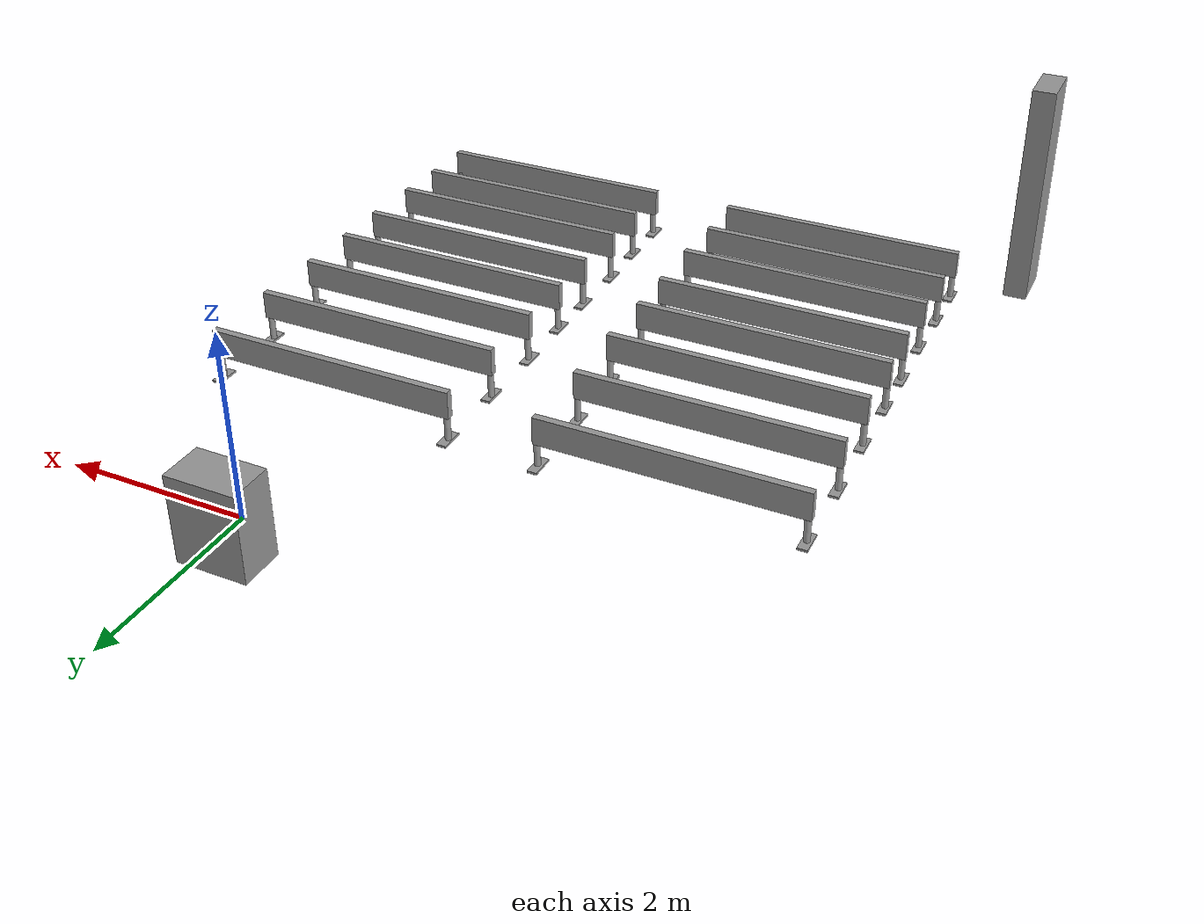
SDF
<?xml version='1.0'?>
<sdf version='1.6'>
  <model name='banchi'>
    <link name='link_3'>
      <pose frame=''>0.19401 0.058881 0.005926 0 -0 0</pose>
      <inertial>
        <mass>1</mass>
        <inertia>
          <ixx>0.166667</ixx>
          <ixy>0</ixy>
          <ixz>0</ixz>
          <iyy>0.166667</iyy>
          <iyz>0</iyz>
          <izz>0.166667</izz>
        </inertia>
        <pose frame=''>0 0 0 0 -0 0</pose>
      </inertial>
      <gravity>1</gravity>
      <self_collide>0</self_collide>
      <kinematic>0</kinematic>
      <enable_wind>0</enable_wind>
      <visual name='visual'>
        <pose frame=''>0 0 0 0 -0 0</pose>
        <geometry>
          <box>
            <size>0.8 0.5 1</size>
          </box>
        </geometry>
        <material>
          <lighting>1</lighting>
          <script>
            <uri>file://media/materials/scripts/gazebo.material</uri>
            <name>Gazebo/Grey</name>
          </script>
          <ambient>0.3 0.3 0.3 1</ambient>
          <diffuse>0.7 0.7 0.7 1</diffuse>
          <specular>0.01 0.01 0.01 1</specular>
          <emissive>0 0 0 1</emissive>
          <shader type='vertex'>
            <normal_map>__default__</normal_map>
          </shader>
        </material>
        <cast_shadows>1</cast_shadows>
        <transparency>0</transparency>
      </visual>
      <collision name='collision'>
        <laser_retro>0</laser_retro>
        <max_contacts>10</max_contacts>
        <pose frame=''>0 0 0 0 -0 0</pose>
        <geometry>
          <box>
            <size>0.8 0.5 1</size>
          </box>
        </geometry>
        <surface>
          <friction>
            <ode>
              <mu>1</mu>
              <mu2>1</mu2>
              <fdir1>0 0 0</fdir1>
              <slip1>0</slip1>
              <slip2>0</slip2>
            </ode>
            <torsional>
              <coefficient>1</coefficient>
              <patch_radius>0</patch_radius>
              <surface_radius>0</surface_radius>
              <use_patch_radius>1</use_patch_radius>
              <ode>
                <slip>0</slip>
              </ode>
            </torsional>
          </friction>
          <bounce>
            <restitution_coefficient>0</restitution_coefficient>
            <threshold>1e+06</threshold>
          </bounce>
          <contact>
            <collide_without_contact>0</collide_without_contact>
            <collide_without_contact_bitmask>1</collide_without_contact_bitmask>
            <collide_bitmask>1</collide_bitmask>
            <ode>
              <soft_cfm>0</soft_cfm>
              <soft_erp>0.2</soft_erp>
              <kp>1e+13</kp>
              <kd>1</kd>
              <max_vel>0.01</max_vel>
              <min_depth>0</min_depth>
            </ode>
            <bullet>
              <split_impulse>1</split_impulse>
              <split_impulse_penetration_threshold>-0.01</split_impulse_penetration_threshold>
              <soft_cfm>0</soft_cfm>
              <soft_erp>0.2</soft_erp>
              <kp>1e+13</kp>
              <kd>1</kd>
            </bullet>
          </contact>
        </surface>
      </collision>
    </link>
    <link name='link_0'>
      <inertial>
        <mass>0.000785881</mass>
        <inertia>
          <ixx>5.11476e-06</ixx>
          <ixy>0</ixy>
          <ixz>0</ixz>
          <iyy>8.37345e-07</iyy>
          <iyz>0</iyz>
          <izz>5.8658e-06</izz>
        </inertia>
        <pose frame=''>0 0 0 0 -0 0</pose>
      </inertial>
      <pose frame=''>2.2428 -2.55708 -0.495327 0 -0 0</pose>
      <visual name='visual'>
        <pose frame=''>0 0 0 0 -0 0</pose>
        <geometry>
          <box>
            <size>0.110122 0.278282 0.025669</size>
          </box>
        </geometry>
        <material>
          <lighting>1</lighting>
          <script>
            <uri>file://media/materials/scripts/gazebo.material</uri>
            <name>Gazebo/Grey</name>
          </script>
        </material>
        <transparency>0</transparency>
        <cast_shadows>1</cast_shadows>
      </visual>
      <collision name='collision'>
        <laser_retro>0</laser_retro>
        <max_contacts>10</max_contacts>
        <pose frame=''>0 0 0 0 -0 0</pose>
        <geometry>
          <box>
            <size>0.110122 0.278282 0.025669</size>
          </box>
        </geometry>
        <surface>
          <friction>
            <ode>
              <mu>1</mu>
              <mu2>1</mu2>
              <fdir1>0 0 0</fdir1>
              <slip1>0</slip1>
              <slip2>0</slip2>
            </ode>
            <torsional>
              <coefficient>1</coefficient>
              <patch_radius>0</patch_radius>
              <surface_radius>0</surface_radius>
              <use_patch_radius>1</use_patch_radius>
              <ode>
                <slip>0</slip>
              </ode>
            </torsional>
          </friction>
          <bounce>
            <restitution_coefficient>0</restitution_coefficient>
            <threshold>1e+06</threshold>
          </bounce>
          <contact>
            <collide_without_contact>0</collide_without_contact>
            <collide_without_contact_bitmask>1</collide_without_contact_bitmask>
            <collide_bitmask>1</collide_bitmask>
            <ode>
              <soft_cfm>0</soft_cfm>
              <soft_erp>0.2</soft_erp>
              <kp>1e+13</kp>
              <kd>1</kd>
              <max_vel>0.01</max_vel>
              <min_depth>0</min_depth>
            </ode>
            <bullet>
              <split_impulse>1</split_impulse>
              <split_impulse_penetration_threshold>-0.01</split_impulse_penetration_threshold>
              <soft_cfm>0</soft_cfm>
              <soft_erp>0.2</soft_erp>
              <kp>1e+13</kp>
              <kd>1</kd>
            </bullet>
          </contact>
        </surface>
      </collision>
    </link>
    <link name='link_0_clone'>
      <inertial>
        <mass>0.000785881</mass>
        <inertia>
          <ixx>5.11476e-06</ixx>
          <ixy>0</ixy>
          <ixz>0</ixz>
          <iyy>8.37345e-07</iyy>
          <iyz>0</iyz>
          <izz>5.8658e-06</izz>
        </inertia>
        <pose frame=''>0 0 0 0 -0 0</pose>
      </inertial>
      <pose frame=''>2.245 -3.48891 -0.495327 0 -0 0</pose>
      <visual name='visual'>
        <pose frame=''>0 0 0 0 -0 0</pose>
        <geometry>
          <box>
            <size>0.110122 0.278282 0.025669</size>
          </box>
        </geometry>
        <material>
          <lighting>1</lighting>
          <script>
            <uri>file://media/materials/scripts/gazebo.material</uri>
            <name>Gazebo/Grey</name>
          </script>
          <shader type='pixel'/>
        </material>
        <transparency>0</transparency>
        <cast_shadows>1</cast_shadows>
      </visual>
      <collision name='collision'>
        <laser_retro>0</laser_retro>
        <max_contacts>10</max_contacts>
        <pose frame=''>0 0 0 0 -0 0</pose>
        <geometry>
          <box>
            <size>0.110122 0.278282 0.025669</size>
          </box>
        </geometry>
        <surface>
          <friction>
            <ode>
              <mu>1</mu>
              <mu2>1</mu2>
              <fdir1>0 0 0</fdir1>
              <slip1>0</slip1>
              <slip2>0</slip2>
            </ode>
            <torsional>
              <coefficient>1</coefficient>
              <patch_radius>0</patch_radius>
              <surface_radius>0</surface_radius>
              <use_patch_radius>1</use_patch_radius>
              <ode>
                <slip>0</slip>
              </ode>
            </torsional>
          </friction>
          <bounce>
            <restitution_coefficient>0</restitution_coefficient>
            <threshold>1e+06</threshold>
          </bounce>
          <contact>
            <collide_without_contact>0</collide_without_contact>
            <collide_without_contact_bitmask>1</collide_without_contact_bitmask>
            <collide_bitmask>1</collide_bitmask>
            <ode>
              <soft_cfm>0</soft_cfm>
              <soft_erp>0.2</soft_erp>
              <kp>1e+13</kp>
              <kd>1</kd>
              <max_vel>0.01</max_vel>
              <min_depth>0</min_depth>
            </ode>
            <bullet>
              <split_impulse>1</split_impulse>
              <split_impulse_penetration_threshold>-0.01</split_impulse_penetration_threshold>
              <soft_cfm>0</soft_cfm>
              <soft_erp>0.2</soft_erp>
              <kp>1e+13</kp>
              <kd>1</kd>
            </bullet>
          </contact>
        </surface>
      </collision>
    </link>
    <link name='link_0_clone_0'>
      <inertial>
        <mass>0.000785881</mass>
        <inertia>
          <ixx>5.11476e-06</ixx>
          <ixy>0</ixy>
          <ixz>0</ixz>
          <iyy>8.37345e-07</iyy>
          <iyz>0</iyz>
          <izz>5.8658e-06</izz>
        </inertia>
        <pose frame=''>0 0 0 0 -0 0</pose>
      </inertial>
      <pose frame=''>2.24403 -4.35243 -0.495327 0 -0 0</pose>
      <visual name='visual'>
        <pose frame=''>0 0 0 0 -0 0</pose>
        <geometry>
          <box>
            <size>0.110122 0.278282 0.025669</size>
          </box>
        </geometry>
        <material>
          <lighting>1</lighting>
          <script>
            <uri>file://media/materials/scripts/gazebo.material</uri>
            <name>Gazebo/Grey</name>
          </script>
          <shader type='pixel'/>
        </material>
        <transparency>0</transparency>
        <cast_shadows>1</cast_shadows>
      </visual>
      <collision name='collision'>
        <laser_retro>0</laser_retro>
        <max_contacts>10</max_contacts>
        <pose frame=''>0 0 0 0 -0 0</pose>
        <geometry>
          <box>
            <size>0.110122 0.278282 0.025669</size>
          </box>
        </geometry>
        <surface>
          <friction>
            <ode>
              <mu>1</mu>
              <mu2>1</mu2>
              <fdir1>0 0 0</fdir1>
              <slip1>0</slip1>
              <slip2>0</slip2>
            </ode>
            <torsional>
              <coefficient>1</coefficient>
              <patch_radius>0</patch_radius>
              <surface_radius>0</surface_radius>
              <use_patch_radius>1</use_patch_radius>
              <ode>
                <slip>0</slip>
              </ode>
            </torsional>
          </friction>
          <bounce>
            <restitution_coefficient>0</restitution_coefficient>
            <threshold>1e+06</threshold>
          </bounce>
          <contact>
            <collide_without_contact>0</collide_without_contact>
            <collide_without_contact_bitmask>1</collide_without_contact_bitmask>
            <collide_bitmask>1</collide_bitmask>
            <ode>
              <soft_cfm>0</soft_cfm>
              <soft_erp>0.2</soft_erp>
              <kp>1e+13</kp>
              <kd>1</kd>
              <max_vel>0.01</max_vel>
              <min_depth>0</min_depth>
            </ode>
            <bullet>
              <split_impulse>1</split_impulse>
              <split_impulse_penetration_threshold>-0.01</split_impulse_penetration_threshold>
              <soft_cfm>0</soft_cfm>
              <soft_erp>0.2</soft_erp>
              <kp>1e+13</kp>
              <kd>1</kd>
            </bullet>
          </contact>
        </surface>
      </collision>
    </link>
    <link name='link_0_clone_1'>
      <inertial>
        <mass>0.000785881</mass>
        <inertia>
          <ixx>5.11476e-06</ixx>
          <ixy>0</ixy>
          <ixz>0</ixz>
          <iyy>8.37345e-07</iyy>
          <iyz>0</iyz>
          <izz>5.8658e-06</izz>
        </inertia>
        <pose frame=''>0 0 0 0 -0 0</pose>
      </inertial>
      <pose frame=''>2.25812 -5.12778 -0.495327 0 -0 0</pose>
      <visual name='visual'>
        <pose frame=''>0 0 0 0 -0 0</pose>
        <geometry>
          <box>
            <size>0.110122 0.278282 0.025669</size>
          </box>
        </geometry>
        <material>
          <lighting>1</lighting>
          <script>
            <uri>file://media/materials/scripts/gazebo.material</uri>
            <name>Gazebo/Grey</name>
          </script>
          <shader type='pixel'/>
        </material>
        <transparency>0</transparency>
        <cast_shadows>1</cast_shadows>
      </visual>
      <collision name='collision'>
        <laser_retro>0</laser_retro>
        <max_contacts>10</max_contacts>
        <pose frame=''>0 0 0 0 -0 0</pose>
        <geometry>
          <box>
            <size>0.110122 0.278282 0.025669</size>
          </box>
        </geometry>
        <surface>
          <friction>
            <ode>
              <mu>1</mu>
              <mu2>1</mu2>
              <fdir1>0 0 0</fdir1>
              <slip1>0</slip1>
              <slip2>0</slip2>
            </ode>
            <torsional>
              <coefficient>1</coefficient>
              <patch_radius>0</patch_radius>
              <surface_radius>0</surface_radius>
              <use_patch_radius>1</use_patch_radius>
              <ode>
                <slip>0</slip>
              </ode>
            </torsional>
          </friction>
          <bounce>
            <restitution_coefficient>0</restitution_coefficient>
            <threshold>1e+06</threshold>
          </bounce>
          <contact>
            <collide_without_contact>0</collide_without_contact>
            <collide_without_contact_bitmask>1</collide_without_contact_bitmask>
            <collide_bitmask>1</collide_bitmask>
            <ode>
              <soft_cfm>0</soft_cfm>
              <soft_erp>0.2</soft_erp>
              <kp>1e+13</kp>
              <kd>1</kd>
              <max_vel>0.01</max_vel>
              <min_depth>0</min_depth>
            </ode>
            <bullet>
              <split_impulse>1</split_impulse>
              <split_impulse_penetration_threshold>-0.01</split_impulse_penetration_threshold>
              <soft_cfm>0</soft_cfm>
              <soft_erp>0.2</soft_erp>
              <kp>1e+13</kp>
              <kd>1</kd>
            </bullet>
          </contact>
        </surface>
      </collision>
    </link>
    <link name='link_0_clone_10'>
      <inertial>
        <mass>0.000785881</mass>
        <inertia>
          <ixx>5.11476e-06</ixx>
          <ixy>0</ixy>
          <ixz>0</ixz>
          <iyy>8.37345e-07</iyy>
          <iyz>0</iyz>
          <izz>5.8658e-06</izz>
        </inertia>
        <pose frame=''>0 0 0 0 -0 0</pose>
      </inertial>
      <pose frame=''>-0.67038 -5.15029 -0.495327 0 -0 0</pose>
      <visual name='visual'>
        <pose frame=''>0 0 0 0 -0 0</pose>
        <geometry>
          <box>
            <size>0.110122 0.278282 0.025669</size>
          </box>
        </geometry>
        <material>
          <lighting>1</lighting>
          <script>
            <uri>file://media/materials/scripts/gazebo.material</uri>
            <name>Gazebo/Grey</name>
          </script>
          <shader type='pixel'/>
        </material>
        <transparency>0</transparency>
        <cast_shadows>1</cast_shadows>
      </visual>
      <collision name='collision'>
        <laser_retro>0</laser_retro>
        <max_contacts>10</max_contacts>
        <pose frame=''>0 0 0 0 -0 0</pose>
        <geometry>
          <box>
            <size>0.110122 0.278282 0.025669</size>
          </box>
        </geometry>
        <surface>
          <friction>
            <ode>
              <mu>1</mu>
              <mu2>1</mu2>
              <fdir1>0 0 0</fdir1>
              <slip1>0</slip1>
              <slip2>0</slip2>
            </ode>
            <torsional>
              <coefficient>1</coefficient>
              <patch_radius>0</patch_radius>
              <surface_radius>0</surface_radius>
              <use_patch_radius>1</use_patch_radius>
              <ode>
                <slip>0</slip>
              </ode>
            </torsional>
          </friction>
          <bounce>
            <restitution_coefficient>0</restitution_coefficient>
            <threshold>1e+06</threshold>
          </bounce>
          <contact>
            <collide_without_contact>0</collide_without_contact>
            <collide_without_contact_bitmask>1</collide_without_contact_bitmask>
            <collide_bitmask>1</collide_bitmask>
            <ode>
              <soft_cfm>0</soft_cfm>
              <soft_erp>0.2</soft_erp>
              <kp>1e+13</kp>
              <kd>1</kd>
              <max_vel>0.01</max_vel>
              <min_depth>0</min_depth>
            </ode>
            <bullet>
              <split_impulse>1</split_impulse>
              <split_impulse_penetration_threshold>-0.01</split_impulse_penetration_threshold>
              <soft_cfm>0</soft_cfm>
              <soft_erp>0.2</soft_erp>
              <kp>1e+13</kp>
              <kd>1</kd>
            </bullet>
          </contact>
        </surface>
      </collision>
    </link>
    <link name='link_0_clone_11'>
      <inertial>
        <mass>0.000785881</mass>
        <inertia>
          <ixx>5.11476e-06</ixx>
          <ixy>0</ixy>
          <ixz>0</ixz>
          <iyy>8.37345e-07</iyy>
          <iyz>0</iyz>
          <izz>5.8658e-06</izz>
        </inertia>
        <pose frame=''>0 0 0 0 -0 0</pose>
      </inertial>
      <pose frame=''>-0.686084 -4.37283 -0.495327 0 -0 0</pose>
      <visual name='visual'>
        <pose frame=''>0 0 0 0 -0 0</pose>
        <geometry>
          <box>
            <size>0.110122 0.278282 0.025669</size>
          </box>
        </geometry>
        <material>
          <lighting>1</lighting>
          <script>
            <uri>file://media/materials/scripts/gazebo.material</uri>
            <name>Gazebo/Grey</name>
          </script>
          <shader type='pixel'/>
        </material>
        <transparency>0</transparency>
        <cast_shadows>1</cast_shadows>
      </visual>
      <collision name='collision'>
        <laser_retro>0</laser_retro>
        <max_contacts>10</max_contacts>
        <pose frame=''>0 0 0 0 -0 0</pose>
        <geometry>
          <box>
            <size>0.110122 0.278282 0.025669</size>
          </box>
        </geometry>
        <surface>
          <friction>
            <ode>
              <mu>1</mu>
              <mu2>1</mu2>
              <fdir1>0 0 0</fdir1>
              <slip1>0</slip1>
              <slip2>0</slip2>
            </ode>
            <torsional>
              <coefficient>1</coefficient>
              <patch_radius>0</patch_radius>
              <surface_radius>0</surface_radius>
              <use_patch_radius>1</use_patch_radius>
              <ode>
                <slip>0</slip>
              </ode>
            </torsional>
          </friction>
          <bounce>
            <restitution_coefficient>0</restitution_coefficient>
            <threshold>1e+06</threshold>
          </bounce>
          <contact>
            <collide_without_contact>0</collide_without_contact>
            <collide_without_contact_bitmask>1</collide_without_contact_bitmask>
            <collide_bitmask>1</collide_bitmask>
            <ode>
              <soft_cfm>0</soft_cfm>
              <soft_erp>0.2</soft_erp>
              <kp>1e+13</kp>
              <kd>1</kd>
              <max_vel>0.01</max_vel>
              <min_depth>0</min_depth>
            </ode>
            <bullet>
              <split_impulse>1</split_impulse>
              <split_impulse_penetration_threshold>-0.01</split_impulse_penetration_threshold>
              <soft_cfm>0</soft_cfm>
              <soft_erp>0.2</soft_erp>
              <kp>1e+13</kp>
              <kd>1</kd>
            </bullet>
          </contact>
        </surface>
      </collision>
    </link>
    <link name='link_0_clone_11_clone'>
      <inertial>
        <mass>0.000785881</mass>
        <inertia>
          <ixx>5.11476e-06</ixx>
          <ixy>0</ixy>
          <ixz>0</ixz>
          <iyy>8.37345e-07</iyy>
          <iyz>0</iyz>
          <izz>5.8658e-06</izz>
        </inertia>
        <pose frame=''>0 0 0 0 -0 0</pose>
      </inertial>
      <pose frame=''>-0.669518 -3.50617 -0.495327 0 -0 0</pose>
      <visual name='visual'>
        <pose frame=''>0 0 0 0 -0 0</pose>
        <geometry>
          <box>
            <size>0.110122 0.278282 0.025669</size>
          </box>
        </geometry>
        <material>
          <lighting>1</lighting>
          <script>
            <uri>file://media/materials/scripts/gazebo.material</uri>
            <name>Gazebo/Grey</name>
          </script>
          <shader type='pixel'/>
        </material>
        <transparency>0</transparency>
        <cast_shadows>1</cast_shadows>
      </visual>
      <collision name='collision'>
        <laser_retro>0</laser_retro>
        <max_contacts>10</max_contacts>
        <pose frame=''>0 0 0 0 -0 0</pose>
        <geometry>
          <box>
            <size>0.110122 0.278282 0.025669</size>
          </box>
        </geometry>
        <surface>
          <friction>
            <ode>
              <mu>1</mu>
              <mu2>1</mu2>
              <fdir1>0 0 0</fdir1>
              <slip1>0</slip1>
              <slip2>0</slip2>
            </ode>
            <torsional>
              <coefficient>1</coefficient>
              <patch_radius>0</patch_radius>
              <surface_radius>0</surface_radius>
              <use_patch_radius>1</use_patch_radius>
              <ode>
                <slip>0</slip>
              </ode>
            </torsional>
          </friction>
          <bounce>
            <restitution_coefficient>0</restitution_coefficient>
            <threshold>1e+06</threshold>
          </bounce>
          <contact>
            <collide_without_contact>0</collide_without_contact>
            <collide_without_contact_bitmask>1</collide_without_contact_bitmask>
            <collide_bitmask>1</collide_bitmask>
            <ode>
              <soft_cfm>0</soft_cfm>
              <soft_erp>0.2</soft_erp>
              <kp>1e+13</kp>
              <kd>1</kd>
              <max_vel>0.01</max_vel>
              <min_depth>0</min_depth>
            </ode>
            <bullet>
              <split_impulse>1</split_impulse>
              <split_impulse_penetration_threshold>-0.01</split_impulse_penetration_threshold>
              <soft_cfm>0</soft_cfm>
              <soft_erp>0.2</soft_erp>
              <kp>1e+13</kp>
              <kd>1</kd>
            </bullet>
          </contact>
        </surface>
      </collision>
    </link>
    <link name='link_0_clone_13'>
      <inertial>
        <mass>0.000785881</mass>
        <inertia>
          <ixx>5.11476e-06</ixx>
          <ixy>0</ixy>
          <ixz>0</ixz>
          <iyy>8.37345e-07</iyy>
          <iyz>0</iyz>
          <izz>5.8658e-06</izz>
        </inertia>
        <pose frame=''>0 0 0 0 -0 0</pose>
      </inertial>
      <pose frame=''>-0.6754 -2.55339 -0.495327 0 -0 0</pose>
      <visual name='visual'>
        <pose frame=''>0 0 0 0 -0 0</pose>
        <geometry>
          <box>
            <size>0.110122 0.278282 0.025669</size>
          </box>
        </geometry>
        <material>
          <lighting>1</lighting>
          <script>
            <uri>file://media/materials/scripts/gazebo.material</uri>
            <name>Gazebo/Grey</name>
          </script>
          <shader type='pixel'/>
        </material>
        <transparency>0</transparency>
        <cast_shadows>1</cast_shadows>
      </visual>
      <collision name='collision'>
        <laser_retro>0</laser_retro>
        <max_contacts>10</max_contacts>
        <pose frame=''>0 0 0 0 -0 0</pose>
        <geometry>
          <box>
            <size>0.110122 0.278282 0.025669</size>
          </box>
        </geometry>
        <surface>
          <friction>
            <ode>
              <mu>1</mu>
              <mu2>1</mu2>
              <fdir1>0 0 0</fdir1>
              <slip1>0</slip1>
              <slip2>0</slip2>
            </ode>
            <torsional>
              <coefficient>1</coefficient>
              <patch_radius>0</patch_radius>
              <surface_radius>0</surface_radius>
              <use_patch_radius>1</use_patch_radius>
              <ode>
                <slip>0</slip>
              </ode>
            </torsional>
          </friction>
          <bounce>
            <restitution_coefficient>0</restitution_coefficient>
            <threshold>1e+06</threshold>
          </bounce>
          <contact>
            <collide_without_contact>0</collide_without_contact>
            <collide_without_contact_bitmask>1</collide_without_contact_bitmask>
            <collide_bitmask>1</collide_bitmask>
            <ode>
              <soft_cfm>0</soft_cfm>
              <soft_erp>0.2</soft_erp>
              <kp>1e+13</kp>
              <kd>1</kd>
              <max_vel>0.01</max_vel>
              <min_depth>0</min_depth>
            </ode>
            <bullet>
              <split_impulse>1</split_impulse>
              <split_impulse_penetration_threshold>-0.01</split_impulse_penetration_threshold>
              <soft_cfm>0</soft_cfm>
              <soft_erp>0.2</soft_erp>
              <kp>1e+13</kp>
              <kd>1</kd>
            </bullet>
          </contact>
        </surface>
      </collision>
    </link>
    <link name='link_0_clone_14'>
      <inertial>
        <mass>0.000785881</mass>
        <inertia>
          <ixx>5.11476e-06</ixx>
          <ixy>0</ixy>
          <ixz>0</ixz>
          <iyy>8.37345e-07</iyy>
          <iyz>0</iyz>
          <izz>5.8658e-06</izz>
        </inertia>
        <pose frame=''>0 0 0 0 -0 0</pose>
      </inertial>
      <pose frame=''>-1.75959 -2.54035 -0.495327 0 -0 0</pose>
      <visual name='visual'>
        <pose frame=''>0 0 0 0 -0 0</pose>
        <geometry>
          <box>
            <size>0.110122 0.278282 0.025669</size>
          </box>
        </geometry>
        <material>
          <lighting>1</lighting>
          <script>
            <uri>file://media/materials/scripts/gazebo.material</uri>
            <name>Gazebo/Grey</name>
          </script>
          <shader type='pixel'/>
        </material>
        <transparency>0</transparency>
        <cast_shadows>1</cast_shadows>
      </visual>
      <collision name='collision'>
        <laser_retro>0</laser_retro>
        <max_contacts>10</max_contacts>
        <pose frame=''>0 0 0 0 -0 0</pose>
        <geometry>
          <box>
            <size>0.110122 0.278282 0.025669</size>
          </box>
        </geometry>
        <surface>
          <friction>
            <ode>
              <mu>1</mu>
              <mu2>1</mu2>
              <fdir1>0 0 0</fdir1>
              <slip1>0</slip1>
              <slip2>0</slip2>
            </ode>
            <torsional>
              <coefficient>1</coefficient>
              <patch_radius>0</patch_radius>
              <surface_radius>0</surface_radius>
              <use_patch_radius>1</use_patch_radius>
              <ode>
                <slip>0</slip>
              </ode>
            </torsional>
          </friction>
          <bounce>
            <restitution_coefficient>0</restitution_coefficient>
            <threshold>1e+06</threshold>
          </bounce>
          <contact>
            <collide_without_contact>0</collide_without_contact>
            <collide_without_contact_bitmask>1</collide_without_contact_bitmask>
            <collide_bitmask>1</collide_bitmask>
            <ode>
              <soft_cfm>0</soft_cfm>
              <soft_erp>0.2</soft_erp>
              <kp>1e+13</kp>
              <kd>1</kd>
              <max_vel>0.01</max_vel>
              <min_depth>0</min_depth>
            </ode>
            <bullet>
              <split_impulse>1</split_impulse>
              <split_impulse_penetration_threshold>-0.01</split_impulse_penetration_threshold>
              <soft_cfm>0</soft_cfm>
              <soft_erp>0.2</soft_erp>
              <kp>1e+13</kp>
              <kd>1</kd>
            </bullet>
          </contact>
        </surface>
      </collision>
    </link>
    <link name='link_0_clone_15'>
      <inertial>
        <mass>0.000785881</mass>
        <inertia>
          <ixx>5.11476e-06</ixx>
          <ixy>0</ixy>
          <ixz>0</ixz>
          <iyy>8.37345e-07</iyy>
          <iyz>0</iyz>
          <izz>5.8658e-06</izz>
        </inertia>
        <pose frame=''>0 0 0 0 -0 0</pose>
      </inertial>
      <pose frame=''>-1.75172 -3.47821 -0.495327 0 -0 0</pose>
      <visual name='visual'>
        <pose frame=''>0 0 0 0 -0 0</pose>
        <geometry>
          <box>
            <size>0.110122 0.278282 0.025669</size>
          </box>
        </geometry>
        <material>
          <lighting>1</lighting>
          <script>
            <uri>file://media/materials/scripts/gazebo.material</uri>
            <name>Gazebo/Grey</name>
          </script>
          <shader type='pixel'/>
        </material>
        <transparency>0</transparency>
        <cast_shadows>1</cast_shadows>
      </visual>
      <collision name='collision'>
        <laser_retro>0</laser_retro>
        <max_contacts>10</max_contacts>
        <pose frame=''>0 0 0 0 -0 0</pose>
        <geometry>
          <box>
            <size>0.110122 0.278282 0.025669</size>
          </box>
        </geometry>
        <surface>
          <friction>
            <ode>
              <mu>1</mu>
              <mu2>1</mu2>
              <fdir1>0 0 0</fdir1>
              <slip1>0</slip1>
              <slip2>0</slip2>
            </ode>
            <torsional>
              <coefficient>1</coefficient>
              <patch_radius>0</patch_radius>
              <surface_radius>0</surface_radius>
              <use_patch_radius>1</use_patch_radius>
              <ode>
                <slip>0</slip>
              </ode>
            </torsional>
          </friction>
          <bounce>
            <restitution_coefficient>0</restitution_coefficient>
            <threshold>1e+06</threshold>
          </bounce>
          <contact>
            <collide_without_contact>0</collide_without_contact>
            <collide_without_contact_bitmask>1</collide_without_contact_bitmask>
            <collide_bitmask>1</collide_bitmask>
            <ode>
              <soft_cfm>0</soft_cfm>
              <soft_erp>0.2</soft_erp>
              <kp>1e+13</kp>
              <kd>1</kd>
              <max_vel>0.01</max_vel>
              <min_depth>0</min_depth>
            </ode>
            <bullet>
              <split_impulse>1</split_impulse>
              <split_impulse_penetration_threshold>-0.01</split_impulse_penetration_threshold>
              <soft_cfm>0</soft_cfm>
              <soft_erp>0.2</soft_erp>
              <kp>1e+13</kp>
              <kd>1</kd>
            </bullet>
          </contact>
        </surface>
      </collision>
    </link>
    <link name='link_0_clone_16'>
      <inertial>
        <mass>0.000785881</mass>
        <inertia>
          <ixx>5.11476e-06</ixx>
          <ixy>0</ixy>
          <ixz>0</ixz>
          <iyy>8.37345e-07</iyy>
          <iyz>0</iyz>
          <izz>5.8658e-06</izz>
        </inertia>
        <pose frame=''>0 0 0 0 -0 0</pose>
      </inertial>
      <pose frame=''>-1.72573 -4.34491 -0.495327 0 -0 0</pose>
      <visual name='visual'>
        <pose frame=''>0 0 0 0 -0 0</pose>
        <geometry>
          <box>
            <size>0.110122 0.278282 0.025669</size>
          </box>
        </geometry>
        <material>
          <lighting>1</lighting>
          <script>
            <uri>file://media/materials/scripts/gazebo.material</uri>
            <name>Gazebo/Grey</name>
          </script>
          <shader type='pixel'/>
        </material>
        <transparency>0</transparency>
        <cast_shadows>1</cast_shadows>
      </visual>
      <collision name='collision'>
        <laser_retro>0</laser_retro>
        <max_contacts>10</max_contacts>
        <pose frame=''>0 0 0 0 -0 0</pose>
        <geometry>
          <box>
            <size>0.110122 0.278282 0.025669</size>
          </box>
        </geometry>
        <surface>
          <friction>
            <ode>
              <mu>1</mu>
              <mu2>1</mu2>
              <fdir1>0 0 0</fdir1>
              <slip1>0</slip1>
              <slip2>0</slip2>
            </ode>
            <torsional>
              <coefficient>1</coefficient>
              <patch_radius>0</patch_radius>
              <surface_radius>0</surface_radius>
              <use_patch_radius>1</use_patch_radius>
              <ode>
                <slip>0</slip>
              </ode>
            </torsional>
          </friction>
          <bounce>
            <restitution_coefficient>0</restitution_coefficient>
            <threshold>1e+06</threshold>
          </bounce>
          <contact>
            <collide_without_contact>0</collide_without_contact>
            <collide_without_contact_bitmask>1</collide_without_contact_bitmask>
            <collide_bitmask>1</collide_bitmask>
            <ode>
              <soft_cfm>0</soft_cfm>
              <soft_erp>0.2</soft_erp>
              <kp>1e+13</kp>
              <kd>1</kd>
              <max_vel>0.01</max_vel>
              <min_depth>0</min_depth>
            </ode>
            <bullet>
              <split_impulse>1</split_impulse>
              <split_impulse_penetration_threshold>-0.01</split_impulse_penetration_threshold>
              <soft_cfm>0</soft_cfm>
              <soft_erp>0.2</soft_erp>
              <kp>1e+13</kp>
              <kd>1</kd>
            </bullet>
          </contact>
        </surface>
      </collision>
    </link>
    <link name='link_0_clone_17'>
      <inertial>
        <mass>0.000785881</mass>
        <inertia>
          <ixx>5.11476e-06</ixx>
          <ixy>0</ixy>
          <ixz>0</ixz>
          <iyy>8.37345e-07</iyy>
          <iyz>0</iyz>
          <izz>5.8658e-06</izz>
        </inertia>
        <pose frame=''>0 0 0 0 -0 0</pose>
      </inertial>
      <pose frame=''>-1.74948 -5.13394 -0.495327 0 -0 0</pose>
      <visual name='visual'>
        <pose frame=''>0 0 0 0 -0 0</pose>
        <geometry>
          <box>
            <size>0.110122 0.278282 0.025669</size>
          </box>
        </geometry>
        <material>
          <lighting>1</lighting>
          <script>
            <uri>file://media/materials/scripts/gazebo.material</uri>
            <name>Gazebo/Grey</name>
          </script>
          <shader type='pixel'/>
        </material>
        <transparency>0</transparency>
        <cast_shadows>1</cast_shadows>
      </visual>
      <collision name='collision'>
        <laser_retro>0</laser_retro>
        <max_contacts>10</max_contacts>
        <pose frame=''>0 0 0 0 -0 0</pose>
        <geometry>
          <box>
            <size>0.110122 0.278282 0.025669</size>
          </box>
        </geometry>
        <surface>
          <friction>
            <ode>
              <mu>1</mu>
              <mu2>1</mu2>
              <fdir1>0 0 0</fdir1>
              <slip1>0</slip1>
              <slip2>0</slip2>
            </ode>
            <torsional>
              <coefficient>1</coefficient>
              <patch_radius>0</patch_radius>
              <surface_radius>0</surface_radius>
              <use_patch_radius>1</use_patch_radius>
              <ode>
                <slip>0</slip>
              </ode>
            </torsional>
          </friction>
          <bounce>
            <restitution_coefficient>0</restitution_coefficient>
            <threshold>1e+06</threshold>
          </bounce>
          <contact>
            <collide_without_contact>0</collide_without_contact>
            <collide_without_contact_bitmask>1</collide_without_contact_bitmask>
            <collide_bitmask>1</collide_bitmask>
            <ode>
              <soft_cfm>0</soft_cfm>
              <soft_erp>0.2</soft_erp>
              <kp>1e+13</kp>
              <kd>1</kd>
              <max_vel>0.01</max_vel>
              <min_depth>0</min_depth>
            </ode>
            <bullet>
              <split_impulse>1</split_impulse>
              <split_impulse_penetration_threshold>-0.01</split_impulse_penetration_threshold>
              <soft_cfm>0</soft_cfm>
              <soft_erp>0.2</soft_erp>
              <kp>1e+13</kp>
              <kd>1</kd>
            </bullet>
          </contact>
        </surface>
      </collision>
    </link>
    <link name='link_0_clone_18'>
      <inertial>
        <mass>0.000785881</mass>
        <inertia>
          <ixx>5.11476e-06</ixx>
          <ixy>0</ixy>
          <ixz>0</ixz>
          <iyy>8.37345e-07</iyy>
          <iyz>0</iyz>
          <izz>5.8658e-06</izz>
        </inertia>
        <pose frame=''>0 0 0 0 -0 0</pose>
      </inertial>
      <pose frame=''>-1.73682 -5.78102 -0.495327 0 -0 0</pose>
      <visual name='visual'>
        <pose frame=''>0 0 0 0 -0 0</pose>
        <geometry>
          <box>
            <size>0.110122 0.278282 0.025669</size>
          </box>
        </geometry>
        <material>
          <lighting>1</lighting>
          <script>
            <uri>file://media/materials/scripts/gazebo.material</uri>
            <name>Gazebo/Grey</name>
          </script>
          <shader type='pixel'/>
        </material>
        <transparency>0</transparency>
        <cast_shadows>1</cast_shadows>
      </visual>
      <collision name='collision'>
        <laser_retro>0</laser_retro>
        <max_contacts>10</max_contacts>
        <pose frame=''>0 0 0 0 -0 0</pose>
        <geometry>
          <box>
            <size>0.110122 0.278282 0.025669</size>
          </box>
        </geometry>
        <surface>
          <friction>
            <ode>
              <mu>1</mu>
              <mu2>1</mu2>
              <fdir1>0 0 0</fdir1>
              <slip1>0</slip1>
              <slip2>0</slip2>
            </ode>
            <torsional>
              <coefficient>1</coefficient>
              <patch_radius>0</patch_radius>
              <surface_radius>0</surface_radius>
              <use_patch_radius>1</use_patch_radius>
              <ode>
                <slip>0</slip>
              </ode>
            </torsional>
          </friction>
          <bounce>
            <restitution_coefficient>0</restitution_coefficient>
            <threshold>1e+06</threshold>
          </bounce>
          <contact>
            <collide_without_contact>0</collide_without_contact>
            <collide_without_contact_bitmask>1</collide_without_contact_bitmask>
            <collide_bitmask>1</collide_bitmask>
            <ode>
              <soft_cfm>0</soft_cfm>
              <soft_erp>0.2</soft_erp>
              <kp>1e+13</kp>
              <kd>1</kd>
              <max_vel>0.01</max_vel>
              <min_depth>0</min_depth>
            </ode>
            <bullet>
              <split_impulse>1</split_impulse>
              <split_impulse_penetration_threshold>-0.01</split_impulse_penetration_threshold>
              <soft_cfm>0</soft_cfm>
              <soft_erp>0.2</soft_erp>
              <kp>1e+13</kp>
              <kd>1</kd>
            </bullet>
          </contact>
        </surface>
      </collision>
    </link>
    <link name='link_0_clone_19'>
      <inertial>
        <mass>0.000785881</mass>
        <inertia>
          <ixx>5.11476e-06</ixx>
          <ixy>0</ixy>
          <ixz>0</ixz>
          <iyy>8.37345e-07</iyy>
          <iyz>0</iyz>
          <izz>5.8658e-06</izz>
        </inertia>
        <pose frame=''>0 0 0 0 -0 0</pose>
      </inertial>
      <pose frame=''>-1.74049 -6.54069 -0.495327 0 -0 0</pose>
      <visual name='visual'>
        <pose frame=''>0 0 0 0 -0 0</pose>
        <geometry>
          <box>
            <size>0.110122 0.278282 0.025669</size>
          </box>
        </geometry>
        <material>
          <lighting>1</lighting>
          <script>
            <uri>file://media/materials/scripts/gazebo.material</uri>
            <name>Gazebo/Grey</name>
          </script>
          <shader type='pixel'/>
        </material>
        <transparency>0</transparency>
        <cast_shadows>1</cast_shadows>
      </visual>
      <collision name='collision'>
        <laser_retro>0</laser_retro>
        <max_contacts>10</max_contacts>
        <pose frame=''>0 0 0 0 -0 0</pose>
        <geometry>
          <box>
            <size>0.110122 0.278282 0.025669</size>
          </box>
        </geometry>
        <surface>
          <friction>
            <ode>
              <mu>1</mu>
              <mu2>1</mu2>
              <fdir1>0 0 0</fdir1>
              <slip1>0</slip1>
              <slip2>0</slip2>
            </ode>
            <torsional>
              <coefficient>1</coefficient>
              <patch_radius>0</patch_radius>
              <surface_radius>0</surface_radius>
              <use_patch_radius>1</use_patch_radius>
              <ode>
                <slip>0</slip>
              </ode>
            </torsional>
          </friction>
          <bounce>
            <restitution_coefficient>0</restitution_coefficient>
            <threshold>1e+06</threshold>
          </bounce>
          <contact>
            <collide_without_contact>0</collide_without_contact>
            <collide_without_contact_bitmask>1</collide_without_contact_bitmask>
            <collide_bitmask>1</collide_bitmask>
            <ode>
              <soft_cfm>0</soft_cfm>
              <soft_erp>0.2</soft_erp>
              <kp>1e+13</kp>
              <kd>1</kd>
              <max_vel>0.01</max_vel>
              <min_depth>0</min_depth>
            </ode>
            <bullet>
              <split_impulse>1</split_impulse>
              <split_impulse_penetration_threshold>-0.01</split_impulse_penetration_threshold>
              <soft_cfm>0</soft_cfm>
              <soft_erp>0.2</soft_erp>
              <kp>1e+13</kp>
              <kd>1</kd>
            </bullet>
          </contact>
        </surface>
      </collision>
    </link>
    <link name='link_0_clone_2'>
      <inertial>
        <mass>0.000785881</mass>
        <inertia>
          <ixx>5.11476e-06</ixx>
          <ixy>0</ixy>
          <ixz>0</ixz>
          <iyy>8.37345e-07</iyy>
          <iyz>0</iyz>
          <izz>5.8658e-06</izz>
        </inertia>
        <pose frame=''>0 0 0 0 -0 0</pose>
      </inertial>
      <pose frame=''>2.25946 -5.79798 -0.495327 0 -0 0</pose>
      <visual name='visual'>
        <pose frame=''>0 0 0 0 -0 0</pose>
        <geometry>
          <box>
            <size>0.110122 0.278282 0.025669</size>
          </box>
        </geometry>
        <material>
          <lighting>1</lighting>
          <script>
            <uri>file://media/materials/scripts/gazebo.material</uri>
            <name>Gazebo/Grey</name>
          </script>
          <shader type='pixel'/>
        </material>
        <transparency>0</transparency>
        <cast_shadows>1</cast_shadows>
      </visual>
      <collision name='collision'>
        <laser_retro>0</laser_retro>
        <max_contacts>10</max_contacts>
        <pose frame=''>0 0 0 0 -0 0</pose>
        <geometry>
          <box>
            <size>0.110122 0.278282 0.025669</size>
          </box>
        </geometry>
        <surface>
          <friction>
            <ode>
              <mu>1</mu>
              <mu2>1</mu2>
              <fdir1>0 0 0</fdir1>
              <slip1>0</slip1>
              <slip2>0</slip2>
            </ode>
            <torsional>
              <coefficient>1</coefficient>
              <patch_radius>0</patch_radius>
              <surface_radius>0</surface_radius>
              <use_patch_radius>1</use_patch_radius>
              <ode>
                <slip>0</slip>
              </ode>
            </torsional>
          </friction>
          <bounce>
            <restitution_coefficient>0</restitution_coefficient>
            <threshold>1e+06</threshold>
          </bounce>
          <contact>
            <collide_without_contact>0</collide_without_contact>
            <collide_without_contact_bitmask>1</collide_without_contact_bitmask>
            <collide_bitmask>1</collide_bitmask>
            <ode>
              <soft_cfm>0</soft_cfm>
              <soft_erp>0.2</soft_erp>
              <kp>1e+13</kp>
              <kd>1</kd>
              <max_vel>0.01</max_vel>
              <min_depth>0</min_depth>
            </ode>
            <bullet>
              <split_impulse>1</split_impulse>
              <split_impulse_penetration_threshold>-0.01</split_impulse_penetration_threshold>
              <soft_cfm>0</soft_cfm>
              <soft_erp>0.2</soft_erp>
              <kp>1e+13</kp>
              <kd>1</kd>
            </bullet>
          </contact>
        </surface>
      </collision>
    </link>
    <link name='link_0_clone_20'>
      <inertial>
        <mass>0.000785881</mass>
        <inertia>
          <ixx>5.11476e-06</ixx>
          <ixy>0</ixy>
          <ixz>0</ixz>
          <iyy>8.37345e-07</iyy>
          <iyz>0</iyz>
          <izz>5.8658e-06</izz>
        </inertia>
        <pose frame=''>0 0 0 0 -0 0</pose>
      </inertial>
      <pose frame=''>-1.75164 -7.22714 -0.495327 0 -0 0</pose>
      <visual name='visual'>
        <pose frame=''>0 0 0 0 -0 0</pose>
        <geometry>
          <box>
            <size>0.110122 0.278282 0.025669</size>
          </box>
        </geometry>
        <material>
          <lighting>1</lighting>
          <script>
            <uri>file://media/materials/scripts/gazebo.material</uri>
            <name>Gazebo/Grey</name>
          </script>
          <shader type='pixel'/>
        </material>
        <transparency>0</transparency>
        <cast_shadows>1</cast_shadows>
      </visual>
      <collision name='collision'>
        <laser_retro>0</laser_retro>
        <max_contacts>10</max_contacts>
        <pose frame=''>0 0 0 0 -0 0</pose>
        <geometry>
          <box>
            <size>0.110122 0.278282 0.025669</size>
          </box>
        </geometry>
        <surface>
          <friction>
            <ode>
              <mu>1</mu>
              <mu2>1</mu2>
              <fdir1>0 0 0</fdir1>
              <slip1>0</slip1>
              <slip2>0</slip2>
            </ode>
            <torsional>
              <coefficient>1</coefficient>
              <patch_radius>0</patch_radius>
              <surface_radius>0</surface_radius>
              <use_patch_radius>1</use_patch_radius>
              <ode>
                <slip>0</slip>
              </ode>
            </torsional>
          </friction>
          <bounce>
            <restitution_coefficient>0</restitution_coefficient>
            <threshold>1e+06</threshold>
          </bounce>
          <contact>
            <collide_without_contact>0</collide_without_contact>
            <collide_without_contact_bitmask>1</collide_without_contact_bitmask>
            <collide_bitmask>1</collide_bitmask>
            <ode>
              <soft_cfm>0</soft_cfm>
              <soft_erp>0.2</soft_erp>
              <kp>1e+13</kp>
              <kd>1</kd>
              <max_vel>0.01</max_vel>
              <min_depth>0</min_depth>
            </ode>
            <bullet>
              <split_impulse>1</split_impulse>
              <split_impulse_penetration_threshold>-0.01</split_impulse_penetration_threshold>
              <soft_cfm>0</soft_cfm>
              <soft_erp>0.2</soft_erp>
              <kp>1e+13</kp>
              <kd>1</kd>
            </bullet>
          </contact>
        </surface>
      </collision>
    </link>
    <link name='link_0_clone_21'>
      <inertial>
        <mass>0.000785881</mass>
        <inertia>
          <ixx>5.11476e-06</ixx>
          <ixy>0</ixy>
          <ixz>0</ixz>
          <iyy>8.37345e-07</iyy>
          <iyz>0</iyz>
          <izz>5.8658e-06</izz>
        </inertia>
        <pose frame=''>0 0 0 0 -0 0</pose>
      </inertial>
      <pose frame=''>-1.73677 -7.90508 -0.495327 0 -0 0</pose>
      <visual name='visual'>
        <pose frame=''>0 0 0 0 -0 0</pose>
        <geometry>
          <box>
            <size>0.110122 0.278282 0.025669</size>
          </box>
        </geometry>
        <material>
          <lighting>1</lighting>
          <script>
            <uri>file://media/materials/scripts/gazebo.material</uri>
            <name>Gazebo/Grey</name>
          </script>
          <shader type='pixel'/>
        </material>
        <transparency>0</transparency>
        <cast_shadows>1</cast_shadows>
      </visual>
      <collision name='collision'>
        <laser_retro>0</laser_retro>
        <max_contacts>10</max_contacts>
        <pose frame=''>0 0 0 0 -0 0</pose>
        <geometry>
          <box>
            <size>0.110122 0.278282 0.025669</size>
          </box>
        </geometry>
        <surface>
          <friction>
            <ode>
              <mu>1</mu>
              <mu2>1</mu2>
              <fdir1>0 0 0</fdir1>
              <slip1>0</slip1>
              <slip2>0</slip2>
            </ode>
            <torsional>
              <coefficient>1</coefficient>
              <patch_radius>0</patch_radius>
              <surface_radius>0</surface_radius>
              <use_patch_radius>1</use_patch_radius>
              <ode>
                <slip>0</slip>
              </ode>
            </torsional>
          </friction>
          <bounce>
            <restitution_coefficient>0</restitution_coefficient>
            <threshold>1e+06</threshold>
          </bounce>
          <contact>
            <collide_without_contact>0</collide_without_contact>
            <collide_without_contact_bitmask>1</collide_without_contact_bitmask>
            <collide_bitmask>1</collide_bitmask>
            <ode>
              <soft_cfm>0</soft_cfm>
              <soft_erp>0.2</soft_erp>
              <kp>1e+13</kp>
              <kd>1</kd>
              <max_vel>0.01</max_vel>
              <min_depth>0</min_depth>
            </ode>
            <bullet>
              <split_impulse>1</split_impulse>
              <split_impulse_penetration_threshold>-0.01</split_impulse_penetration_threshold>
              <soft_cfm>0</soft_cfm>
              <soft_erp>0.2</soft_erp>
              <kp>1e+13</kp>
              <kd>1</kd>
            </bullet>
          </contact>
        </surface>
      </collision>
    </link>
    <link name='link_0_clone_22'>
      <inertial>
        <mass>0.000785881</mass>
        <inertia>
          <ixx>5.11476e-06</ixx>
          <ixy>0</ixy>
          <ixz>0</ixz>
          <iyy>8.37345e-07</iyy>
          <iyz>0</iyz>
          <izz>5.8658e-06</izz>
        </inertia>
        <pose frame=''>0 0 0 0 -0 0</pose>
      </inertial>
      <pose frame=''>-4.66294 -7.90517 -0.495327 0 -0 0</pose>
      <visual name='visual'>
        <pose frame=''>0 0 0 0 -0 0</pose>
        <geometry>
          <box>
            <size>0.110122 0.278282 0.025669</size>
          </box>
        </geometry>
        <material>
          <lighting>1</lighting>
          <script>
            <uri>file://media/materials/scripts/gazebo.material</uri>
            <name>Gazebo/Grey</name>
          </script>
          <shader type='pixel'/>
        </material>
        <transparency>0</transparency>
        <cast_shadows>1</cast_shadows>
      </visual>
      <collision name='collision'>
        <laser_retro>0</laser_retro>
        <max_contacts>10</max_contacts>
        <pose frame=''>0 0 0 0 -0 0</pose>
        <geometry>
          <box>
            <size>0.110122 0.278282 0.025669</size>
          </box>
        </geometry>
        <surface>
          <friction>
            <ode>
              <mu>1</mu>
              <mu2>1</mu2>
              <fdir1>0 0 0</fdir1>
              <slip1>0</slip1>
              <slip2>0</slip2>
            </ode>
            <torsional>
              <coefficient>1</coefficient>
              <patch_radius>0</patch_radius>
              <surface_radius>0</surface_radius>
              <use_patch_radius>1</use_patch_radius>
              <ode>
                <slip>0</slip>
              </ode>
            </torsional>
          </friction>
          <bounce>
            <restitution_coefficient>0</restitution_coefficient>
            <threshold>1e+06</threshold>
          </bounce>
          <contact>
            <collide_without_contact>0</collide_without_contact>
            <collide_without_contact_bitmask>1</collide_without_contact_bitmask>
            <collide_bitmask>1</collide_bitmask>
            <ode>
              <soft_cfm>0</soft_cfm>
              <soft_erp>0.2</soft_erp>
              <kp>1e+13</kp>
              <kd>1</kd>
              <max_vel>0.01</max_vel>
              <min_depth>0</min_depth>
            </ode>
            <bullet>
              <split_impulse>1</split_impulse>
              <split_impulse_penetration_threshold>-0.01</split_impulse_penetration_threshold>
              <soft_cfm>0</soft_cfm>
              <soft_erp>0.2</soft_erp>
              <kp>1e+13</kp>
              <kd>1</kd>
            </bullet>
          </contact>
        </surface>
      </collision>
    </link>
    <link name='link_0_clone_23'>
      <inertial>
        <mass>0.000785881</mass>
        <inertia>
          <ixx>5.11476e-06</ixx>
          <ixy>0</ixy>
          <ixz>0</ixz>
          <iyy>8.37345e-07</iyy>
          <iyz>0</iyz>
          <izz>5.8658e-06</izz>
        </inertia>
        <pose frame=''>0 0 0 0 -0 0</pose>
      </inertial>
      <pose frame=''>-4.66232 -7.24665 -0.495327 0 -0 0</pose>
      <visual name='visual'>
        <pose frame=''>0 0 0 0 -0 0</pose>
        <geometry>
          <box>
            <size>0.110122 0.278282 0.025669</size>
          </box>
        </geometry>
        <material>
          <lighting>1</lighting>
          <script>
            <uri>file://media/materials/scripts/gazebo.material</uri>
            <name>Gazebo/Grey</name>
          </script>
          <shader type='pixel'/>
        </material>
        <transparency>0</transparency>
        <cast_shadows>1</cast_shadows>
      </visual>
      <collision name='collision'>
        <laser_retro>0</laser_retro>
        <max_contacts>10</max_contacts>
        <pose frame=''>0 0 0 0 -0 0</pose>
        <geometry>
          <box>
            <size>0.110122 0.278282 0.025669</size>
          </box>
        </geometry>
        <surface>
          <friction>
            <ode>
              <mu>1</mu>
              <mu2>1</mu2>
              <fdir1>0 0 0</fdir1>
              <slip1>0</slip1>
              <slip2>0</slip2>
            </ode>
            <torsional>
              <coefficient>1</coefficient>
              <patch_radius>0</patch_radius>
              <surface_radius>0</surface_radius>
              <use_patch_radius>1</use_patch_radius>
              <ode>
                <slip>0</slip>
              </ode>
            </torsional>
          </friction>
          <bounce>
            <restitution_coefficient>0</restitution_coefficient>
            <threshold>1e+06</threshold>
          </bounce>
          <contact>
            <collide_without_contact>0</collide_without_contact>
            <collide_without_contact_bitmask>1</collide_without_contact_bitmask>
            <collide_bitmask>1</collide_bitmask>
            <ode>
              <soft_cfm>0</soft_cfm>
              <soft_erp>0.2</soft_erp>
              <kp>1e+13</kp>
              <kd>1</kd>
              <max_vel>0.01</max_vel>
              <min_depth>0</min_depth>
            </ode>
            <bullet>
              <split_impulse>1</split_impulse>
              <split_impulse_penetration_threshold>-0.01</split_impulse_penetration_threshold>
              <soft_cfm>0</soft_cfm>
              <soft_erp>0.2</soft_erp>
              <kp>1e+13</kp>
              <kd>1</kd>
            </bullet>
          </contact>
        </surface>
      </collision>
    </link>
    <link name='link_0_clone_24'>
      <inertial>
        <mass>0.000785881</mass>
        <inertia>
          <ixx>5.11476e-06</ixx>
          <ixy>0</ixy>
          <ixz>0</ixz>
          <iyy>8.37345e-07</iyy>
          <iyz>0</iyz>
          <izz>5.8658e-06</izz>
        </inertia>
        <pose frame=''>0 0 0 0 -0 0</pose>
      </inertial>
      <pose frame=''>-4.64989 -6.54884 -0.495327 0 -0 0</pose>
      <visual name='visual'>
        <pose frame=''>0 0 0 0 -0 0</pose>
        <geometry>
          <box>
            <size>0.110122 0.278282 0.025669</size>
          </box>
        </geometry>
        <material>
          <lighting>1</lighting>
          <script>
            <uri>file://media/materials/scripts/gazebo.material</uri>
            <name>Gazebo/Grey</name>
          </script>
          <shader type='pixel'/>
        </material>
        <transparency>0</transparency>
        <cast_shadows>1</cast_shadows>
      </visual>
      <collision name='collision'>
        <laser_retro>0</laser_retro>
        <max_contacts>10</max_contacts>
        <pose frame=''>0 0 0 0 -0 0</pose>
        <geometry>
          <box>
            <size>0.110122 0.278282 0.025669</size>
          </box>
        </geometry>
        <surface>
          <friction>
            <ode>
              <mu>1</mu>
              <mu2>1</mu2>
              <fdir1>0 0 0</fdir1>
              <slip1>0</slip1>
              <slip2>0</slip2>
            </ode>
            <torsional>
              <coefficient>1</coefficient>
              <patch_radius>0</patch_radius>
              <surface_radius>0</surface_radius>
              <use_patch_radius>1</use_patch_radius>
              <ode>
                <slip>0</slip>
              </ode>
            </torsional>
          </friction>
          <bounce>
            <restitution_coefficient>0</restitution_coefficient>
            <threshold>1e+06</threshold>
          </bounce>
          <contact>
            <collide_without_contact>0</collide_without_contact>
            <collide_without_contact_bitmask>1</collide_without_contact_bitmask>
            <collide_bitmask>1</collide_bitmask>
            <ode>
              <soft_cfm>0</soft_cfm>
              <soft_erp>0.2</soft_erp>
              <kp>1e+13</kp>
              <kd>1</kd>
              <max_vel>0.01</max_vel>
              <min_depth>0</min_depth>
            </ode>
            <bullet>
              <split_impulse>1</split_impulse>
              <split_impulse_penetration_threshold>-0.01</split_impulse_penetration_threshold>
              <soft_cfm>0</soft_cfm>
              <soft_erp>0.2</soft_erp>
              <kp>1e+13</kp>
              <kd>1</kd>
            </bullet>
          </contact>
        </surface>
      </collision>
    </link>
    <link name='link_0_clone_25'>
      <inertial>
        <mass>0.000785881</mass>
        <inertia>
          <ixx>5.11476e-06</ixx>
          <ixy>0</ixy>
          <ixz>0</ixz>
          <iyy>8.37345e-07</iyy>
          <iyz>0</iyz>
          <izz>5.8658e-06</izz>
        </inertia>
        <pose frame=''>0 0 0 0 -0 0</pose>
      </inertial>
      <pose frame=''>-4.66372 -5.78274 -0.495327 0 -0 0</pose>
      <visual name='visual'>
        <pose frame=''>0 0 0 0 -0 0</pose>
        <geometry>
          <box>
            <size>0.110122 0.278282 0.025669</size>
          </box>
        </geometry>
        <material>
          <lighting>1</lighting>
          <script>
            <uri>file://media/materials/scripts/gazebo.material</uri>
            <name>Gazebo/Grey</name>
          </script>
          <shader type='pixel'/>
        </material>
        <transparency>0</transparency>
        <cast_shadows>1</cast_shadows>
      </visual>
      <collision name='collision'>
        <laser_retro>0</laser_retro>
        <max_contacts>10</max_contacts>
        <pose frame=''>0 0 0 0 -0 0</pose>
        <geometry>
          <box>
            <size>0.110122 0.278282 0.025669</size>
          </box>
        </geometry>
        <surface>
          <friction>
            <ode>
              <mu>1</mu>
              <mu2>1</mu2>
              <fdir1>0 0 0</fdir1>
              <slip1>0</slip1>
              <slip2>0</slip2>
            </ode>
            <torsional>
              <coefficient>1</coefficient>
              <patch_radius>0</patch_radius>
              <surface_radius>0</surface_radius>
              <use_patch_radius>1</use_patch_radius>
              <ode>
                <slip>0</slip>
              </ode>
            </torsional>
          </friction>
          <bounce>
            <restitution_coefficient>0</restitution_coefficient>
            <threshold>1e+06</threshold>
          </bounce>
          <contact>
            <collide_without_contact>0</collide_without_contact>
            <collide_without_contact_bitmask>1</collide_without_contact_bitmask>
            <collide_bitmask>1</collide_bitmask>
            <ode>
              <soft_cfm>0</soft_cfm>
              <soft_erp>0.2</soft_erp>
              <kp>1e+13</kp>
              <kd>1</kd>
              <max_vel>0.01</max_vel>
              <min_depth>0</min_depth>
            </ode>
            <bullet>
              <split_impulse>1</split_impulse>
              <split_impulse_penetration_threshold>-0.01</split_impulse_penetration_threshold>
              <soft_cfm>0</soft_cfm>
              <soft_erp>0.2</soft_erp>
              <kp>1e+13</kp>
              <kd>1</kd>
            </bullet>
          </contact>
        </surface>
      </collision>
    </link>
    <link name='link_0_clone_26'>
      <inertial>
        <mass>0.000785881</mass>
        <inertia>
          <ixx>5.11476e-06</ixx>
          <ixy>0</ixy>
          <ixz>0</ixz>
          <iyy>8.37345e-07</iyy>
          <iyz>0</iyz>
          <izz>5.8658e-06</izz>
        </inertia>
        <pose frame=''>0 0 0 0 -0 0</pose>
      </inertial>
      <pose frame=''>-4.66408 -5.13633 -0.495327 0 -0 0</pose>
      <visual name='visual'>
        <pose frame=''>0 0 0 0 -0 0</pose>
        <geometry>
          <box>
            <size>0.110122 0.278282 0.025669</size>
          </box>
        </geometry>
        <material>
          <lighting>1</lighting>
          <script>
            <uri>file://media/materials/scripts/gazebo.material</uri>
            <name>Gazebo/Grey</name>
          </script>
          <shader type='pixel'/>
        </material>
        <transparency>0</transparency>
        <cast_shadows>1</cast_shadows>
      </visual>
      <collision name='collision'>
        <laser_retro>0</laser_retro>
        <max_contacts>10</max_contacts>
        <pose frame=''>0 0 0 0 -0 0</pose>
        <geometry>
          <box>
            <size>0.110122 0.278282 0.025669</size>
          </box>
        </geometry>
        <surface>
          <friction>
            <ode>
              <mu>1</mu>
              <mu2>1</mu2>
              <fdir1>0 0 0</fdir1>
              <slip1>0</slip1>
              <slip2>0</slip2>
            </ode>
            <torsional>
              <coefficient>1</coefficient>
              <patch_radius>0</patch_radius>
              <surface_radius>0</surface_radius>
              <use_patch_radius>1</use_patch_radius>
              <ode>
                <slip>0</slip>
              </ode>
            </torsional>
          </friction>
          <bounce>
            <restitution_coefficient>0</restitution_coefficient>
            <threshold>1e+06</threshold>
          </bounce>
          <contact>
            <collide_without_contact>0</collide_without_contact>
            <collide_without_contact_bitmask>1</collide_without_contact_bitmask>
            <collide_bitmask>1</collide_bitmask>
            <ode>
              <soft_cfm>0</soft_cfm>
              <soft_erp>0.2</soft_erp>
              <kp>1e+13</kp>
              <kd>1</kd>
              <max_vel>0.01</max_vel>
              <min_depth>0</min_depth>
            </ode>
            <bullet>
              <split_impulse>1</split_impulse>
              <split_impulse_penetration_threshold>-0.01</split_impulse_penetration_threshold>
              <soft_cfm>0</soft_cfm>
              <soft_erp>0.2</soft_erp>
              <kp>1e+13</kp>
              <kd>1</kd>
            </bullet>
          </contact>
        </surface>
      </collision>
    </link>
    <link name='link_0_clone_27'>
      <inertial>
        <mass>0.000785881</mass>
        <inertia>
          <ixx>5.11476e-06</ixx>
          <ixy>0</ixy>
          <ixz>0</ixz>
          <iyy>8.37345e-07</iyy>
          <iyz>0</iyz>
          <izz>5.8658e-06</izz>
        </inertia>
        <pose frame=''>0 0 0 0 -0 0</pose>
      </inertial>
      <pose frame=''>-4.66477 -4.33939 -0.495327 0 -0 0</pose>
      <visual name='visual'>
        <pose frame=''>0 0 0 0 -0 0</pose>
        <geometry>
          <box>
            <size>0.110122 0.278282 0.025669</size>
          </box>
        </geometry>
        <material>
          <lighting>1</lighting>
          <script>
            <uri>file://media/materials/scripts/gazebo.material</uri>
            <name>Gazebo/Grey</name>
          </script>
          <shader type='pixel'/>
        </material>
        <transparency>0</transparency>
        <cast_shadows>1</cast_shadows>
      </visual>
      <collision name='collision'>
        <laser_retro>0</laser_retro>
        <max_contacts>10</max_contacts>
        <pose frame=''>0 0 0 0 -0 0</pose>
        <geometry>
          <box>
            <size>0.110122 0.278282 0.025669</size>
          </box>
        </geometry>
        <surface>
          <friction>
            <ode>
              <mu>1</mu>
              <mu2>1</mu2>
              <fdir1>0 0 0</fdir1>
              <slip1>0</slip1>
              <slip2>0</slip2>
            </ode>
            <torsional>
              <coefficient>1</coefficient>
              <patch_radius>0</patch_radius>
              <surface_radius>0</surface_radius>
              <use_patch_radius>1</use_patch_radius>
              <ode>
                <slip>0</slip>
              </ode>
            </torsional>
          </friction>
          <bounce>
            <restitution_coefficient>0</restitution_coefficient>
            <threshold>1e+06</threshold>
          </bounce>
          <contact>
            <collide_without_contact>0</collide_without_contact>
            <collide_without_contact_bitmask>1</collide_without_contact_bitmask>
            <collide_bitmask>1</collide_bitmask>
            <ode>
              <soft_cfm>0</soft_cfm>
              <soft_erp>0.2</soft_erp>
              <kp>1e+13</kp>
              <kd>1</kd>
              <max_vel>0.01</max_vel>
              <min_depth>0</min_depth>
            </ode>
            <bullet>
              <split_impulse>1</split_impulse>
              <split_impulse_penetration_threshold>-0.01</split_impulse_penetration_threshold>
              <soft_cfm>0</soft_cfm>
              <soft_erp>0.2</soft_erp>
              <kp>1e+13</kp>
              <kd>1</kd>
            </bullet>
          </contact>
        </surface>
      </collision>
    </link>
    <link name='link_0_clone_28'>
      <inertial>
        <mass>0.000785881</mass>
        <inertia>
          <ixx>5.11476e-06</ixx>
          <ixy>0</ixy>
          <ixz>0</ixz>
          <iyy>8.37345e-07</iyy>
          <iyz>0</iyz>
          <izz>5.8658e-06</izz>
        </inertia>
        <pose frame=''>0 0 0 0 -0 0</pose>
      </inertial>
      <pose frame=''>-4.67715 -3.47463 -0.495327 0 -0 0</pose>
      <visual name='visual'>
        <pose frame=''>0 0 0 0 -0 0</pose>
        <geometry>
          <box>
            <size>0.110122 0.278282 0.025669</size>
          </box>
        </geometry>
        <material>
          <lighting>1</lighting>
          <script>
            <uri>file://media/materials/scripts/gazebo.material</uri>
            <name>Gazebo/Grey</name>
          </script>
          <shader type='pixel'/>
        </material>
        <transparency>0</transparency>
        <cast_shadows>1</cast_shadows>
      </visual>
      <collision name='collision'>
        <laser_retro>0</laser_retro>
        <max_contacts>10</max_contacts>
        <pose frame=''>0 0 0 0 -0 0</pose>
        <geometry>
          <box>
            <size>0.110122 0.278282 0.025669</size>
          </box>
        </geometry>
        <surface>
          <friction>
            <ode>
              <mu>1</mu>
              <mu2>1</mu2>
              <fdir1>0 0 0</fdir1>
              <slip1>0</slip1>
              <slip2>0</slip2>
            </ode>
            <torsional>
              <coefficient>1</coefficient>
              <patch_radius>0</patch_radius>
              <surface_radius>0</surface_radius>
              <use_patch_radius>1</use_patch_radius>
              <ode>
                <slip>0</slip>
              </ode>
            </torsional>
          </friction>
          <bounce>
            <restitution_coefficient>0</restitution_coefficient>
            <threshold>1e+06</threshold>
          </bounce>
          <contact>
            <collide_without_contact>0</collide_without_contact>
            <collide_without_contact_bitmask>1</collide_without_contact_bitmask>
            <collide_bitmask>1</collide_bitmask>
            <ode>
              <soft_cfm>0</soft_cfm>
              <soft_erp>0.2</soft_erp>
              <kp>1e+13</kp>
              <kd>1</kd>
              <max_vel>0.01</max_vel>
              <min_depth>0</min_depth>
            </ode>
            <bullet>
              <split_impulse>1</split_impulse>
              <split_impulse_penetration_threshold>-0.01</split_impulse_penetration_threshold>
              <soft_cfm>0</soft_cfm>
              <soft_erp>0.2</soft_erp>
              <kp>1e+13</kp>
              <kd>1</kd>
            </bullet>
          </contact>
        </surface>
      </collision>
    </link>
    <link name='link_0_clone_29'>
      <inertial>
        <mass>0.000785881</mass>
        <inertia>
          <ixx>5.11476e-06</ixx>
          <ixy>0</ixy>
          <ixz>0</ixz>
          <iyy>8.37345e-07</iyy>
          <iyz>0</iyz>
          <izz>5.8658e-06</izz>
        </inertia>
        <pose frame=''>0 0 0 0 -0 0</pose>
      </inertial>
      <pose frame=''>-4.67502 -2.53758 -0.495327 0 -0 0</pose>
      <visual name='visual'>
        <pose frame=''>0 0 0 0 -0 0</pose>
        <geometry>
          <box>
            <size>0.110122 0.278282 0.025669</size>
          </box>
        </geometry>
        <material>
          <lighting>1</lighting>
          <script>
            <uri>file://media/materials/scripts/gazebo.material</uri>
            <name>Gazebo/Grey</name>
          </script>
          <shader type='pixel'/>
        </material>
        <transparency>0</transparency>
        <cast_shadows>1</cast_shadows>
      </visual>
      <collision name='collision'>
        <laser_retro>0</laser_retro>
        <max_contacts>10</max_contacts>
        <pose frame=''>0 0 0 0 -0 0</pose>
        <geometry>
          <box>
            <size>0.110122 0.278282 0.025669</size>
          </box>
        </geometry>
        <surface>
          <friction>
            <ode>
              <mu>1</mu>
              <mu2>1</mu2>
              <fdir1>0 0 0</fdir1>
              <slip1>0</slip1>
              <slip2>0</slip2>
            </ode>
            <torsional>
              <coefficient>1</coefficient>
              <patch_radius>0</patch_radius>
              <surface_radius>0</surface_radius>
              <use_patch_radius>1</use_patch_radius>
              <ode>
                <slip>0</slip>
              </ode>
            </torsional>
          </friction>
          <bounce>
            <restitution_coefficient>0</restitution_coefficient>
            <threshold>1e+06</threshold>
          </bounce>
          <contact>
            <collide_without_contact>0</collide_without_contact>
            <collide_without_contact_bitmask>1</collide_without_contact_bitmask>
            <collide_bitmask>1</collide_bitmask>
            <ode>
              <soft_cfm>0</soft_cfm>
              <soft_erp>0.2</soft_erp>
              <kp>1e+13</kp>
              <kd>1</kd>
              <max_vel>0.01</max_vel>
              <min_depth>0</min_depth>
            </ode>
            <bullet>
              <split_impulse>1</split_impulse>
              <split_impulse_penetration_threshold>-0.01</split_impulse_penetration_threshold>
              <soft_cfm>0</soft_cfm>
              <soft_erp>0.2</soft_erp>
              <kp>1e+13</kp>
              <kd>1</kd>
            </bullet>
          </contact>
        </surface>
      </collision>
    </link>
    <link name='link_0_clone_3'>
      <inertial>
        <mass>0.000785881</mass>
        <inertia>
          <ixx>5.11476e-06</ixx>
          <ixy>0</ixy>
          <ixz>0</ixz>
          <iyy>8.37345e-07</iyy>
          <iyz>0</iyz>
          <izz>5.8658e-06</izz>
        </inertia>
        <pose frame=''>0 0 0 0 -0 0</pose>
      </inertial>
      <pose frame=''>2.2389 -6.5578 -0.495327 0 -0 0</pose>
      <visual name='visual'>
        <pose frame=''>0 0 0 0 -0 0</pose>
        <geometry>
          <box>
            <size>0.110122 0.278282 0.025669</size>
          </box>
        </geometry>
        <material>
          <lighting>1</lighting>
          <script>
            <uri>file://media/materials/scripts/gazebo.material</uri>
            <name>Gazebo/Grey</name>
          </script>
          <shader type='pixel'/>
        </material>
        <transparency>0</transparency>
        <cast_shadows>1</cast_shadows>
      </visual>
      <collision name='collision'>
        <laser_retro>0</laser_retro>
        <max_contacts>10</max_contacts>
        <pose frame=''>0 0 0 0 -0 0</pose>
        <geometry>
          <box>
            <size>0.110122 0.278282 0.025669</size>
          </box>
        </geometry>
        <surface>
          <friction>
            <ode>
              <mu>1</mu>
              <mu2>1</mu2>
              <fdir1>0 0 0</fdir1>
              <slip1>0</slip1>
              <slip2>0</slip2>
            </ode>
            <torsional>
              <coefficient>1</coefficient>
              <patch_radius>0</patch_radius>
              <surface_radius>0</surface_radius>
              <use_patch_radius>1</use_patch_radius>
              <ode>
                <slip>0</slip>
              </ode>
            </torsional>
          </friction>
          <bounce>
            <restitution_coefficient>0</restitution_coefficient>
            <threshold>1e+06</threshold>
          </bounce>
          <contact>
            <collide_without_contact>0</collide_without_contact>
            <collide_without_contact_bitmask>1</collide_without_contact_bitmask>
            <collide_bitmask>1</collide_bitmask>
            <ode>
              <soft_cfm>0</soft_cfm>
              <soft_erp>0.2</soft_erp>
              <kp>1e+13</kp>
              <kd>1</kd>
              <max_vel>0.01</max_vel>
              <min_depth>0</min_depth>
            </ode>
            <bullet>
              <split_impulse>1</split_impulse>
              <split_impulse_penetration_threshold>-0.01</split_impulse_penetration_threshold>
              <soft_cfm>0</soft_cfm>
              <soft_erp>0.2</soft_erp>
              <kp>1e+13</kp>
              <kd>1</kd>
            </bullet>
          </contact>
        </surface>
      </collision>
    </link>
    <link name='link_0_clone_4'>
      <inertial>
        <mass>0.000785881</mass>
        <inertia>
          <ixx>5.11476e-06</ixx>
          <ixy>0</ixy>
          <ixz>0</ixz>
          <iyy>8.37345e-07</iyy>
          <iyz>0</iyz>
          <izz>5.8658e-06</izz>
        </inertia>
        <pose frame=''>0 0 0 0 -0 0</pose>
      </inertial>
      <pose frame=''>2.25257 -7.24463 -0.495327 0 -0 0</pose>
      <visual name='visual'>
        <pose frame=''>0 0 0 0 -0 0</pose>
        <geometry>
          <box>
            <size>0.110122 0.278282 0.025669</size>
          </box>
        </geometry>
        <material>
          <lighting>1</lighting>
          <script>
            <uri>file://media/materials/scripts/gazebo.material</uri>
            <name>Gazebo/Grey</name>
          </script>
          <shader type='pixel'/>
        </material>
        <transparency>0</transparency>
        <cast_shadows>1</cast_shadows>
      </visual>
      <collision name='collision'>
        <laser_retro>0</laser_retro>
        <max_contacts>10</max_contacts>
        <pose frame=''>0 0 0 0 -0 0</pose>
        <geometry>
          <box>
            <size>0.110122 0.278282 0.025669</size>
          </box>
        </geometry>
        <surface>
          <friction>
            <ode>
              <mu>1</mu>
              <mu2>1</mu2>
              <fdir1>0 0 0</fdir1>
              <slip1>0</slip1>
              <slip2>0</slip2>
            </ode>
            <torsional>
              <coefficient>1</coefficient>
              <patch_radius>0</patch_radius>
              <surface_radius>0</surface_radius>
              <use_patch_radius>1</use_patch_radius>
              <ode>
                <slip>0</slip>
              </ode>
            </torsional>
          </friction>
          <bounce>
            <restitution_coefficient>0</restitution_coefficient>
            <threshold>1e+06</threshold>
          </bounce>
          <contact>
            <collide_without_contact>0</collide_without_contact>
            <collide_without_contact_bitmask>1</collide_without_contact_bitmask>
            <collide_bitmask>1</collide_bitmask>
            <ode>
              <soft_cfm>0</soft_cfm>
              <soft_erp>0.2</soft_erp>
              <kp>1e+13</kp>
              <kd>1</kd>
              <max_vel>0.01</max_vel>
              <min_depth>0</min_depth>
            </ode>
            <bullet>
              <split_impulse>1</split_impulse>
              <split_impulse_penetration_threshold>-0.01</split_impulse_penetration_threshold>
              <soft_cfm>0</soft_cfm>
              <soft_erp>0.2</soft_erp>
              <kp>1e+13</kp>
              <kd>1</kd>
            </bullet>
          </contact>
        </surface>
      </collision>
    </link>
    <link name='link_0_clone_5'>
      <inertial>
        <mass>0.000785881</mass>
        <inertia>
          <ixx>5.11476e-06</ixx>
          <ixy>0</ixy>
          <ixz>0</ixz>
          <iyy>8.37345e-07</iyy>
          <iyz>0</iyz>
          <izz>5.8658e-06</izz>
        </inertia>
        <pose frame=''>0 0 0 0 -0 0</pose>
      </inertial>
      <pose frame=''>2.25123 -7.92961 -0.495327 0 -0 0</pose>
      <visual name='visual'>
        <pose frame=''>0 0 0 0 -0 0</pose>
        <geometry>
          <box>
            <size>0.110122 0.278282 0.025669</size>
          </box>
        </geometry>
        <material>
          <lighting>1</lighting>
          <script>
            <uri>file://media/materials/scripts/gazebo.material</uri>
            <name>Gazebo/Grey</name>
          </script>
          <shader type='pixel'/>
        </material>
        <transparency>0</transparency>
        <cast_shadows>1</cast_shadows>
      </visual>
      <collision name='collision'>
        <laser_retro>0</laser_retro>
        <max_contacts>10</max_contacts>
        <pose frame=''>0 0 0 0 -0 0</pose>
        <geometry>
          <box>
            <size>0.110122 0.278282 0.025669</size>
          </box>
        </geometry>
        <surface>
          <friction>
            <ode>
              <mu>1</mu>
              <mu2>1</mu2>
              <fdir1>0 0 0</fdir1>
              <slip1>0</slip1>
              <slip2>0</slip2>
            </ode>
            <torsional>
              <coefficient>1</coefficient>
              <patch_radius>0</patch_radius>
              <surface_radius>0</surface_radius>
              <use_patch_radius>1</use_patch_radius>
              <ode>
                <slip>0</slip>
              </ode>
            </torsional>
          </friction>
          <bounce>
            <restitution_coefficient>0</restitution_coefficient>
            <threshold>1e+06</threshold>
          </bounce>
          <contact>
            <collide_without_contact>0</collide_without_contact>
            <collide_without_contact_bitmask>1</collide_without_contact_bitmask>
            <collide_bitmask>1</collide_bitmask>
            <ode>
              <soft_cfm>0</soft_cfm>
              <soft_erp>0.2</soft_erp>
              <kp>1e+13</kp>
              <kd>1</kd>
              <max_vel>0.01</max_vel>
              <min_depth>0</min_depth>
            </ode>
            <bullet>
              <split_impulse>1</split_impulse>
              <split_impulse_penetration_threshold>-0.01</split_impulse_penetration_threshold>
              <soft_cfm>0</soft_cfm>
              <soft_erp>0.2</soft_erp>
              <kp>1e+13</kp>
              <kd>1</kd>
            </bullet>
          </contact>
        </surface>
      </collision>
    </link>
    <link name='link_0_clone_6'>
      <inertial>
        <mass>0.000785881</mass>
        <inertia>
          <ixx>5.11476e-06</ixx>
          <ixy>0</ixy>
          <ixz>0</ixz>
          <iyy>8.37345e-07</iyy>
          <iyz>0</iyz>
          <izz>5.8658e-06</izz>
        </inertia>
        <pose frame=''>0 0 0 0 -0 0</pose>
      </inertial>
      <pose frame=''>-0.667679 -7.92898 -0.495327 0 -0 0</pose>
      <visual name='visual'>
        <pose frame=''>0 0 0 0 -0 0</pose>
        <geometry>
          <box>
            <size>0.110122 0.278282 0.025669</size>
          </box>
        </geometry>
        <material>
          <lighting>1</lighting>
          <script>
            <uri>file://media/materials/scripts/gazebo.material</uri>
            <name>Gazebo/Grey</name>
          </script>
          <shader type='pixel'/>
        </material>
        <transparency>0</transparency>
        <cast_shadows>1</cast_shadows>
      </visual>
      <collision name='collision'>
        <laser_retro>0</laser_retro>
        <max_contacts>10</max_contacts>
        <pose frame=''>0 0 0 0 -0 0</pose>
        <geometry>
          <box>
            <size>0.110122 0.278282 0.025669</size>
          </box>
        </geometry>
        <surface>
          <friction>
            <ode>
              <mu>1</mu>
              <mu2>1</mu2>
              <fdir1>0 0 0</fdir1>
              <slip1>0</slip1>
              <slip2>0</slip2>
            </ode>
            <torsional>
              <coefficient>1</coefficient>
              <patch_radius>0</patch_radius>
              <surface_radius>0</surface_radius>
              <use_patch_radius>1</use_patch_radius>
              <ode>
                <slip>0</slip>
              </ode>
            </torsional>
          </friction>
          <bounce>
            <restitution_coefficient>0</restitution_coefficient>
            <threshold>1e+06</threshold>
          </bounce>
          <contact>
            <collide_without_contact>0</collide_without_contact>
            <collide_without_contact_bitmask>1</collide_without_contact_bitmask>
            <collide_bitmask>1</collide_bitmask>
            <ode>
              <soft_cfm>0</soft_cfm>
              <soft_erp>0.2</soft_erp>
              <kp>1e+13</kp>
              <kd>1</kd>
              <max_vel>0.01</max_vel>
              <min_depth>0</min_depth>
            </ode>
            <bullet>
              <split_impulse>1</split_impulse>
              <split_impulse_penetration_threshold>-0.01</split_impulse_penetration_threshold>
              <soft_cfm>0</soft_cfm>
              <soft_erp>0.2</soft_erp>
              <kp>1e+13</kp>
              <kd>1</kd>
            </bullet>
          </contact>
        </surface>
      </collision>
    </link>
    <link name='link_0_clone_7'>
      <inertial>
        <mass>0.000785881</mass>
        <inertia>
          <ixx>5.11476e-06</ixx>
          <ixy>0</ixy>
          <ixz>0</ixz>
          <iyy>8.37345e-07</iyy>
          <iyz>0</iyz>
          <izz>5.8658e-06</izz>
        </inertia>
        <pose frame=''>0 0 0 0 -0 0</pose>
      </inertial>
      <pose frame=''>-0.663477 -7.25184 -0.495327 0 -0 0</pose>
      <visual name='visual'>
        <pose frame=''>0 0 0 0 -0 0</pose>
        <geometry>
          <box>
            <size>0.110122 0.278282 0.025669</size>
          </box>
        </geometry>
        <material>
          <lighting>1</lighting>
          <script>
            <uri>file://media/materials/scripts/gazebo.material</uri>
            <name>Gazebo/Grey</name>
          </script>
          <shader type='pixel'/>
        </material>
        <transparency>0</transparency>
        <cast_shadows>1</cast_shadows>
      </visual>
      <collision name='collision'>
        <laser_retro>0</laser_retro>
        <max_contacts>10</max_contacts>
        <pose frame=''>0 0 0 0 -0 0</pose>
        <geometry>
          <box>
            <size>0.110122 0.278282 0.025669</size>
          </box>
        </geometry>
        <surface>
          <friction>
            <ode>
              <mu>1</mu>
              <mu2>1</mu2>
              <fdir1>0 0 0</fdir1>
              <slip1>0</slip1>
              <slip2>0</slip2>
            </ode>
            <torsional>
              <coefficient>1</coefficient>
              <patch_radius>0</patch_radius>
              <surface_radius>0</surface_radius>
              <use_patch_radius>1</use_patch_radius>
              <ode>
                <slip>0</slip>
              </ode>
            </torsional>
          </friction>
          <bounce>
            <restitution_coefficient>0</restitution_coefficient>
            <threshold>1e+06</threshold>
          </bounce>
          <contact>
            <collide_without_contact>0</collide_without_contact>
            <collide_without_contact_bitmask>1</collide_without_contact_bitmask>
            <collide_bitmask>1</collide_bitmask>
            <ode>
              <soft_cfm>0</soft_cfm>
              <soft_erp>0.2</soft_erp>
              <kp>1e+13</kp>
              <kd>1</kd>
              <max_vel>0.01</max_vel>
              <min_depth>0</min_depth>
            </ode>
            <bullet>
              <split_impulse>1</split_impulse>
              <split_impulse_penetration_threshold>-0.01</split_impulse_penetration_threshold>
              <soft_cfm>0</soft_cfm>
              <soft_erp>0.2</soft_erp>
              <kp>1e+13</kp>
              <kd>1</kd>
            </bullet>
          </contact>
        </surface>
      </collision>
    </link>
    <link name='link_0_clone_8'>
      <inertial>
        <mass>0.000785881</mass>
        <inertia>
          <ixx>5.11476e-06</ixx>
          <ixy>0</ixy>
          <ixz>0</ixz>
          <iyy>8.37345e-07</iyy>
          <iyz>0</iyz>
          <izz>5.8658e-06</izz>
        </inertia>
        <pose frame=''>0 0 0 0 -0 0</pose>
      </inertial>
      <pose frame=''>-0.687116 -6.5613 -0.495327 0 -0 0</pose>
      <visual name='visual'>
        <pose frame=''>0 0 0 0 -0 0</pose>
        <geometry>
          <box>
            <size>0.110122 0.278282 0.025669</size>
          </box>
        </geometry>
        <material>
          <lighting>1</lighting>
          <script>
            <uri>file://media/materials/scripts/gazebo.material</uri>
            <name>Gazebo/Grey</name>
          </script>
          <shader type='pixel'/>
        </material>
        <transparency>0</transparency>
        <cast_shadows>1</cast_shadows>
      </visual>
      <collision name='collision'>
        <laser_retro>0</laser_retro>
        <max_contacts>10</max_contacts>
        <pose frame=''>0 0 0 0 -0 0</pose>
        <geometry>
          <box>
            <size>0.110122 0.278282 0.025669</size>
          </box>
        </geometry>
        <surface>
          <friction>
            <ode>
              <mu>1</mu>
              <mu2>1</mu2>
              <fdir1>0 0 0</fdir1>
              <slip1>0</slip1>
              <slip2>0</slip2>
            </ode>
            <torsional>
              <coefficient>1</coefficient>
              <patch_radius>0</patch_radius>
              <surface_radius>0</surface_radius>
              <use_patch_radius>1</use_patch_radius>
              <ode>
                <slip>0</slip>
              </ode>
            </torsional>
          </friction>
          <bounce>
            <restitution_coefficient>0</restitution_coefficient>
            <threshold>1e+06</threshold>
          </bounce>
          <contact>
            <collide_without_contact>0</collide_without_contact>
            <collide_without_contact_bitmask>1</collide_without_contact_bitmask>
            <collide_bitmask>1</collide_bitmask>
            <ode>
              <soft_cfm>0</soft_cfm>
              <soft_erp>0.2</soft_erp>
              <kp>1e+13</kp>
              <kd>1</kd>
              <max_vel>0.01</max_vel>
              <min_depth>0</min_depth>
            </ode>
            <bullet>
              <split_impulse>1</split_impulse>
              <split_impulse_penetration_threshold>-0.01</split_impulse_penetration_threshold>
              <soft_cfm>0</soft_cfm>
              <soft_erp>0.2</soft_erp>
              <kp>1e+13</kp>
              <kd>1</kd>
            </bullet>
          </contact>
        </surface>
      </collision>
    </link>
    <link name='link_0_clone_9'>
      <inertial>
        <mass>0.000785881</mass>
        <inertia>
          <ixx>5.11476e-06</ixx>
          <ixy>0</ixy>
          <ixz>0</ixz>
          <iyy>8.37345e-07</iyy>
          <iyz>0</iyz>
          <izz>5.8658e-06</izz>
        </inertia>
        <pose frame=''>0 0 0 0 -0 0</pose>
      </inertial>
      <pose frame=''>-0.67421 -5.79412 -0.495327 0 -0 0</pose>
      <visual name='visual'>
        <pose frame=''>0 0 0 0 -0 0</pose>
        <geometry>
          <box>
            <size>0.110122 0.278282 0.025669</size>
          </box>
        </geometry>
        <material>
          <lighting>1</lighting>
          <script>
            <uri>file://media/materials/scripts/gazebo.material</uri>
            <name>Gazebo/Grey</name>
          </script>
          <shader type='pixel'/>
        </material>
        <transparency>0</transparency>
        <cast_shadows>1</cast_shadows>
      </visual>
      <collision name='collision'>
        <laser_retro>0</laser_retro>
        <max_contacts>10</max_contacts>
        <pose frame=''>0 0 0 0 -0 0</pose>
        <geometry>
          <box>
            <size>0.110122 0.278282 0.025669</size>
          </box>
        </geometry>
        <surface>
          <friction>
            <ode>
              <mu>1</mu>
              <mu2>1</mu2>
              <fdir1>0 0 0</fdir1>
              <slip1>0</slip1>
              <slip2>0</slip2>
            </ode>
            <torsional>
              <coefficient>1</coefficient>
              <patch_radius>0</patch_radius>
              <surface_radius>0</surface_radius>
              <use_patch_radius>1</use_patch_radius>
              <ode>
                <slip>0</slip>
              </ode>
            </torsional>
          </friction>
          <bounce>
            <restitution_coefficient>0</restitution_coefficient>
            <threshold>1e+06</threshold>
          </bounce>
          <contact>
            <collide_without_contact>0</collide_without_contact>
            <collide_without_contact_bitmask>1</collide_without_contact_bitmask>
            <collide_bitmask>1</collide_bitmask>
            <ode>
              <soft_cfm>0</soft_cfm>
              <soft_erp>0.2</soft_erp>
              <kp>1e+13</kp>
              <kd>1</kd>
              <max_vel>0.01</max_vel>
              <min_depth>0</min_depth>
            </ode>
            <bullet>
              <split_impulse>1</split_impulse>
              <split_impulse_penetration_threshold>-0.01</split_impulse_penetration_threshold>
              <soft_cfm>0</soft_cfm>
              <soft_erp>0.2</soft_erp>
              <kp>1e+13</kp>
              <kd>1</kd>
            </bullet>
          </contact>
        </surface>
      </collision>
    </link>
    <link name='link_4'>
      <pose frame=''>-5.31479 -8.96277 0.64457 0 -0 0</pose>
      <inertial>
        <mass>2.75337</mass>
        <inertia>
          <ixx>1.96891</ixx>
          <ixy>0</ixy>
          <ixz>0</ixz>
          <iyy>1.96891</iyy>
          <iyz>0</iyz>
          <izz>0.458897</izz>
        </inertia>
        <pose frame=''>0 0 0 0 -0 0</pose>
      </inertial>
      <gravity>1</gravity>
      <self_collide>0</self_collide>
      <kinematic>0</kinematic>
      <enable_wind>0</enable_wind>
      <visual name='visual'>
        <pose frame=''>0 0 0 0 -0 0</pose>
        <geometry>
          <box>
            <size>0.285 0.61 2.75337</size>
          </box>
        </geometry>
        <material>
          <lighting>1</lighting>
          <script>
            <uri>file://media/materials/scripts/gazebo.material</uri>
            <name>Gazebo/Grey</name>
          </script>
          <ambient>0.3 0.3 0.3 1</ambient>
          <diffuse>0.7 0.7 0.7 1</diffuse>
          <specular>0.01 0.01 0.01 1</specular>
          <emissive>0 0 0 1</emissive>
          <shader type='vertex'>
            <normal_map>__default__</normal_map>
          </shader>
        </material>
        <cast_shadows>1</cast_shadows>
        <transparency>0</transparency>
      </visual>
      <collision name='collision'>
        <laser_retro>0</laser_retro>
        <max_contacts>10</max_contacts>
        <pose frame=''>0 0 0 0 -0 0</pose>
        <geometry>
          <box>
            <size>0.285 0.61 2.75337</size>
          </box>
        </geometry>
        <surface>
          <friction>
            <ode>
              <mu>1</mu>
              <mu2>1</mu2>
              <fdir1>0 0 0</fdir1>
              <slip1>0</slip1>
              <slip2>0</slip2>
            </ode>
            <torsional>
              <coefficient>1</coefficient>
              <patch_radius>0</patch_radius>
              <surface_radius>0</surface_radius>
              <use_patch_radius>1</use_patch_radius>
              <ode>
                <slip>0</slip>
              </ode>
            </torsional>
          </friction>
          <bounce>
            <restitution_coefficient>0</restitution_coefficient>
            <threshold>1e+06</threshold>
          </bounce>
          <contact>
            <collide_without_contact>0</collide_without_contact>
            <collide_without_contact_bitmask>1</collide_without_contact_bitmask>
            <collide_bitmask>1</collide_bitmask>
            <ode>
              <soft_cfm>0</soft_cfm>
              <soft_erp>0.2</soft_erp>
              <kp>1e+13</kp>
              <kd>1</kd>
              <max_vel>0.01</max_vel>
              <min_depth>0</min_depth>
            </ode>
            <bullet>
              <split_impulse>1</split_impulse>
              <split_impulse_penetration_threshold>-0.01</split_impulse_penetration_threshold>
              <soft_cfm>0</soft_cfm>
              <soft_erp>0.2</soft_erp>
              <kp>1e+13</kp>
              <kd>1</kd>
            </bullet>
          </contact>
        </surface>
      </collision>
    </link>
    <link name='link_6'>
      <pose frame=''>0.776383 -2.54991 -0.039599 0 -0 0</pose>
      <inertial>
        <mass>0.0822689</mass>
        <inertia>
          <ixx>0.00690216</ixx>
          <ixy>0</ixy>
          <ixz>0</ixz>
          <iyy>0.0137115</iyy>
          <iyz>0</iyz>
          <izz>0.00690216</izz>
        </inertia>
        <pose frame=''>0 0 0 0 -0 0</pose>
      </inertial>
      <gravity>1</gravity>
      <self_collide>0</self_collide>
      <kinematic>0</kinematic>
      <enable_wind>0</enable_wind>
      <visual name='visual'>
        <pose frame=''>0 0 0 0 -0 0</pose>
        <geometry>
          <box>
            <size>3 0.082269 0.32559</size>
          </box>
        </geometry>
        <material>
          <lighting>1</lighting>
          <script>
            <uri>file://media/materials/scripts/gazebo.material</uri>
            <name>Gazebo/Grey</name>
          </script>
          <ambient>0.3 0.3 0.3 1</ambient>
          <diffuse>0.7 0.7 0.7 1</diffuse>
          <specular>0.01 0.01 0.01 1</specular>
          <emissive>0 0 0 1</emissive>
          <shader type='vertex'>
            <normal_map>__default__</normal_map>
          </shader>
        </material>
        <cast_shadows>1</cast_shadows>
        <transparency>0</transparency>
      </visual>
      <collision name='collision'>
        <laser_retro>0</laser_retro>
        <max_contacts>10</max_contacts>
        <pose frame=''>0 0 0 0 -0 0</pose>
        <geometry>
          <box>
            <size>3 0.082269 0.32559</size>
          </box>
        </geometry>
        <surface>
          <friction>
            <ode>
              <mu>1</mu>
              <mu2>1</mu2>
              <fdir1>0 0 0</fdir1>
              <slip1>0</slip1>
              <slip2>0</slip2>
            </ode>
            <torsional>
              <coefficient>1</coefficient>
              <patch_radius>0</patch_radius>
              <surface_radius>0</surface_radius>
              <use_patch_radius>1</use_patch_radius>
              <ode>
                <slip>0</slip>
              </ode>
            </torsional>
          </friction>
          <bounce>
            <restitution_coefficient>0</restitution_coefficient>
            <threshold>1e+06</threshold>
          </bounce>
          <contact>
            <collide_without_contact>0</collide_without_contact>
            <collide_without_contact_bitmask>1</collide_without_contact_bitmask>
            <collide_bitmask>1</collide_bitmask>
            <ode>
              <soft_cfm>0</soft_cfm>
              <soft_erp>0.2</soft_erp>
              <kp>1e+13</kp>
              <kd>1</kd>
              <max_vel>0.01</max_vel>
              <min_depth>0</min_depth>
            </ode>
            <bullet>
              <split_impulse>1</split_impulse>
              <split_impulse_penetration_threshold>-0.01</split_impulse_penetration_threshold>
              <soft_cfm>0</soft_cfm>
              <soft_erp>0.2</soft_erp>
              <kp>1e+13</kp>
              <kd>1</kd>
            </bullet>
          </contact>
        </surface>
      </collision>
    </link>
    <link name='link_6_clone'>
      <pose frame=''>0.778937 -3.48396 -0.033205 0 -0 0</pose>
      <inertial>
        <mass>0.0822689</mass>
        <inertia>
          <ixx>0.00690216</ixx>
          <ixy>0</ixy>
          <ixz>0</ixz>
          <iyy>0.0137115</iyy>
          <iyz>0</iyz>
          <izz>0.00690216</izz>
        </inertia>
        <pose frame=''>0 0 0 0 -0 0</pose>
      </inertial>
      <self_collide>0</self_collide>
      <kinematic>0</kinematic>
      <gravity>1</gravity>
      <enable_wind>0</enable_wind>
      <visual name='visual'>
        <pose frame=''>0 0 0 0 -0 0</pose>
        <geometry>
          <box>
            <size>3 0.082269 0.32559</size>
          </box>
        </geometry>
        <material>
          <lighting>1</lighting>
          <script>
            <uri>file://media/materials/scripts/gazebo.material</uri>
            <name>Gazebo/Grey</name>
          </script>
          <ambient>0.3 0.3 0.3 1</ambient>
          <diffuse>0.7 0.7 0.7 1</diffuse>
          <specular>0.01 0.01 0.01 1</specular>
          <emissive>0 0 0 1</emissive>
          <shader type='vertex'>
            <normal_map>__default__</normal_map>
          </shader>
        </material>
        <cast_shadows>1</cast_shadows>
        <transparency>0</transparency>
      </visual>
      <collision name='collision'>
        <laser_retro>0</laser_retro>
        <max_contacts>10</max_contacts>
        <pose frame=''>0 0 0 0 -0 0</pose>
        <geometry>
          <box>
            <size>3 0.082269 0.32559</size>
          </box>
        </geometry>
        <surface>
          <friction>
            <ode>
              <mu>1</mu>
              <mu2>1</mu2>
              <fdir1>0 0 0</fdir1>
              <slip1>0</slip1>
              <slip2>0</slip2>
            </ode>
            <torsional>
              <coefficient>1</coefficient>
              <patch_radius>0</patch_radius>
              <surface_radius>0</surface_radius>
              <use_patch_radius>1</use_patch_radius>
              <ode>
                <slip>0</slip>
              </ode>
            </torsional>
          </friction>
          <bounce>
            <restitution_coefficient>0</restitution_coefficient>
            <threshold>1e+06</threshold>
          </bounce>
          <contact>
            <collide_without_contact>0</collide_without_contact>
            <collide_without_contact_bitmask>1</collide_without_contact_bitmask>
            <collide_bitmask>1</collide_bitmask>
            <ode>
              <soft_cfm>0</soft_cfm>
              <soft_erp>0.2</soft_erp>
              <kp>1e+13</kp>
              <kd>1</kd>
              <max_vel>0.01</max_vel>
              <min_depth>0</min_depth>
            </ode>
            <bullet>
              <split_impulse>1</split_impulse>
              <split_impulse_penetration_threshold>-0.01</split_impulse_penetration_threshold>
              <soft_cfm>0</soft_cfm>
              <soft_erp>0.2</soft_erp>
              <kp>1e+13</kp>
              <kd>1</kd>
            </bullet>
          </contact>
        </surface>
      </collision>
    </link>
    <link name='link_6_clone_clone'>
      <pose frame=''>0.777449 -4.35589 -0.040555 0 -0 0</pose>
      <inertial>
        <mass>0.0822689</mass>
        <inertia>
          <ixx>0.00690216</ixx>
          <ixy>0</ixy>
          <ixz>0</ixz>
          <iyy>0.0137115</iyy>
          <iyz>0</iyz>
          <izz>0.00690216</izz>
        </inertia>
        <pose frame=''>0 0 0 0 -0 0</pose>
      </inertial>
      <self_collide>0</self_collide>
      <kinematic>0</kinematic>
      <gravity>1</gravity>
      <enable_wind>0</enable_wind>
      <visual name='visual'>
        <pose frame=''>0 0 0 0 -0 0</pose>
        <geometry>
          <box>
            <size>3 0.082269 0.32559</size>
          </box>
        </geometry>
        <material>
          <lighting>1</lighting>
          <script>
            <uri>file://media/materials/scripts/gazebo.material</uri>
            <name>Gazebo/Grey</name>
          </script>
          <ambient>0.3 0.3 0.3 1</ambient>
          <diffuse>0.7 0.7 0.7 1</diffuse>
          <specular>0.01 0.01 0.01 1</specular>
          <emissive>0 0 0 1</emissive>
          <shader type='vertex'>
            <normal_map>__default__</normal_map>
          </shader>
        </material>
        <cast_shadows>1</cast_shadows>
        <transparency>0</transparency>
      </visual>
      <collision name='collision'>
        <laser_retro>0</laser_retro>
        <max_contacts>10</max_contacts>
        <pose frame=''>0 0 0 0 -0 0</pose>
        <geometry>
          <box>
            <size>3 0.082269 0.32559</size>
          </box>
        </geometry>
        <surface>
          <friction>
            <ode>
              <mu>1</mu>
              <mu2>1</mu2>
              <fdir1>0 0 0</fdir1>
              <slip1>0</slip1>
              <slip2>0</slip2>
            </ode>
            <torsional>
              <coefficient>1</coefficient>
              <patch_radius>0</patch_radius>
              <surface_radius>0</surface_radius>
              <use_patch_radius>1</use_patch_radius>
              <ode>
                <slip>0</slip>
              </ode>
            </torsional>
          </friction>
          <bounce>
            <restitution_coefficient>0</restitution_coefficient>
            <threshold>1e+06</threshold>
          </bounce>
          <contact>
            <collide_without_contact>0</collide_without_contact>
            <collide_without_contact_bitmask>1</collide_without_contact_bitmask>
            <collide_bitmask>1</collide_bitmask>
            <ode>
              <soft_cfm>0</soft_cfm>
              <soft_erp>0.2</soft_erp>
              <kp>1e+13</kp>
              <kd>1</kd>
              <max_vel>0.01</max_vel>
              <min_depth>0</min_depth>
            </ode>
            <bullet>
              <split_impulse>1</split_impulse>
              <split_impulse_penetration_threshold>-0.01</split_impulse_penetration_threshold>
              <soft_cfm>0</soft_cfm>
              <soft_erp>0.2</soft_erp>
              <kp>1e+13</kp>
              <kd>1</kd>
            </bullet>
          </contact>
        </surface>
      </collision>
    </link>
    <link name='link_6_clone_clone_0'>
      <pose frame=''>0.788549 -5.12903 -0.049118 0 -0 0</pose>
      <inertial>
        <mass>0.0822689</mass>
        <inertia>
          <ixx>0.00690216</ixx>
          <ixy>0</ixy>
          <ixz>0</ixz>
          <iyy>0.0137115</iyy>
          <iyz>0</iyz>
          <izz>0.00690216</izz>
        </inertia>
        <pose frame=''>0 0 0 0 -0 0</pose>
      </inertial>
      <self_collide>0</self_collide>
      <kinematic>0</kinematic>
      <gravity>1</gravity>
      <enable_wind>0</enable_wind>
      <visual name='visual'>
        <pose frame=''>0 0 0 0 -0 0</pose>
        <geometry>
          <box>
            <size>3 0.082269 0.32559</size>
          </box>
        </geometry>
        <material>
          <lighting>1</lighting>
          <script>
            <uri>file://media/materials/scripts/gazebo.material</uri>
            <name>Gazebo/Grey</name>
          </script>
          <ambient>0.3 0.3 0.3 1</ambient>
          <diffuse>0.7 0.7 0.7 1</diffuse>
          <specular>0.01 0.01 0.01 1</specular>
          <emissive>0 0 0 1</emissive>
          <shader type='vertex'>
            <normal_map>__default__</normal_map>
          </shader>
        </material>
        <cast_shadows>1</cast_shadows>
        <transparency>0</transparency>
      </visual>
      <collision name='collision'>
        <laser_retro>0</laser_retro>
        <max_contacts>10</max_contacts>
        <pose frame=''>0 0 0 0 -0 0</pose>
        <geometry>
          <box>
            <size>3 0.082269 0.32559</size>
          </box>
        </geometry>
        <surface>
          <friction>
            <ode>
              <mu>1</mu>
              <mu2>1</mu2>
              <fdir1>0 0 0</fdir1>
              <slip1>0</slip1>
              <slip2>0</slip2>
            </ode>
            <torsional>
              <coefficient>1</coefficient>
              <patch_radius>0</patch_radius>
              <surface_radius>0</surface_radius>
              <use_patch_radius>1</use_patch_radius>
              <ode>
                <slip>0</slip>
              </ode>
            </torsional>
          </friction>
          <bounce>
            <restitution_coefficient>0</restitution_coefficient>
            <threshold>1e+06</threshold>
          </bounce>
          <contact>
            <collide_without_contact>0</collide_without_contact>
            <collide_without_contact_bitmask>1</collide_without_contact_bitmask>
            <collide_bitmask>1</collide_bitmask>
            <ode>
              <soft_cfm>0</soft_cfm>
              <soft_erp>0.2</soft_erp>
              <kp>1e+13</kp>
              <kd>1</kd>
              <max_vel>0.01</max_vel>
              <min_depth>0</min_depth>
            </ode>
            <bullet>
              <split_impulse>1</split_impulse>
              <split_impulse_penetration_threshold>-0.01</split_impulse_penetration_threshold>
              <soft_cfm>0</soft_cfm>
              <soft_erp>0.2</soft_erp>
              <kp>1e+13</kp>
              <kd>1</kd>
            </bullet>
          </contact>
        </surface>
      </collision>
    </link>
    <link name='link_6_clone_clone_1'>
      <pose frame=''>0.790452 -5.7947 -0.037275 0 -0 0</pose>
      <inertial>
        <mass>0.0822689</mass>
        <inertia>
          <ixx>0.00690216</ixx>
          <ixy>0</ixy>
          <ixz>0</ixz>
          <iyy>0.0137115</iyy>
          <iyz>0</iyz>
          <izz>0.00690216</izz>
        </inertia>
        <pose frame=''>0 0 0 0 -0 0</pose>
      </inertial>
      <self_collide>0</self_collide>
      <kinematic>0</kinematic>
      <gravity>1</gravity>
      <enable_wind>0</enable_wind>
      <visual name='visual'>
        <pose frame=''>0 0 0 0 -0 0</pose>
        <geometry>
          <box>
            <size>3 0.082269 0.32559</size>
          </box>
        </geometry>
        <material>
          <lighting>1</lighting>
          <script>
            <uri>file://media/materials/scripts/gazebo.material</uri>
            <name>Gazebo/Grey</name>
          </script>
          <ambient>0.3 0.3 0.3 1</ambient>
          <diffuse>0.7 0.7 0.7 1</diffuse>
          <specular>0.01 0.01 0.01 1</specular>
          <emissive>0 0 0 1</emissive>
          <shader type='vertex'>
            <normal_map>__default__</normal_map>
          </shader>
        </material>
        <cast_shadows>1</cast_shadows>
        <transparency>0</transparency>
      </visual>
      <collision name='collision'>
        <laser_retro>0</laser_retro>
        <max_contacts>10</max_contacts>
        <pose frame=''>0 0 0 0 -0 0</pose>
        <geometry>
          <box>
            <size>3 0.082269 0.32559</size>
          </box>
        </geometry>
        <surface>
          <friction>
            <ode>
              <mu>1</mu>
              <mu2>1</mu2>
              <fdir1>0 0 0</fdir1>
              <slip1>0</slip1>
              <slip2>0</slip2>
            </ode>
            <torsional>
              <coefficient>1</coefficient>
              <patch_radius>0</patch_radius>
              <surface_radius>0</surface_radius>
              <use_patch_radius>1</use_patch_radius>
              <ode>
                <slip>0</slip>
              </ode>
            </torsional>
          </friction>
          <bounce>
            <restitution_coefficient>0</restitution_coefficient>
            <threshold>1e+06</threshold>
          </bounce>
          <contact>
            <collide_without_contact>0</collide_without_contact>
            <collide_without_contact_bitmask>1</collide_without_contact_bitmask>
            <collide_bitmask>1</collide_bitmask>
            <ode>
              <soft_cfm>0</soft_cfm>
              <soft_erp>0.2</soft_erp>
              <kp>1e+13</kp>
              <kd>1</kd>
              <max_vel>0.01</max_vel>
              <min_depth>0</min_depth>
            </ode>
            <bullet>
              <split_impulse>1</split_impulse>
              <split_impulse_penetration_threshold>-0.01</split_impulse_penetration_threshold>
              <soft_cfm>0</soft_cfm>
              <soft_erp>0.2</soft_erp>
              <kp>1e+13</kp>
              <kd>1</kd>
            </bullet>
          </contact>
        </surface>
      </collision>
    </link>
    <link name='link_6_clone_clone_2'>
      <pose frame=''>0.7731 -6.55478 -0.030557 0 -0 0</pose>
      <inertial>
        <mass>0.0822689</mass>
        <inertia>
          <ixx>0.00690216</ixx>
          <ixy>0</ixy>
          <ixz>0</ixz>
          <iyy>0.0137115</iyy>
          <iyz>0</iyz>
          <izz>0.00690216</izz>
        </inertia>
        <pose frame=''>0 0 0 0 -0 0</pose>
      </inertial>
      <self_collide>0</self_collide>
      <kinematic>0</kinematic>
      <gravity>1</gravity>
      <enable_wind>0</enable_wind>
      <visual name='visual'>
        <pose frame=''>0 0 0 0 -0 0</pose>
        <geometry>
          <box>
            <size>3 0.082269 0.32559</size>
          </box>
        </geometry>
        <material>
          <lighting>1</lighting>
          <script>
            <uri>file://media/materials/scripts/gazebo.material</uri>
            <name>Gazebo/Grey</name>
          </script>
          <ambient>0.3 0.3 0.3 1</ambient>
          <diffuse>0.7 0.7 0.7 1</diffuse>
          <specular>0.01 0.01 0.01 1</specular>
          <emissive>0 0 0 1</emissive>
          <shader type='vertex'>
            <normal_map>__default__</normal_map>
          </shader>
        </material>
        <cast_shadows>1</cast_shadows>
        <transparency>0</transparency>
      </visual>
      <collision name='collision'>
        <laser_retro>0</laser_retro>
        <max_contacts>10</max_contacts>
        <pose frame=''>0 0 0 0 -0 0</pose>
        <geometry>
          <box>
            <size>3 0.082269 0.32559</size>
          </box>
        </geometry>
        <surface>
          <friction>
            <ode>
              <mu>1</mu>
              <mu2>1</mu2>
              <fdir1>0 0 0</fdir1>
              <slip1>0</slip1>
              <slip2>0</slip2>
            </ode>
            <torsional>
              <coefficient>1</coefficient>
              <patch_radius>0</patch_radius>
              <surface_radius>0</surface_radius>
              <use_patch_radius>1</use_patch_radius>
              <ode>
                <slip>0</slip>
              </ode>
            </torsional>
          </friction>
          <bounce>
            <restitution_coefficient>0</restitution_coefficient>
            <threshold>1e+06</threshold>
          </bounce>
          <contact>
            <collide_without_contact>0</collide_without_contact>
            <collide_without_contact_bitmask>1</collide_without_contact_bitmask>
            <collide_bitmask>1</collide_bitmask>
            <ode>
              <soft_cfm>0</soft_cfm>
              <soft_erp>0.2</soft_erp>
              <kp>1e+13</kp>
              <kd>1</kd>
              <max_vel>0.01</max_vel>
              <min_depth>0</min_depth>
            </ode>
            <bullet>
              <split_impulse>1</split_impulse>
              <split_impulse_penetration_threshold>-0.01</split_impulse_penetration_threshold>
              <soft_cfm>0</soft_cfm>
              <soft_erp>0.2</soft_erp>
              <kp>1e+13</kp>
              <kd>1</kd>
            </bullet>
          </contact>
        </surface>
      </collision>
    </link>
    <link name='link_6_clone_clone_3'>
      <pose frame=''>0.787315 -7.24478 -0.053907 0 -0 0</pose>
      <inertial>
        <mass>0.0822689</mass>
        <inertia>
          <ixx>0.00690216</ixx>
          <ixy>0</ixy>
          <ixz>0</ixz>
          <iyy>0.0137115</iyy>
          <iyz>0</iyz>
          <izz>0.00690216</izz>
        </inertia>
        <pose frame=''>0 0 0 0 -0 0</pose>
      </inertial>
      <self_collide>0</self_collide>
      <kinematic>0</kinematic>
      <gravity>1</gravity>
      <enable_wind>0</enable_wind>
      <visual name='visual'>
        <pose frame=''>0 0 0 0 -0 0</pose>
        <geometry>
          <box>
            <size>3 0.082269 0.32559</size>
          </box>
        </geometry>
        <material>
          <lighting>1</lighting>
          <script>
            <uri>file://media/materials/scripts/gazebo.material</uri>
            <name>Gazebo/Grey</name>
          </script>
          <ambient>0.3 0.3 0.3 1</ambient>
          <diffuse>0.7 0.7 0.7 1</diffuse>
          <specular>0.01 0.01 0.01 1</specular>
          <emissive>0 0 0 1</emissive>
          <shader type='vertex'>
            <normal_map>__default__</normal_map>
          </shader>
        </material>
        <cast_shadows>1</cast_shadows>
        <transparency>0</transparency>
      </visual>
      <collision name='collision'>
        <laser_retro>0</laser_retro>
        <max_contacts>10</max_contacts>
        <pose frame=''>0 0 0 0 -0 0</pose>
        <geometry>
          <box>
            <size>3 0.082269 0.32559</size>
          </box>
        </geometry>
        <surface>
          <friction>
            <ode>
              <mu>1</mu>
              <mu2>1</mu2>
              <fdir1>0 0 0</fdir1>
              <slip1>0</slip1>
              <slip2>0</slip2>
            </ode>
            <torsional>
              <coefficient>1</coefficient>
              <patch_radius>0</patch_radius>
              <surface_radius>0</surface_radius>
              <use_patch_radius>1</use_patch_radius>
              <ode>
                <slip>0</slip>
              </ode>
            </torsional>
          </friction>
          <bounce>
            <restitution_coefficient>0</restitution_coefficient>
            <threshold>1e+06</threshold>
          </bounce>
          <contact>
            <collide_without_contact>0</collide_without_contact>
            <collide_without_contact_bitmask>1</collide_without_contact_bitmask>
            <collide_bitmask>1</collide_bitmask>
            <ode>
              <soft_cfm>0</soft_cfm>
              <soft_erp>0.2</soft_erp>
              <kp>1e+13</kp>
              <kd>1</kd>
              <max_vel>0.01</max_vel>
              <min_depth>0</min_depth>
            </ode>
            <bullet>
              <split_impulse>1</split_impulse>
              <split_impulse_penetration_threshold>-0.01</split_impulse_penetration_threshold>
              <soft_cfm>0</soft_cfm>
              <soft_erp>0.2</soft_erp>
              <kp>1e+13</kp>
              <kd>1</kd>
            </bullet>
          </contact>
        </surface>
      </collision>
    </link>
    <link name='link_6_clone_clone_3_clone'>
      <pose frame=''>0.794683 -7.93344 -0.056654 0 -0 0</pose>
      <inertial>
        <mass>0.0822689</mass>
        <inertia>
          <ixx>0.00690216</ixx>
          <ixy>0</ixy>
          <ixz>0</ixz>
          <iyy>0.0137115</iyy>
          <iyz>0</iyz>
          <izz>0.00690216</izz>
        </inertia>
        <pose frame=''>0 0 0 0 -0 0</pose>
      </inertial>
      <self_collide>0</self_collide>
      <kinematic>0</kinematic>
      <gravity>1</gravity>
      <enable_wind>0</enable_wind>
      <visual name='visual'>
        <pose frame=''>0 0 0 0 -0 0</pose>
        <geometry>
          <box>
            <size>3 0.082269 0.32559</size>
          </box>
        </geometry>
        <material>
          <lighting>1</lighting>
          <script>
            <uri>file://media/materials/scripts/gazebo.material</uri>
            <name>Gazebo/Grey</name>
          </script>
          <ambient>0.3 0.3 0.3 1</ambient>
          <diffuse>0.7 0.7 0.7 1</diffuse>
          <specular>0.01 0.01 0.01 1</specular>
          <emissive>0 0 0 1</emissive>
          <shader type='vertex'>
            <normal_map>__default__</normal_map>
          </shader>
        </material>
        <cast_shadows>1</cast_shadows>
        <transparency>0</transparency>
      </visual>
      <collision name='collision'>
        <laser_retro>0</laser_retro>
        <max_contacts>10</max_contacts>
        <pose frame=''>0 0 0 0 -0 0</pose>
        <geometry>
          <box>
            <size>3 0.082269 0.32559</size>
          </box>
        </geometry>
        <surface>
          <friction>
            <ode>
              <mu>1</mu>
              <mu2>1</mu2>
              <fdir1>0 0 0</fdir1>
              <slip1>0</slip1>
              <slip2>0</slip2>
            </ode>
            <torsional>
              <coefficient>1</coefficient>
              <patch_radius>0</patch_radius>
              <surface_radius>0</surface_radius>
              <use_patch_radius>1</use_patch_radius>
              <ode>
                <slip>0</slip>
              </ode>
            </torsional>
          </friction>
          <bounce>
            <restitution_coefficient>0</restitution_coefficient>
            <threshold>1e+06</threshold>
          </bounce>
          <contact>
            <collide_without_contact>0</collide_without_contact>
            <collide_without_contact_bitmask>1</collide_without_contact_bitmask>
            <collide_bitmask>1</collide_bitmask>
            <ode>
              <soft_cfm>0</soft_cfm>
              <soft_erp>0.2</soft_erp>
              <kp>1e+13</kp>
              <kd>1</kd>
              <max_vel>0.01</max_vel>
              <min_depth>0</min_depth>
            </ode>
            <bullet>
              <split_impulse>1</split_impulse>
              <split_impulse_penetration_threshold>-0.01</split_impulse_penetration_threshold>
              <soft_cfm>0</soft_cfm>
              <soft_erp>0.2</soft_erp>
              <kp>1e+13</kp>
              <kd>1</kd>
            </bullet>
          </contact>
        </surface>
      </collision>
    </link>
    <link name='link_6_clone_clone_3_clone_0'>
      <pose frame=''>-3.21741 -2.54032 -0.048661 0 -0 0</pose>
      <inertial>
        <mass>0.0822689</mass>
        <inertia>
          <ixx>0.00690216</ixx>
          <ixy>0</ixy>
          <ixz>0</ixz>
          <iyy>0.0137115</iyy>
          <iyz>0</iyz>
          <izz>0.00690216</izz>
        </inertia>
        <pose frame=''>0 0 0 0 -0 0</pose>
      </inertial>
      <self_collide>0</self_collide>
      <kinematic>0</kinematic>
      <gravity>1</gravity>
      <enable_wind>0</enable_wind>
      <visual name='visual'>
        <pose frame=''>0 0 0 0 -0 0</pose>
        <geometry>
          <box>
            <size>3 0.082269 0.32559</size>
          </box>
        </geometry>
        <material>
          <lighting>1</lighting>
          <script>
            <uri>file://media/materials/scripts/gazebo.material</uri>
            <name>Gazebo/Grey</name>
          </script>
          <ambient>0.3 0.3 0.3 1</ambient>
          <diffuse>0.7 0.7 0.7 1</diffuse>
          <specular>0.01 0.01 0.01 1</specular>
          <emissive>0 0 0 1</emissive>
          <shader type='vertex'>
            <normal_map>__default__</normal_map>
          </shader>
        </material>
        <cast_shadows>1</cast_shadows>
        <transparency>0</transparency>
      </visual>
      <collision name='collision'>
        <laser_retro>0</laser_retro>
        <max_contacts>10</max_contacts>
        <pose frame=''>0 0 0 0 -0 0</pose>
        <geometry>
          <box>
            <size>3 0.082269 0.32559</size>
          </box>
        </geometry>
        <surface>
          <friction>
            <ode>
              <mu>1</mu>
              <mu2>1</mu2>
              <fdir1>0 0 0</fdir1>
              <slip1>0</slip1>
              <slip2>0</slip2>
            </ode>
            <torsional>
              <coefficient>1</coefficient>
              <patch_radius>0</patch_radius>
              <surface_radius>0</surface_radius>
              <use_patch_radius>1</use_patch_radius>
              <ode>
                <slip>0</slip>
              </ode>
            </torsional>
          </friction>
          <bounce>
            <restitution_coefficient>0</restitution_coefficient>
            <threshold>1e+06</threshold>
          </bounce>
          <contact>
            <collide_without_contact>0</collide_without_contact>
            <collide_without_contact_bitmask>1</collide_without_contact_bitmask>
            <collide_bitmask>1</collide_bitmask>
            <ode>
              <soft_cfm>0</soft_cfm>
              <soft_erp>0.2</soft_erp>
              <kp>1e+13</kp>
              <kd>1</kd>
              <max_vel>0.01</max_vel>
              <min_depth>0</min_depth>
            </ode>
            <bullet>
              <split_impulse>1</split_impulse>
              <split_impulse_penetration_threshold>-0.01</split_impulse_penetration_threshold>
              <soft_cfm>0</soft_cfm>
              <soft_erp>0.2</soft_erp>
              <kp>1e+13</kp>
              <kd>1</kd>
            </bullet>
          </contact>
        </surface>
      </collision>
    </link>
    <link name='link_6_clone_clone_4'>
      <pose frame=''>-3.22275 -3.47335 -0.034195 0 -0 0</pose>
      <inertial>
        <mass>0.0822689</mass>
        <inertia>
          <ixx>0.00690216</ixx>
          <ixy>0</ixy>
          <ixz>0</ixz>
          <iyy>0.0137115</iyy>
          <iyz>0</iyz>
          <izz>0.00690216</izz>
        </inertia>
        <pose frame=''>0 0 0 0 -0 0</pose>
      </inertial>
      <self_collide>0</self_collide>
      <kinematic>0</kinematic>
      <gravity>1</gravity>
      <enable_wind>0</enable_wind>
      <visual name='visual'>
        <pose frame=''>0 0 0 0 -0 0</pose>
        <geometry>
          <box>
            <size>3 0.082269 0.32559</size>
          </box>
        </geometry>
        <material>
          <lighting>1</lighting>
          <script>
            <uri>file://media/materials/scripts/gazebo.material</uri>
            <name>Gazebo/Grey</name>
          </script>
          <ambient>0.3 0.3 0.3 1</ambient>
          <diffuse>0.7 0.7 0.7 1</diffuse>
          <specular>0.01 0.01 0.01 1</specular>
          <emissive>0 0 0 1</emissive>
          <shader type='vertex'>
            <normal_map>__default__</normal_map>
          </shader>
        </material>
        <cast_shadows>1</cast_shadows>
        <transparency>0</transparency>
      </visual>
      <collision name='collision'>
        <laser_retro>0</laser_retro>
        <max_contacts>10</max_contacts>
        <pose frame=''>0 0 0 0 -0 0</pose>
        <geometry>
          <box>
            <size>3 0.082269 0.32559</size>
          </box>
        </geometry>
        <surface>
          <friction>
            <ode>
              <mu>1</mu>
              <mu2>1</mu2>
              <fdir1>0 0 0</fdir1>
              <slip1>0</slip1>
              <slip2>0</slip2>
            </ode>
            <torsional>
              <coefficient>1</coefficient>
              <patch_radius>0</patch_radius>
              <surface_radius>0</surface_radius>
              <use_patch_radius>1</use_patch_radius>
              <ode>
                <slip>0</slip>
              </ode>
            </torsional>
          </friction>
          <bounce>
            <restitution_coefficient>0</restitution_coefficient>
            <threshold>1e+06</threshold>
          </bounce>
          <contact>
            <collide_without_contact>0</collide_without_contact>
            <collide_without_contact_bitmask>1</collide_without_contact_bitmask>
            <collide_bitmask>1</collide_bitmask>
            <ode>
              <soft_cfm>0</soft_cfm>
              <soft_erp>0.2</soft_erp>
              <kp>1e+13</kp>
              <kd>1</kd>
              <max_vel>0.01</max_vel>
              <min_depth>0</min_depth>
            </ode>
            <bullet>
              <split_impulse>1</split_impulse>
              <split_impulse_penetration_threshold>-0.01</split_impulse_penetration_threshold>
              <soft_cfm>0</soft_cfm>
              <soft_erp>0.2</soft_erp>
              <kp>1e+13</kp>
              <kd>1</kd>
            </bullet>
          </contact>
        </surface>
      </collision>
    </link>
    <link name='link_6_clone_clone_4_clone'>
      <pose frame=''>-3.19955 -4.34202 -0.043079 0 -0 0</pose>
      <inertial>
        <mass>0.0822689</mass>
        <inertia>
          <ixx>0.00690216</ixx>
          <ixy>0</ixy>
          <ixz>0</ixz>
          <iyy>0.0137115</iyy>
          <iyz>0</iyz>
          <izz>0.00690216</izz>
        </inertia>
        <pose frame=''>0 0 0 0 -0 0</pose>
      </inertial>
      <self_collide>0</self_collide>
      <kinematic>0</kinematic>
      <gravity>1</gravity>
      <enable_wind>0</enable_wind>
      <visual name='visual'>
        <pose frame=''>0 0 0 0 -0 0</pose>
        <geometry>
          <box>
            <size>3 0.082269 0.32559</size>
          </box>
        </geometry>
        <material>
          <lighting>1</lighting>
          <script>
            <uri>file://media/materials/scripts/gazebo.material</uri>
            <name>Gazebo/Grey</name>
          </script>
          <ambient>0.3 0.3 0.3 1</ambient>
          <diffuse>0.7 0.7 0.7 1</diffuse>
          <specular>0.01 0.01 0.01 1</specular>
          <emissive>0 0 0 1</emissive>
          <shader type='vertex'>
            <normal_map>__default__</normal_map>
          </shader>
        </material>
        <cast_shadows>1</cast_shadows>
        <transparency>0</transparency>
      </visual>
      <collision name='collision'>
        <laser_retro>0</laser_retro>
        <max_contacts>10</max_contacts>
        <pose frame=''>0 0 0 0 -0 0</pose>
        <geometry>
          <box>
            <size>3 0.082269 0.32559</size>
          </box>
        </geometry>
        <surface>
          <friction>
            <ode>
              <mu>1</mu>
              <mu2>1</mu2>
              <fdir1>0 0 0</fdir1>
              <slip1>0</slip1>
              <slip2>0</slip2>
            </ode>
            <torsional>
              <coefficient>1</coefficient>
              <patch_radius>0</patch_radius>
              <surface_radius>0</surface_radius>
              <use_patch_radius>1</use_patch_radius>
              <ode>
                <slip>0</slip>
              </ode>
            </torsional>
          </friction>
          <bounce>
            <restitution_coefficient>0</restitution_coefficient>
            <threshold>1e+06</threshold>
          </bounce>
          <contact>
            <collide_without_contact>0</collide_without_contact>
            <collide_without_contact_bitmask>1</collide_without_contact_bitmask>
            <collide_bitmask>1</collide_bitmask>
            <ode>
              <soft_cfm>0</soft_cfm>
              <soft_erp>0.2</soft_erp>
              <kp>1e+13</kp>
              <kd>1</kd>
              <max_vel>0.01</max_vel>
              <min_depth>0</min_depth>
            </ode>
            <bullet>
              <split_impulse>1</split_impulse>
              <split_impulse_penetration_threshold>-0.01</split_impulse_penetration_threshold>
              <soft_cfm>0</soft_cfm>
              <soft_erp>0.2</soft_erp>
              <kp>1e+13</kp>
              <kd>1</kd>
            </bullet>
          </contact>
        </surface>
      </collision>
    </link>
    <link name='link_6_clone_clone_4_clone_0'>
      <pose frame=''>-3.20261 -5.13275 -0.051777 0 -0 0</pose>
      <inertial>
        <mass>0.0822689</mass>
        <inertia>
          <ixx>0.00690216</ixx>
          <ixy>0</ixy>
          <ixz>0</ixz>
          <iyy>0.0137115</iyy>
          <iyz>0</iyz>
          <izz>0.00690216</izz>
        </inertia>
        <pose frame=''>0 0 0 0 -0 0</pose>
      </inertial>
      <self_collide>0</self_collide>
      <kinematic>0</kinematic>
      <gravity>1</gravity>
      <enable_wind>0</enable_wind>
      <visual name='visual'>
        <pose frame=''>0 0 0 0 -0 0</pose>
        <geometry>
          <box>
            <size>3 0.082269 0.32559</size>
          </box>
        </geometry>
        <material>
          <lighting>1</lighting>
          <script>
            <uri>file://media/materials/scripts/gazebo.material</uri>
            <name>Gazebo/Grey</name>
          </script>
          <ambient>0.3 0.3 0.3 1</ambient>
          <diffuse>0.7 0.7 0.7 1</diffuse>
          <specular>0.01 0.01 0.01 1</specular>
          <emissive>0 0 0 1</emissive>
          <shader type='vertex'>
            <normal_map>__default__</normal_map>
          </shader>
        </material>
        <cast_shadows>1</cast_shadows>
        <transparency>0</transparency>
      </visual>
      <collision name='collision'>
        <laser_retro>0</laser_retro>
        <max_contacts>10</max_contacts>
        <pose frame=''>0 0 0 0 -0 0</pose>
        <geometry>
          <box>
            <size>3 0.082269 0.32559</size>
          </box>
        </geometry>
        <surface>
          <friction>
            <ode>
              <mu>1</mu>
              <mu2>1</mu2>
              <fdir1>0 0 0</fdir1>
              <slip1>0</slip1>
              <slip2>0</slip2>
            </ode>
            <torsional>
              <coefficient>1</coefficient>
              <patch_radius>0</patch_radius>
              <surface_radius>0</surface_radius>
              <use_patch_radius>1</use_patch_radius>
              <ode>
                <slip>0</slip>
              </ode>
            </torsional>
          </friction>
          <bounce>
            <restitution_coefficient>0</restitution_coefficient>
            <threshold>1e+06</threshold>
          </bounce>
          <contact>
            <collide_without_contact>0</collide_without_contact>
            <collide_without_contact_bitmask>1</collide_without_contact_bitmask>
            <collide_bitmask>1</collide_bitmask>
            <ode>
              <soft_cfm>0</soft_cfm>
              <soft_erp>0.2</soft_erp>
              <kp>1e+13</kp>
              <kd>1</kd>
              <max_vel>0.01</max_vel>
              <min_depth>0</min_depth>
            </ode>
            <bullet>
              <split_impulse>1</split_impulse>
              <split_impulse_penetration_threshold>-0.01</split_impulse_penetration_threshold>
              <soft_cfm>0</soft_cfm>
              <soft_erp>0.2</soft_erp>
              <kp>1e+13</kp>
              <kd>1</kd>
            </bullet>
          </contact>
        </surface>
      </collision>
    </link>
    <link name='link_6_clone_clone_4_clone_1'>
      <pose frame=''>-3.1939 -5.77823 -0.050035 0 -0 0</pose>
      <inertial>
        <mass>0.0822689</mass>
        <inertia>
          <ixx>0.00690216</ixx>
          <ixy>0</ixy>
          <ixz>0</ixz>
          <iyy>0.0137115</iyy>
          <iyz>0</iyz>
          <izz>0.00690216</izz>
        </inertia>
        <pose frame=''>0 0 0 0 -0 0</pose>
      </inertial>
      <self_collide>0</self_collide>
      <kinematic>0</kinematic>
      <gravity>1</gravity>
      <enable_wind>0</enable_wind>
      <visual name='visual'>
        <pose frame=''>0 0 0 0 -0 0</pose>
        <geometry>
          <box>
            <size>3 0.082269 0.32559</size>
          </box>
        </geometry>
        <material>
          <lighting>1</lighting>
          <script>
            <uri>file://media/materials/scripts/gazebo.material</uri>
            <name>Gazebo/Grey</name>
          </script>
          <ambient>0.3 0.3 0.3 1</ambient>
          <diffuse>0.7 0.7 0.7 1</diffuse>
          <specular>0.01 0.01 0.01 1</specular>
          <emissive>0 0 0 1</emissive>
          <shader type='vertex'>
            <normal_map>__default__</normal_map>
          </shader>
        </material>
        <cast_shadows>1</cast_shadows>
        <transparency>0</transparency>
      </visual>
      <collision name='collision'>
        <laser_retro>0</laser_retro>
        <max_contacts>10</max_contacts>
        <pose frame=''>0 0 0 0 -0 0</pose>
        <geometry>
          <box>
            <size>3 0.082269 0.32559</size>
          </box>
        </geometry>
        <surface>
          <friction>
            <ode>
              <mu>1</mu>
              <mu2>1</mu2>
              <fdir1>0 0 0</fdir1>
              <slip1>0</slip1>
              <slip2>0</slip2>
            </ode>
            <torsional>
              <coefficient>1</coefficient>
              <patch_radius>0</patch_radius>
              <surface_radius>0</surface_radius>
              <use_patch_radius>1</use_patch_radius>
              <ode>
                <slip>0</slip>
              </ode>
            </torsional>
          </friction>
          <bounce>
            <restitution_coefficient>0</restitution_coefficient>
            <threshold>1e+06</threshold>
          </bounce>
          <contact>
            <collide_without_contact>0</collide_without_contact>
            <collide_without_contact_bitmask>1</collide_without_contact_bitmask>
            <collide_bitmask>1</collide_bitmask>
            <ode>
              <soft_cfm>0</soft_cfm>
              <soft_erp>0.2</soft_erp>
              <kp>1e+13</kp>
              <kd>1</kd>
              <max_vel>0.01</max_vel>
              <min_depth>0</min_depth>
            </ode>
            <bullet>
              <split_impulse>1</split_impulse>
              <split_impulse_penetration_threshold>-0.01</split_impulse_penetration_threshold>
              <soft_cfm>0</soft_cfm>
              <soft_erp>0.2</soft_erp>
              <kp>1e+13</kp>
              <kd>1</kd>
            </bullet>
          </contact>
        </surface>
      </collision>
    </link>
    <link name='link_6_clone_clone_4_clone_2'>
      <pose frame=''>-3.18814 -6.54898 -0.044202 0 -0 0</pose>
      <inertial>
        <mass>0.0822689</mass>
        <inertia>
          <ixx>0.00690216</ixx>
          <ixy>0</ixy>
          <ixz>0</ixz>
          <iyy>0.0137115</iyy>
          <iyz>0</iyz>
          <izz>0.00690216</izz>
        </inertia>
        <pose frame=''>0 0 0 0 -0 0</pose>
      </inertial>
      <self_collide>0</self_collide>
      <kinematic>0</kinematic>
      <gravity>1</gravity>
      <enable_wind>0</enable_wind>
      <visual name='visual'>
        <pose frame=''>0 0 0 0 -0 0</pose>
        <geometry>
          <box>
            <size>3 0.082269 0.32559</size>
          </box>
        </geometry>
        <material>
          <lighting>1</lighting>
          <script>
            <uri>file://media/materials/scripts/gazebo.material</uri>
            <name>Gazebo/Grey</name>
          </script>
          <ambient>0.3 0.3 0.3 1</ambient>
          <diffuse>0.7 0.7 0.7 1</diffuse>
          <specular>0.01 0.01 0.01 1</specular>
          <emissive>0 0 0 1</emissive>
          <shader type='vertex'>
            <normal_map>__default__</normal_map>
          </shader>
        </material>
        <cast_shadows>1</cast_shadows>
        <transparency>0</transparency>
      </visual>
      <collision name='collision'>
        <laser_retro>0</laser_retro>
        <max_contacts>10</max_contacts>
        <pose frame=''>0 0 0 0 -0 0</pose>
        <geometry>
          <box>
            <size>3 0.082269 0.32559</size>
          </box>
        </geometry>
        <surface>
          <friction>
            <ode>
              <mu>1</mu>
              <mu2>1</mu2>
              <fdir1>0 0 0</fdir1>
              <slip1>0</slip1>
              <slip2>0</slip2>
            </ode>
            <torsional>
              <coefficient>1</coefficient>
              <patch_radius>0</patch_radius>
              <surface_radius>0</surface_radius>
              <use_patch_radius>1</use_patch_radius>
              <ode>
                <slip>0</slip>
              </ode>
            </torsional>
          </friction>
          <bounce>
            <restitution_coefficient>0</restitution_coefficient>
            <threshold>1e+06</threshold>
          </bounce>
          <contact>
            <collide_without_contact>0</collide_without_contact>
            <collide_without_contact_bitmask>1</collide_without_contact_bitmask>
            <collide_bitmask>1</collide_bitmask>
            <ode>
              <soft_cfm>0</soft_cfm>
              <soft_erp>0.2</soft_erp>
              <kp>1e+13</kp>
              <kd>1</kd>
              <max_vel>0.01</max_vel>
              <min_depth>0</min_depth>
            </ode>
            <bullet>
              <split_impulse>1</split_impulse>
              <split_impulse_penetration_threshold>-0.01</split_impulse_penetration_threshold>
              <soft_cfm>0</soft_cfm>
              <soft_erp>0.2</soft_erp>
              <kp>1e+13</kp>
              <kd>1</kd>
            </bullet>
          </contact>
        </surface>
      </collision>
    </link>
    <link name='link_6_clone_clone_4_clone_3'>
      <pose frame=''>-3.20665 -7.24405 -0.050379 0 -0 0</pose>
      <inertial>
        <mass>0.0822689</mass>
        <inertia>
          <ixx>0.00690216</ixx>
          <ixy>0</ixy>
          <ixz>0</ixz>
          <iyy>0.0137115</iyy>
          <iyz>0</iyz>
          <izz>0.00690216</izz>
        </inertia>
        <pose frame=''>0 0 0 0 -0 0</pose>
      </inertial>
      <self_collide>0</self_collide>
      <kinematic>0</kinematic>
      <gravity>1</gravity>
      <enable_wind>0</enable_wind>
      <visual name='visual'>
        <pose frame=''>0 0 0 0 -0 0</pose>
        <geometry>
          <box>
            <size>3 0.082269 0.32559</size>
          </box>
        </geometry>
        <material>
          <lighting>1</lighting>
          <script>
            <uri>file://media/materials/scripts/gazebo.material</uri>
            <name>Gazebo/Grey</name>
          </script>
          <ambient>0.3 0.3 0.3 1</ambient>
          <diffuse>0.7 0.7 0.7 1</diffuse>
          <specular>0.01 0.01 0.01 1</specular>
          <emissive>0 0 0 1</emissive>
          <shader type='vertex'>
            <normal_map>__default__</normal_map>
          </shader>
        </material>
        <cast_shadows>1</cast_shadows>
        <transparency>0</transparency>
      </visual>
      <collision name='collision'>
        <laser_retro>0</laser_retro>
        <max_contacts>10</max_contacts>
        <pose frame=''>0 0 0 0 -0 0</pose>
        <geometry>
          <box>
            <size>3 0.082269 0.32559</size>
          </box>
        </geometry>
        <surface>
          <friction>
            <ode>
              <mu>1</mu>
              <mu2>1</mu2>
              <fdir1>0 0 0</fdir1>
              <slip1>0</slip1>
              <slip2>0</slip2>
            </ode>
            <torsional>
              <coefficient>1</coefficient>
              <patch_radius>0</patch_radius>
              <surface_radius>0</surface_radius>
              <use_patch_radius>1</use_patch_radius>
              <ode>
                <slip>0</slip>
              </ode>
            </torsional>
          </friction>
          <bounce>
            <restitution_coefficient>0</restitution_coefficient>
            <threshold>1e+06</threshold>
          </bounce>
          <contact>
            <collide_without_contact>0</collide_without_contact>
            <collide_without_contact_bitmask>1</collide_without_contact_bitmask>
            <collide_bitmask>1</collide_bitmask>
            <ode>
              <soft_cfm>0</soft_cfm>
              <soft_erp>0.2</soft_erp>
              <kp>1e+13</kp>
              <kd>1</kd>
              <max_vel>0.01</max_vel>
              <min_depth>0</min_depth>
            </ode>
            <bullet>
              <split_impulse>1</split_impulse>
              <split_impulse_penetration_threshold>-0.01</split_impulse_penetration_threshold>
              <soft_cfm>0</soft_cfm>
              <soft_erp>0.2</soft_erp>
              <kp>1e+13</kp>
              <kd>1</kd>
            </bullet>
          </contact>
        </surface>
      </collision>
    </link>
    <link name='link_6_clone_clone_4_clone_4'>
      <pose frame=''>-3.20427 -7.9071 -0.047663 0 -0 0</pose>
      <inertial>
        <mass>0.0297622</mass>
        <inertia>
          <ixx>0.00034139</ixx>
          <ixy>0</ixy>
          <ixz>0</ixz>
          <iyy>0.00280479</iyy>
          <iyz>0</iyz>
          <izz>0.00249698</izz>
        </inertia>
        <pose frame=''>0 0 0 0 -0 0</pose>
      </inertial>
      <self_collide>0</self_collide>
      <kinematic>0</kinematic>
      <gravity>1</gravity>
      <enable_wind>0</enable_wind>
      <visual name='visual'>
        <pose frame=''>0 0 0 0 -0 0</pose>
        <geometry>
          <box>
            <size>3 0.082269 0.32559</size>
          </box>
        </geometry>
        <material>
          <lighting>1</lighting>
          <script>
            <uri>file://media/materials/scripts/gazebo.material</uri>
            <name>Gazebo/Grey</name>
          </script>
          <ambient>0.3 0.3 0.3 1</ambient>
          <diffuse>0.7 0.7 0.7 1</diffuse>
          <specular>0.01 0.01 0.01 1</specular>
          <emissive>0 0 0 1</emissive>
          <shader type='vertex'>
            <normal_map>__default__</normal_map>
          </shader>
        </material>
        <cast_shadows>1</cast_shadows>
        <transparency>0</transparency>
      </visual>
      <collision name='collision'>
        <laser_retro>0</laser_retro>
        <max_contacts>10</max_contacts>
        <pose frame=''>0 0 0 0 -0 0</pose>
        <geometry>
          <box>
            <size>3 0.082269 0.32559</size>
          </box>
        </geometry>
        <surface>
          <friction>
            <ode>
              <mu>1</mu>
              <mu2>1</mu2>
              <fdir1>0 0 0</fdir1>
              <slip1>0</slip1>
              <slip2>0</slip2>
            </ode>
            <torsional>
              <coefficient>1</coefficient>
              <patch_radius>0</patch_radius>
              <surface_radius>0</surface_radius>
              <use_patch_radius>1</use_patch_radius>
              <ode>
                <slip>0</slip>
              </ode>
            </torsional>
          </friction>
          <bounce>
            <restitution_coefficient>0</restitution_coefficient>
            <threshold>1e+06</threshold>
          </bounce>
          <contact>
            <collide_without_contact>0</collide_without_contact>
            <collide_without_contact_bitmask>1</collide_without_contact_bitmask>
            <collide_bitmask>1</collide_bitmask>
            <ode>
              <soft_cfm>0</soft_cfm>
              <soft_erp>0.2</soft_erp>
              <kp>1e+13</kp>
              <kd>1</kd>
              <max_vel>0.01</max_vel>
              <min_depth>0</min_depth>
            </ode>
            <bullet>
              <split_impulse>1</split_impulse>
              <split_impulse_penetration_threshold>-0.01</split_impulse_penetration_threshold>
              <soft_cfm>0</soft_cfm>
              <soft_erp>0.2</soft_erp>
              <kp>1e+13</kp>
              <kd>1</kd>
            </bullet>
          </contact>
        </surface>
      </collision>
    </link>
    <link name='link_7'>
      <pose frame=''>-1.74905 -7.90187 -0.350199 0 -0 0</pose>
      <inertial>
        <mass>0.00501927</mass>
        <inertia>
          <ixx>0.000419846</ixx>
          <ixy>0</ixy>
          <ixz>0</ixz>
          <iyy>0.000419846</iyy>
          <iyz>0</iyz>
          <izz>3.14914e-06</izz>
        </inertia>
        <pose frame=''>0 0 0 0 -0 0</pose>
      </inertial>
      <gravity>1</gravity>
      <self_collide>0</self_collide>
      <kinematic>0</kinematic>
      <enable_wind>0</enable_wind>
      <visual name='visual'>
        <pose frame=''>0 0 0 0 -0 0</pose>
        <geometry>
          <cylinder>
            <radius>0.0354247</radius>
            <length>0.3</length>
          </cylinder>
        </geometry>
        <material>
          <lighting>1</lighting>
          <script>
            <uri>file://media/materials/scripts/gazebo.material</uri>
            <name>Gazebo/Grey</name>
          </script>
          <ambient>0.3 0.3 0.3 1</ambient>
          <diffuse>0.7 0.7 0.7 1</diffuse>
          <specular>0.01 0.01 0.01 1</specular>
          <emissive>0 0 0 1</emissive>
          <shader type='vertex'>
            <normal_map>__default__</normal_map>
          </shader>
        </material>
        <cast_shadows>1</cast_shadows>
        <transparency>0</transparency>
      </visual>
      <collision name='collision'>
        <laser_retro>0</laser_retro>
        <max_contacts>10</max_contacts>
        <pose frame=''>0 0 0 0 -0 0</pose>
        <geometry>
          <cylinder>
            <radius>0.035425</radius>
            <length>0.3</length>
          </cylinder>
        </geometry>
        <surface>
          <friction>
            <ode>
              <mu>1</mu>
              <mu2>1</mu2>
              <fdir1>0 0 0</fdir1>
              <slip1>0</slip1>
              <slip2>0</slip2>
            </ode>
            <torsional>
              <coefficient>1</coefficient>
              <patch_radius>0</patch_radius>
              <surface_radius>0</surface_radius>
              <use_patch_radius>1</use_patch_radius>
              <ode>
                <slip>0</slip>
              </ode>
            </torsional>
          </friction>
          <bounce>
            <restitution_coefficient>0</restitution_coefficient>
            <threshold>1e+06</threshold>
          </bounce>
          <contact>
            <collide_without_contact>0</collide_without_contact>
            <collide_without_contact_bitmask>1</collide_without_contact_bitmask>
            <collide_bitmask>1</collide_bitmask>
            <ode>
              <soft_cfm>0</soft_cfm>
              <soft_erp>0.2</soft_erp>
              <kp>1e+13</kp>
              <kd>1</kd>
              <max_vel>0.01</max_vel>
              <min_depth>0</min_depth>
            </ode>
            <bullet>
              <split_impulse>1</split_impulse>
              <split_impulse_penetration_threshold>-0.01</split_impulse_penetration_threshold>
              <soft_cfm>0</soft_cfm>
              <soft_erp>0.2</soft_erp>
              <kp>1e+13</kp>
              <kd>1</kd>
            </bullet>
          </contact>
        </surface>
      </collision>
    </link>
    <link name='link_7_clone'>
      <pose frame=''>-4.66394 -7.90686 -0.344432 0 -0 0</pose>
      <inertial>
        <mass>0.00501927</mass>
        <inertia>
          <ixx>0.000419846</ixx>
          <ixy>0</ixy>
          <ixz>0</ixz>
          <iyy>0.000419846</iyy>
          <iyz>0</iyz>
          <izz>3.14914e-06</izz>
        </inertia>
        <pose frame=''>0 0 0 0 -0 0</pose>
      </inertial>
      <self_collide>0</self_collide>
      <kinematic>0</kinematic>
      <enable_wind>0</enable_wind>
      <visual name='visual'>
        <pose frame=''>0 0 0 0 -0 0</pose>
        <geometry>
          <cylinder>
            <radius>0.0354247</radius>
            <length>0.3</length>
          </cylinder>
        </geometry>
        <material>
          <lighting>1</lighting>
          <script>
            <uri>file://media/materials/scripts/gazebo.material</uri>
            <name>Gazebo/Grey</name>
          </script>
          <ambient>0.3 0.3 0.3 1</ambient>
          <diffuse>0.7 0.7 0.7 1</diffuse>
          <specular>0.01 0.01 0.01 1</specular>
          <emissive>0 0 0 1</emissive>
          <shader type='vertex'>
            <normal_map>__default__</normal_map>
          </shader>
        </material>
        <cast_shadows>1</cast_shadows>
        <transparency>0</transparency>
      </visual>
      <collision name='collision'>
        <laser_retro>0</laser_retro>
        <max_contacts>10</max_contacts>
        <pose frame=''>0 0 0 0 -0 0</pose>
        <geometry>
          <cylinder>
            <radius>0.035425</radius>
            <length>0.3</length>
          </cylinder>
        </geometry>
        <surface>
          <friction>
            <ode>
              <mu>1</mu>
              <mu2>1</mu2>
              <fdir1>0 0 0</fdir1>
              <slip1>0</slip1>
              <slip2>0</slip2>
            </ode>
            <torsional>
              <coefficient>1</coefficient>
              <patch_radius>0</patch_radius>
              <surface_radius>0</surface_radius>
              <use_patch_radius>1</use_patch_radius>
              <ode>
                <slip>0</slip>
              </ode>
            </torsional>
          </friction>
          <bounce>
            <restitution_coefficient>0</restitution_coefficient>
            <threshold>1e+06</threshold>
          </bounce>
          <contact>
            <collide_without_contact>0</collide_without_contact>
            <collide_without_contact_bitmask>1</collide_without_contact_bitmask>
            <collide_bitmask>1</collide_bitmask>
            <ode>
              <soft_cfm>0</soft_cfm>
              <soft_erp>0.2</soft_erp>
              <kp>1e+13</kp>
              <kd>1</kd>
              <max_vel>0.01</max_vel>
              <min_depth>0</min_depth>
            </ode>
            <bullet>
              <split_impulse>1</split_impulse>
              <split_impulse_penetration_threshold>-0.01</split_impulse_penetration_threshold>
              <soft_cfm>0</soft_cfm>
              <soft_erp>0.2</soft_erp>
              <kp>1e+13</kp>
              <kd>1</kd>
            </bullet>
          </contact>
        </surface>
      </collision>
    </link>
    <link name='link_7_clone_0'>
      <pose frame=''>-1.75725 -7.24772 -0.354319 0 -0 0</pose>
      <inertial>
        <mass>0.00501927</mass>
        <inertia>
          <ixx>0.000419846</ixx>
          <ixy>0</ixy>
          <ixz>0</ixz>
          <iyy>0.000419846</iyy>
          <iyz>0</iyz>
          <izz>3.14914e-06</izz>
        </inertia>
        <pose frame=''>0 0 0 0 -0 0</pose>
      </inertial>
      <self_collide>0</self_collide>
      <kinematic>0</kinematic>
      <enable_wind>0</enable_wind>
      <visual name='visual'>
        <pose frame=''>0 0 0 0 -0 0</pose>
        <geometry>
          <cylinder>
            <radius>0.0354247</radius>
            <length>0.3</length>
          </cylinder>
        </geometry>
        <material>
          <lighting>1</lighting>
          <script>
            <uri>file://media/materials/scripts/gazebo.material</uri>
            <name>Gazebo/Grey</name>
          </script>
          <ambient>0.3 0.3 0.3 1</ambient>
          <diffuse>0.7 0.7 0.7 1</diffuse>
          <specular>0.01 0.01 0.01 1</specular>
          <emissive>0 0 0 1</emissive>
          <shader type='vertex'>
            <normal_map>__default__</normal_map>
          </shader>
        </material>
        <cast_shadows>1</cast_shadows>
        <transparency>0</transparency>
      </visual>
      <collision name='collision'>
        <laser_retro>0</laser_retro>
        <max_contacts>10</max_contacts>
        <pose frame=''>0 0 0 0 -0 0</pose>
        <geometry>
          <cylinder>
            <radius>0.035425</radius>
            <length>0.3</length>
          </cylinder>
        </geometry>
        <surface>
          <friction>
            <ode>
              <mu>1</mu>
              <mu2>1</mu2>
              <fdir1>0 0 0</fdir1>
              <slip1>0</slip1>
              <slip2>0</slip2>
            </ode>
            <torsional>
              <coefficient>1</coefficient>
              <patch_radius>0</patch_radius>
              <surface_radius>0</surface_radius>
              <use_patch_radius>1</use_patch_radius>
              <ode>
                <slip>0</slip>
              </ode>
            </torsional>
          </friction>
          <bounce>
            <restitution_coefficient>0</restitution_coefficient>
            <threshold>1e+06</threshold>
          </bounce>
          <contact>
            <collide_without_contact>0</collide_without_contact>
            <collide_without_contact_bitmask>1</collide_without_contact_bitmask>
            <collide_bitmask>1</collide_bitmask>
            <ode>
              <soft_cfm>0</soft_cfm>
              <soft_erp>0.2</soft_erp>
              <kp>1e+13</kp>
              <kd>1</kd>
              <max_vel>0.01</max_vel>
              <min_depth>0</min_depth>
            </ode>
            <bullet>
              <split_impulse>1</split_impulse>
              <split_impulse_penetration_threshold>-0.01</split_impulse_penetration_threshold>
              <soft_cfm>0</soft_cfm>
              <soft_erp>0.2</soft_erp>
              <kp>1e+13</kp>
              <kd>1</kd>
            </bullet>
          </contact>
        </surface>
      </collision>
    </link>
    <link name='link_7_clone_1'>
      <pose frame=''>-4.6651 -7.24899 -0.343212 0 -0 0</pose>
      <inertial>
        <mass>0.00501927</mass>
        <inertia>
          <ixx>0.000419846</ixx>
          <ixy>0</ixy>
          <ixz>0</ixz>
          <iyy>0.000419846</iyy>
          <iyz>0</iyz>
          <izz>3.14914e-06</izz>
        </inertia>
        <pose frame=''>0 0 0 0 -0 0</pose>
      </inertial>
      <self_collide>0</self_collide>
      <kinematic>0</kinematic>
      <enable_wind>0</enable_wind>
      <visual name='visual'>
        <pose frame=''>0 0 0 0 -0 0</pose>
        <geometry>
          <cylinder>
            <radius>0.0354247</radius>
            <length>0.3</length>
          </cylinder>
        </geometry>
        <material>
          <lighting>1</lighting>
          <script>
            <uri>file://media/materials/scripts/gazebo.material</uri>
            <name>Gazebo/Grey</name>
          </script>
          <ambient>0.3 0.3 0.3 1</ambient>
          <diffuse>0.7 0.7 0.7 1</diffuse>
          <specular>0.01 0.01 0.01 1</specular>
          <emissive>0 0 0 1</emissive>
          <shader type='vertex'>
            <normal_map>__default__</normal_map>
          </shader>
        </material>
        <cast_shadows>1</cast_shadows>
        <transparency>0</transparency>
      </visual>
      <collision name='collision'>
        <laser_retro>0</laser_retro>
        <max_contacts>10</max_contacts>
        <pose frame=''>0 0 0 0 -0 0</pose>
        <geometry>
          <cylinder>
            <radius>0.035425</radius>
            <length>0.3</length>
          </cylinder>
        </geometry>
        <surface>
          <friction>
            <ode>
              <mu>1</mu>
              <mu2>1</mu2>
              <fdir1>0 0 0</fdir1>
              <slip1>0</slip1>
              <slip2>0</slip2>
            </ode>
            <torsional>
              <coefficient>1</coefficient>
              <patch_radius>0</patch_radius>
              <surface_radius>0</surface_radius>
              <use_patch_radius>1</use_patch_radius>
              <ode>
                <slip>0</slip>
              </ode>
            </torsional>
          </friction>
          <bounce>
            <restitution_coefficient>0</restitution_coefficient>
            <threshold>1e+06</threshold>
          </bounce>
          <contact>
            <collide_without_contact>0</collide_without_contact>
            <collide_without_contact_bitmask>1</collide_without_contact_bitmask>
            <collide_bitmask>1</collide_bitmask>
            <ode>
              <soft_cfm>0</soft_cfm>
              <soft_erp>0.2</soft_erp>
              <kp>1e+13</kp>
              <kd>1</kd>
              <max_vel>0.01</max_vel>
              <min_depth>0</min_depth>
            </ode>
            <bullet>
              <split_impulse>1</split_impulse>
              <split_impulse_penetration_threshold>-0.01</split_impulse_penetration_threshold>
              <soft_cfm>0</soft_cfm>
              <soft_erp>0.2</soft_erp>
              <kp>1e+13</kp>
              <kd>1</kd>
            </bullet>
          </contact>
        </surface>
      </collision>
    </link>
    <link name='link_7_clone_1_clone'>
      <pose frame=''>-4.64537 -6.55011 -0.345478 0 -0 0</pose>
      <inertial>
        <mass>0.00501927</mass>
        <inertia>
          <ixx>0.000419846</ixx>
          <ixy>0</ixy>
          <ixz>0</ixz>
          <iyy>0.000419846</iyy>
          <iyz>0</iyz>
          <izz>3.14914e-06</izz>
        </inertia>
        <pose frame=''>0 0 0 0 -0 0</pose>
      </inertial>
      <self_collide>0</self_collide>
      <kinematic>0</kinematic>
      <enable_wind>0</enable_wind>
      <visual name='visual'>
        <pose frame=''>0 0 0 0 -0 0</pose>
        <geometry>
          <cylinder>
            <radius>0.0354247</radius>
            <length>0.3</length>
          </cylinder>
        </geometry>
        <material>
          <lighting>1</lighting>
          <script>
            <uri>file://media/materials/scripts/gazebo.material</uri>
            <name>Gazebo/Grey</name>
          </script>
          <ambient>0.3 0.3 0.3 1</ambient>
          <diffuse>0.7 0.7 0.7 1</diffuse>
          <specular>0.01 0.01 0.01 1</specular>
          <emissive>0 0 0 1</emissive>
          <shader type='vertex'>
            <normal_map>__default__</normal_map>
          </shader>
        </material>
        <cast_shadows>1</cast_shadows>
        <transparency>0</transparency>
      </visual>
      <collision name='collision'>
        <laser_retro>0</laser_retro>
        <max_contacts>10</max_contacts>
        <pose frame=''>0 0 0 0 -0 0</pose>
        <geometry>
          <cylinder>
            <radius>0.035425</radius>
            <length>0.3</length>
          </cylinder>
        </geometry>
        <surface>
          <friction>
            <ode>
              <mu>1</mu>
              <mu2>1</mu2>
              <fdir1>0 0 0</fdir1>
              <slip1>0</slip1>
              <slip2>0</slip2>
            </ode>
            <torsional>
              <coefficient>1</coefficient>
              <patch_radius>0</patch_radius>
              <surface_radius>0</surface_radius>
              <use_patch_radius>1</use_patch_radius>
              <ode>
                <slip>0</slip>
              </ode>
            </torsional>
          </friction>
          <bounce>
            <restitution_coefficient>0</restitution_coefficient>
            <threshold>1e+06</threshold>
          </bounce>
          <contact>
            <collide_without_contact>0</collide_without_contact>
            <collide_without_contact_bitmask>1</collide_without_contact_bitmask>
            <collide_bitmask>1</collide_bitmask>
            <ode>
              <soft_cfm>0</soft_cfm>
              <soft_erp>0.2</soft_erp>
              <kp>1e+13</kp>
              <kd>1</kd>
              <max_vel>0.01</max_vel>
              <min_depth>0</min_depth>
            </ode>
            <bullet>
              <split_impulse>1</split_impulse>
              <split_impulse_penetration_threshold>-0.01</split_impulse_penetration_threshold>
              <soft_cfm>0</soft_cfm>
              <soft_erp>0.2</soft_erp>
              <kp>1e+13</kp>
              <kd>1</kd>
            </bullet>
          </contact>
        </surface>
      </collision>
    </link>
    <link name='link_7_clone_1_clone_clone'>
      <pose frame=''>-4.65774 -5.78199 -0.348304 0 -0 0</pose>
      <inertial>
        <mass>0.00501927</mass>
        <inertia>
          <ixx>0.000419846</ixx>
          <ixy>0</ixy>
          <ixz>0</ixz>
          <iyy>0.000419846</iyy>
          <iyz>0</iyz>
          <izz>3.14914e-06</izz>
        </inertia>
        <pose frame=''>0 0 0 0 -0 0</pose>
      </inertial>
      <self_collide>0</self_collide>
      <kinematic>0</kinematic>
      <enable_wind>0</enable_wind>
      <visual name='visual'>
        <pose frame=''>0 0 0 0 -0 0</pose>
        <geometry>
          <cylinder>
            <radius>0.0354247</radius>
            <length>0.3</length>
          </cylinder>
        </geometry>
        <material>
          <lighting>1</lighting>
          <script>
            <uri>file://media/materials/scripts/gazebo.material</uri>
            <name>Gazebo/Grey</name>
          </script>
          <ambient>0.3 0.3 0.3 1</ambient>
          <diffuse>0.7 0.7 0.7 1</diffuse>
          <specular>0.01 0.01 0.01 1</specular>
          <emissive>0 0 0 1</emissive>
          <shader type='vertex'>
            <normal_map>__default__</normal_map>
          </shader>
        </material>
        <cast_shadows>1</cast_shadows>
        <transparency>0</transparency>
      </visual>
      <collision name='collision'>
        <laser_retro>0</laser_retro>
        <max_contacts>10</max_contacts>
        <pose frame=''>0 0 0 0 -0 0</pose>
        <geometry>
          <cylinder>
            <radius>0.035425</radius>
            <length>0.3</length>
          </cylinder>
        </geometry>
        <surface>
          <friction>
            <ode>
              <mu>1</mu>
              <mu2>1</mu2>
              <fdir1>0 0 0</fdir1>
              <slip1>0</slip1>
              <slip2>0</slip2>
            </ode>
            <torsional>
              <coefficient>1</coefficient>
              <patch_radius>0</patch_radius>
              <surface_radius>0</surface_radius>
              <use_patch_radius>1</use_patch_radius>
              <ode>
                <slip>0</slip>
              </ode>
            </torsional>
          </friction>
          <bounce>
            <restitution_coefficient>0</restitution_coefficient>
            <threshold>1e+06</threshold>
          </bounce>
          <contact>
            <collide_without_contact>0</collide_without_contact>
            <collide_without_contact_bitmask>1</collide_without_contact_bitmask>
            <collide_bitmask>1</collide_bitmask>
            <ode>
              <soft_cfm>0</soft_cfm>
              <soft_erp>0.2</soft_erp>
              <kp>1e+13</kp>
              <kd>1</kd>
              <max_vel>0.01</max_vel>
              <min_depth>0</min_depth>
            </ode>
            <bullet>
              <split_impulse>1</split_impulse>
              <split_impulse_penetration_threshold>-0.01</split_impulse_penetration_threshold>
              <soft_cfm>0</soft_cfm>
              <soft_erp>0.2</soft_erp>
              <kp>1e+13</kp>
              <kd>1</kd>
            </bullet>
          </contact>
        </surface>
      </collision>
    </link>
    <link name='link_7_clone_1_clone_clone_clone'>
      <pose frame=''>-1.73682 -5.77778 -0.348311 0 -0 0</pose>
      <inertial>
        <mass>0.00501927</mass>
        <inertia>
          <ixx>0.000419846</ixx>
          <ixy>0</ixy>
          <ixz>0</ixz>
          <iyy>0.000419846</iyy>
          <iyz>0</iyz>
          <izz>3.14914e-06</izz>
        </inertia>
        <pose frame=''>0 0 0 0 -0 0</pose>
      </inertial>
      <self_collide>0</self_collide>
      <kinematic>0</kinematic>
      <enable_wind>0</enable_wind>
      <visual name='visual'>
        <pose frame=''>0 0 0 0 -0 0</pose>
        <geometry>
          <cylinder>
            <radius>0.0354247</radius>
            <length>0.3</length>
          </cylinder>
        </geometry>
        <material>
          <lighting>1</lighting>
          <script>
            <uri>file://media/materials/scripts/gazebo.material</uri>
            <name>Gazebo/Grey</name>
          </script>
          <ambient>0.3 0.3 0.3 1</ambient>
          <diffuse>0.7 0.7 0.7 1</diffuse>
          <specular>0.01 0.01 0.01 1</specular>
          <emissive>0 0 0 1</emissive>
          <shader type='vertex'>
            <normal_map>__default__</normal_map>
          </shader>
        </material>
        <cast_shadows>1</cast_shadows>
        <transparency>0</transparency>
      </visual>
      <collision name='collision'>
        <laser_retro>0</laser_retro>
        <max_contacts>10</max_contacts>
        <pose frame=''>0 0 0 0 -0 0</pose>
        <geometry>
          <cylinder>
            <radius>0.035425</radius>
            <length>0.3</length>
          </cylinder>
        </geometry>
        <surface>
          <friction>
            <ode>
              <mu>1</mu>
              <mu2>1</mu2>
              <fdir1>0 0 0</fdir1>
              <slip1>0</slip1>
              <slip2>0</slip2>
            </ode>
            <torsional>
              <coefficient>1</coefficient>
              <patch_radius>0</patch_radius>
              <surface_radius>0</surface_radius>
              <use_patch_radius>1</use_patch_radius>
              <ode>
                <slip>0</slip>
              </ode>
            </torsional>
          </friction>
          <bounce>
            <restitution_coefficient>0</restitution_coefficient>
            <threshold>1e+06</threshold>
          </bounce>
          <contact>
            <collide_without_contact>0</collide_without_contact>
            <collide_without_contact_bitmask>1</collide_without_contact_bitmask>
            <collide_bitmask>1</collide_bitmask>
            <ode>
              <soft_cfm>0</soft_cfm>
              <soft_erp>0.2</soft_erp>
              <kp>1e+13</kp>
              <kd>1</kd>
              <max_vel>0.01</max_vel>
              <min_depth>0</min_depth>
            </ode>
            <bullet>
              <split_impulse>1</split_impulse>
              <split_impulse_penetration_threshold>-0.01</split_impulse_penetration_threshold>
              <soft_cfm>0</soft_cfm>
              <soft_erp>0.2</soft_erp>
              <kp>1e+13</kp>
              <kd>1</kd>
            </bullet>
          </contact>
        </surface>
      </collision>
    </link>
    <link name='link_7_clone_2'>
      <pose frame=''>-1.7324 -6.54856 -0.35106 0 -0 0</pose>
      <inertial>
        <mass>0.00501927</mass>
        <inertia>
          <ixx>0.000419846</ixx>
          <ixy>0</ixy>
          <ixz>0</ixz>
          <iyy>0.000419846</iyy>
          <iyz>0</iyz>
          <izz>3.14914e-06</izz>
        </inertia>
        <pose frame=''>0 0 0 0 -0 0</pose>
      </inertial>
      <self_collide>0</self_collide>
      <kinematic>0</kinematic>
      <enable_wind>0</enable_wind>
      <visual name='visual'>
        <pose frame=''>0 0 0 0 -0 0</pose>
        <geometry>
          <cylinder>
            <radius>0.0354247</radius>
            <length>0.3</length>
          </cylinder>
        </geometry>
        <material>
          <lighting>1</lighting>
          <script>
            <uri>file://media/materials/scripts/gazebo.material</uri>
            <name>Gazebo/Grey</name>
          </script>
          <ambient>0.3 0.3 0.3 1</ambient>
          <diffuse>0.7 0.7 0.7 1</diffuse>
          <specular>0.01 0.01 0.01 1</specular>
          <emissive>0 0 0 1</emissive>
          <shader type='vertex'>
            <normal_map>__default__</normal_map>
          </shader>
        </material>
        <cast_shadows>1</cast_shadows>
        <transparency>0</transparency>
      </visual>
      <collision name='collision'>
        <laser_retro>0</laser_retro>
        <max_contacts>10</max_contacts>
        <pose frame=''>0 0 0 0 -0 0</pose>
        <geometry>
          <cylinder>
            <radius>0.035425</radius>
            <length>0.3</length>
          </cylinder>
        </geometry>
        <surface>
          <friction>
            <ode>
              <mu>1</mu>
              <mu2>1</mu2>
              <fdir1>0 0 0</fdir1>
              <slip1>0</slip1>
              <slip2>0</slip2>
            </ode>
            <torsional>
              <coefficient>1</coefficient>
              <patch_radius>0</patch_radius>
              <surface_radius>0</surface_radius>
              <use_patch_radius>1</use_patch_radius>
              <ode>
                <slip>0</slip>
              </ode>
            </torsional>
          </friction>
          <bounce>
            <restitution_coefficient>0</restitution_coefficient>
            <threshold>1e+06</threshold>
          </bounce>
          <contact>
            <collide_without_contact>0</collide_without_contact>
            <collide_without_contact_bitmask>1</collide_without_contact_bitmask>
            <collide_bitmask>1</collide_bitmask>
            <ode>
              <soft_cfm>0</soft_cfm>
              <soft_erp>0.2</soft_erp>
              <kp>1e+13</kp>
              <kd>1</kd>
              <max_vel>0.01</max_vel>
              <min_depth>0</min_depth>
            </ode>
            <bullet>
              <split_impulse>1</split_impulse>
              <split_impulse_penetration_threshold>-0.01</split_impulse_penetration_threshold>
              <soft_cfm>0</soft_cfm>
              <soft_erp>0.2</soft_erp>
              <kp>1e+13</kp>
              <kd>1</kd>
            </bullet>
          </contact>
        </surface>
      </collision>
    </link>
    <link name='link_7_clone_2_clone'>
      <pose frame=''>-1.74219 -5.13182 -0.350253 0 -0 0</pose>
      <inertial>
        <mass>0.00501927</mass>
        <inertia>
          <ixx>0.000419846</ixx>
          <ixy>0</ixy>
          <ixz>0</ixz>
          <iyy>0.000419846</iyy>
          <iyz>0</iyz>
          <izz>3.14914e-06</izz>
        </inertia>
        <pose frame=''>0 0 0 0 -0 0</pose>
      </inertial>
      <self_collide>0</self_collide>
      <kinematic>0</kinematic>
      <enable_wind>0</enable_wind>
      <visual name='visual'>
        <pose frame=''>0 0 0 0 -0 0</pose>
        <geometry>
          <cylinder>
            <radius>0.0354247</radius>
            <length>0.3</length>
          </cylinder>
        </geometry>
        <material>
          <lighting>1</lighting>
          <script>
            <uri>file://media/materials/scripts/gazebo.material</uri>
            <name>Gazebo/Grey</name>
          </script>
          <ambient>0.3 0.3 0.3 1</ambient>
          <diffuse>0.7 0.7 0.7 1</diffuse>
          <specular>0.01 0.01 0.01 1</specular>
          <emissive>0 0 0 1</emissive>
          <shader type='vertex'>
            <normal_map>__default__</normal_map>
          </shader>
        </material>
        <cast_shadows>1</cast_shadows>
        <transparency>0</transparency>
      </visual>
      <collision name='collision'>
        <laser_retro>0</laser_retro>
        <max_contacts>10</max_contacts>
        <pose frame=''>0 0 0 0 -0 0</pose>
        <geometry>
          <cylinder>
            <radius>0.035425</radius>
            <length>0.3</length>
          </cylinder>
        </geometry>
        <surface>
          <friction>
            <ode>
              <mu>1</mu>
              <mu2>1</mu2>
              <fdir1>0 0 0</fdir1>
              <slip1>0</slip1>
              <slip2>0</slip2>
            </ode>
            <torsional>
              <coefficient>1</coefficient>
              <patch_radius>0</patch_radius>
              <surface_radius>0</surface_radius>
              <use_patch_radius>1</use_patch_radius>
              <ode>
                <slip>0</slip>
              </ode>
            </torsional>
          </friction>
          <bounce>
            <restitution_coefficient>0</restitution_coefficient>
            <threshold>1e+06</threshold>
          </bounce>
          <contact>
            <collide_without_contact>0</collide_without_contact>
            <collide_without_contact_bitmask>1</collide_without_contact_bitmask>
            <collide_bitmask>1</collide_bitmask>
            <ode>
              <soft_cfm>0</soft_cfm>
              <soft_erp>0.2</soft_erp>
              <kp>1e+13</kp>
              <kd>1</kd>
              <max_vel>0.01</max_vel>
              <min_depth>0</min_depth>
            </ode>
            <bullet>
              <split_impulse>1</split_impulse>
              <split_impulse_penetration_threshold>-0.01</split_impulse_penetration_threshold>
              <soft_cfm>0</soft_cfm>
              <soft_erp>0.2</soft_erp>
              <kp>1e+13</kp>
              <kd>1</kd>
            </bullet>
          </contact>
        </surface>
      </collision>
    </link>
    <link name='link_7_clone_2_clone_0'>
      <pose frame=''>-1.73348 -4.33789 -0.341 0 -0 0</pose>
      <inertial>
        <mass>0.00501927</mass>
        <inertia>
          <ixx>0.000419846</ixx>
          <ixy>0</ixy>
          <ixz>0</ixz>
          <iyy>0.000419846</iyy>
          <iyz>0</iyz>
          <izz>3.14914e-06</izz>
        </inertia>
        <pose frame=''>0 0 0 0 -0 0</pose>
      </inertial>
      <self_collide>0</self_collide>
      <kinematic>0</kinematic>
      <enable_wind>0</enable_wind>
      <visual name='visual'>
        <pose frame=''>0 0 0 0 -0 0</pose>
        <geometry>
          <cylinder>
            <radius>0.0354247</radius>
            <length>0.3</length>
          </cylinder>
        </geometry>
        <material>
          <lighting>1</lighting>
          <script>
            <uri>file://media/materials/scripts/gazebo.material</uri>
            <name>Gazebo/Grey</name>
          </script>
          <ambient>0.3 0.3 0.3 1</ambient>
          <diffuse>0.7 0.7 0.7 1</diffuse>
          <specular>0.01 0.01 0.01 1</specular>
          <emissive>0 0 0 1</emissive>
          <shader type='vertex'>
            <normal_map>__default__</normal_map>
          </shader>
        </material>
        <cast_shadows>1</cast_shadows>
        <transparency>0</transparency>
      </visual>
      <collision name='collision'>
        <laser_retro>0</laser_retro>
        <max_contacts>10</max_contacts>
        <pose frame=''>0 0 0 0 -0 0</pose>
        <geometry>
          <cylinder>
            <radius>0.035425</radius>
            <length>0.3</length>
          </cylinder>
        </geometry>
        <surface>
          <friction>
            <ode>
              <mu>1</mu>
              <mu2>1</mu2>
              <fdir1>0 0 0</fdir1>
              <slip1>0</slip1>
              <slip2>0</slip2>
            </ode>
            <torsional>
              <coefficient>1</coefficient>
              <patch_radius>0</patch_radius>
              <surface_radius>0</surface_radius>
              <use_patch_radius>1</use_patch_radius>
              <ode>
                <slip>0</slip>
              </ode>
            </torsional>
          </friction>
          <bounce>
            <restitution_coefficient>0</restitution_coefficient>
            <threshold>1e+06</threshold>
          </bounce>
          <contact>
            <collide_without_contact>0</collide_without_contact>
            <collide_without_contact_bitmask>1</collide_without_contact_bitmask>
            <collide_bitmask>1</collide_bitmask>
            <ode>
              <soft_cfm>0</soft_cfm>
              <soft_erp>0.2</soft_erp>
              <kp>1e+13</kp>
              <kd>1</kd>
              <max_vel>0.01</max_vel>
              <min_depth>0</min_depth>
            </ode>
            <bullet>
              <split_impulse>1</split_impulse>
              <split_impulse_penetration_threshold>-0.01</split_impulse_penetration_threshold>
              <soft_cfm>0</soft_cfm>
              <soft_erp>0.2</soft_erp>
              <kp>1e+13</kp>
              <kd>1</kd>
            </bullet>
          </contact>
        </surface>
      </collision>
    </link>
    <link name='link_7_clone_2_clone_1'>
      <pose frame=''>-1.75227 -3.47358 -0.332822 0 -0 0</pose>
      <inertial>
        <mass>0.00501927</mass>
        <inertia>
          <ixx>0.000419846</ixx>
          <ixy>0</ixy>
          <ixz>0</ixz>
          <iyy>0.000419846</iyy>
          <iyz>0</iyz>
          <izz>3.14914e-06</izz>
        </inertia>
        <pose frame=''>0 0 0 0 -0 0</pose>
      </inertial>
      <self_collide>0</self_collide>
      <kinematic>0</kinematic>
      <enable_wind>0</enable_wind>
      <visual name='visual'>
        <pose frame=''>0 0 0 0 -0 0</pose>
        <geometry>
          <cylinder>
            <radius>0.0354247</radius>
            <length>0.3</length>
          </cylinder>
        </geometry>
        <material>
          <lighting>1</lighting>
          <script>
            <uri>file://media/materials/scripts/gazebo.material</uri>
            <name>Gazebo/Grey</name>
          </script>
          <ambient>0.3 0.3 0.3 1</ambient>
          <diffuse>0.7 0.7 0.7 1</diffuse>
          <specular>0.01 0.01 0.01 1</specular>
          <emissive>0 0 0 1</emissive>
          <shader type='vertex'>
            <normal_map>__default__</normal_map>
          </shader>
        </material>
        <cast_shadows>1</cast_shadows>
        <transparency>0</transparency>
      </visual>
      <collision name='collision'>
        <laser_retro>0</laser_retro>
        <max_contacts>10</max_contacts>
        <pose frame=''>0 0 0 0 -0 0</pose>
        <geometry>
          <cylinder>
            <radius>0.035425</radius>
            <length>0.3</length>
          </cylinder>
        </geometry>
        <surface>
          <friction>
            <ode>
              <mu>1</mu>
              <mu2>1</mu2>
              <fdir1>0 0 0</fdir1>
              <slip1>0</slip1>
              <slip2>0</slip2>
            </ode>
            <torsional>
              <coefficient>1</coefficient>
              <patch_radius>0</patch_radius>
              <surface_radius>0</surface_radius>
              <use_patch_radius>1</use_patch_radius>
              <ode>
                <slip>0</slip>
              </ode>
            </torsional>
          </friction>
          <bounce>
            <restitution_coefficient>0</restitution_coefficient>
            <threshold>1e+06</threshold>
          </bounce>
          <contact>
            <collide_without_contact>0</collide_without_contact>
            <collide_without_contact_bitmask>1</collide_without_contact_bitmask>
            <collide_bitmask>1</collide_bitmask>
            <ode>
              <soft_cfm>0</soft_cfm>
              <soft_erp>0.2</soft_erp>
              <kp>1e+13</kp>
              <kd>1</kd>
              <max_vel>0.01</max_vel>
              <min_depth>0</min_depth>
            </ode>
            <bullet>
              <split_impulse>1</split_impulse>
              <split_impulse_penetration_threshold>-0.01</split_impulse_penetration_threshold>
              <soft_cfm>0</soft_cfm>
              <soft_erp>0.2</soft_erp>
              <kp>1e+13</kp>
              <kd>1</kd>
            </bullet>
          </contact>
        </surface>
      </collision>
    </link>
    <link name='link_7_clone_2_clone_10'>
      <pose frame=''>-0.655606 -7.92801 -0.336514 0 -0 0</pose>
      <inertial>
        <mass>0.00501927</mass>
        <inertia>
          <ixx>0.000419846</ixx>
          <ixy>0</ixy>
          <ixz>0</ixz>
          <iyy>0.000419846</iyy>
          <iyz>0</iyz>
          <izz>3.14914e-06</izz>
        </inertia>
        <pose frame=''>0 0 0 0 -0 0</pose>
      </inertial>
      <self_collide>0</self_collide>
      <kinematic>0</kinematic>
      <enable_wind>0</enable_wind>
      <visual name='visual'>
        <pose frame=''>0 0 0 0 -0 0</pose>
        <geometry>
          <cylinder>
            <radius>0.0354247</radius>
            <length>0.3</length>
          </cylinder>
        </geometry>
        <material>
          <lighting>1</lighting>
          <script>
            <uri>file://media/materials/scripts/gazebo.material</uri>
            <name>Gazebo/Grey</name>
          </script>
          <ambient>0.3 0.3 0.3 1</ambient>
          <diffuse>0.7 0.7 0.7 1</diffuse>
          <specular>0.01 0.01 0.01 1</specular>
          <emissive>0 0 0 1</emissive>
          <shader type='vertex'>
            <normal_map>__default__</normal_map>
          </shader>
        </material>
        <cast_shadows>1</cast_shadows>
        <transparency>0</transparency>
      </visual>
      <collision name='collision'>
        <laser_retro>0</laser_retro>
        <max_contacts>10</max_contacts>
        <pose frame=''>0 0 0 0 -0 0</pose>
        <geometry>
          <cylinder>
            <radius>0.035425</radius>
            <length>0.3</length>
          </cylinder>
        </geometry>
        <surface>
          <friction>
            <ode>
              <mu>1</mu>
              <mu2>1</mu2>
              <fdir1>0 0 0</fdir1>
              <slip1>0</slip1>
              <slip2>0</slip2>
            </ode>
            <torsional>
              <coefficient>1</coefficient>
              <patch_radius>0</patch_radius>
              <surface_radius>0</surface_radius>
              <use_patch_radius>1</use_patch_radius>
              <ode>
                <slip>0</slip>
              </ode>
            </torsional>
          </friction>
          <bounce>
            <restitution_coefficient>0</restitution_coefficient>
            <threshold>1e+06</threshold>
          </bounce>
          <contact>
            <collide_without_contact>0</collide_without_contact>
            <collide_without_contact_bitmask>1</collide_without_contact_bitmask>
            <collide_bitmask>1</collide_bitmask>
            <ode>
              <soft_cfm>0</soft_cfm>
              <soft_erp>0.2</soft_erp>
              <kp>1e+13</kp>
              <kd>1</kd>
              <max_vel>0.01</max_vel>
              <min_depth>0</min_depth>
            </ode>
            <bullet>
              <split_impulse>1</split_impulse>
              <split_impulse_penetration_threshold>-0.01</split_impulse_penetration_threshold>
              <soft_cfm>0</soft_cfm>
              <soft_erp>0.2</soft_erp>
              <kp>1e+13</kp>
              <kd>1</kd>
            </bullet>
          </contact>
        </surface>
      </collision>
    </link>
    <link name='link_7_clone_2_clone_11'>
      <pose frame=''>2.25088 -7.91964 -0.335799 0 -0 0</pose>
      <inertial>
        <mass>0.00501927</mass>
        <inertia>
          <ixx>0.000419846</ixx>
          <ixy>0</ixy>
          <ixz>0</ixz>
          <iyy>0.000419846</iyy>
          <iyz>0</iyz>
          <izz>3.14914e-06</izz>
        </inertia>
        <pose frame=''>0 0 0 0 -0 0</pose>
      </inertial>
      <self_collide>0</self_collide>
      <kinematic>0</kinematic>
      <enable_wind>0</enable_wind>
      <visual name='visual'>
        <pose frame=''>0 0 0 0 -0 0</pose>
        <geometry>
          <cylinder>
            <radius>0.0354247</radius>
            <length>0.3</length>
          </cylinder>
        </geometry>
        <material>
          <lighting>1</lighting>
          <script>
            <uri>file://media/materials/scripts/gazebo.material</uri>
            <name>Gazebo/Grey</name>
          </script>
          <ambient>0.3 0.3 0.3 1</ambient>
          <diffuse>0.7 0.7 0.7 1</diffuse>
          <specular>0.01 0.01 0.01 1</specular>
          <emissive>0 0 0 1</emissive>
          <shader type='vertex'>
            <normal_map>__default__</normal_map>
          </shader>
        </material>
        <cast_shadows>1</cast_shadows>
        <transparency>0</transparency>
      </visual>
      <collision name='collision'>
        <laser_retro>0</laser_retro>
        <max_contacts>10</max_contacts>
        <pose frame=''>0 0 0 0 -0 0</pose>
        <geometry>
          <cylinder>
            <radius>0.035425</radius>
            <length>0.3</length>
          </cylinder>
        </geometry>
        <surface>
          <friction>
            <ode>
              <mu>1</mu>
              <mu2>1</mu2>
              <fdir1>0 0 0</fdir1>
              <slip1>0</slip1>
              <slip2>0</slip2>
            </ode>
            <torsional>
              <coefficient>1</coefficient>
              <patch_radius>0</patch_radius>
              <surface_radius>0</surface_radius>
              <use_patch_radius>1</use_patch_radius>
              <ode>
                <slip>0</slip>
              </ode>
            </torsional>
          </friction>
          <bounce>
            <restitution_coefficient>0</restitution_coefficient>
            <threshold>1e+06</threshold>
          </bounce>
          <contact>
            <collide_without_contact>0</collide_without_contact>
            <collide_without_contact_bitmask>1</collide_without_contact_bitmask>
            <collide_bitmask>1</collide_bitmask>
            <ode>
              <soft_cfm>0</soft_cfm>
              <soft_erp>0.2</soft_erp>
              <kp>1e+13</kp>
              <kd>1</kd>
              <max_vel>0.01</max_vel>
              <min_depth>0</min_depth>
            </ode>
            <bullet>
              <split_impulse>1</split_impulse>
              <split_impulse_penetration_threshold>-0.01</split_impulse_penetration_threshold>
              <soft_cfm>0</soft_cfm>
              <soft_erp>0.2</soft_erp>
              <kp>1e+13</kp>
              <kd>1</kd>
            </bullet>
          </contact>
        </surface>
      </collision>
    </link>
    <link name='link_7_clone_2_clone_12'>
      <pose frame=''>2.24774 -7.24315 -0.337741 0 -0 0</pose>
      <inertial>
        <mass>0.00501927</mass>
        <inertia>
          <ixx>0.000419846</ixx>
          <ixy>0</ixy>
          <ixz>0</ixz>
          <iyy>0.000419846</iyy>
          <iyz>0</iyz>
          <izz>3.14914e-06</izz>
        </inertia>
        <pose frame=''>0 0 0 0 -0 0</pose>
      </inertial>
      <self_collide>0</self_collide>
      <kinematic>0</kinematic>
      <enable_wind>0</enable_wind>
      <visual name='visual'>
        <pose frame=''>0 0 0 0 -0 0</pose>
        <geometry>
          <cylinder>
            <radius>0.0354247</radius>
            <length>0.3</length>
          </cylinder>
        </geometry>
        <material>
          <lighting>1</lighting>
          <script>
            <uri>file://media/materials/scripts/gazebo.material</uri>
            <name>Gazebo/Grey</name>
          </script>
          <ambient>0.3 0.3 0.3 1</ambient>
          <diffuse>0.7 0.7 0.7 1</diffuse>
          <specular>0.01 0.01 0.01 1</specular>
          <emissive>0 0 0 1</emissive>
          <shader type='vertex'>
            <normal_map>__default__</normal_map>
          </shader>
        </material>
        <cast_shadows>1</cast_shadows>
        <transparency>0</transparency>
      </visual>
      <collision name='collision'>
        <laser_retro>0</laser_retro>
        <max_contacts>10</max_contacts>
        <pose frame=''>0 0 0 0 -0 0</pose>
        <geometry>
          <cylinder>
            <radius>0.035425</radius>
            <length>0.3</length>
          </cylinder>
        </geometry>
        <surface>
          <friction>
            <ode>
              <mu>1</mu>
              <mu2>1</mu2>
              <fdir1>0 0 0</fdir1>
              <slip1>0</slip1>
              <slip2>0</slip2>
            </ode>
            <torsional>
              <coefficient>1</coefficient>
              <patch_radius>0</patch_radius>
              <surface_radius>0</surface_radius>
              <use_patch_radius>1</use_patch_radius>
              <ode>
                <slip>0</slip>
              </ode>
            </torsional>
          </friction>
          <bounce>
            <restitution_coefficient>0</restitution_coefficient>
            <threshold>1e+06</threshold>
          </bounce>
          <contact>
            <collide_without_contact>0</collide_without_contact>
            <collide_without_contact_bitmask>1</collide_without_contact_bitmask>
            <collide_bitmask>1</collide_bitmask>
            <ode>
              <soft_cfm>0</soft_cfm>
              <soft_erp>0.2</soft_erp>
              <kp>1e+13</kp>
              <kd>1</kd>
              <max_vel>0.01</max_vel>
              <min_depth>0</min_depth>
            </ode>
            <bullet>
              <split_impulse>1</split_impulse>
              <split_impulse_penetration_threshold>-0.01</split_impulse_penetration_threshold>
              <soft_cfm>0</soft_cfm>
              <soft_erp>0.2</soft_erp>
              <kp>1e+13</kp>
              <kd>1</kd>
            </bullet>
          </contact>
        </surface>
      </collision>
    </link>
    <link name='link_7_clone_2_clone_13'>
      <pose frame=''>2.23942 -6.55834 -0.334351 0 -0 0</pose>
      <inertial>
        <mass>0.00501927</mass>
        <inertia>
          <ixx>0.000419846</ixx>
          <ixy>0</ixy>
          <ixz>0</ixz>
          <iyy>0.000419846</iyy>
          <iyz>0</iyz>
          <izz>3.14914e-06</izz>
        </inertia>
        <pose frame=''>0 0 0 0 -0 0</pose>
      </inertial>
      <self_collide>0</self_collide>
      <kinematic>0</kinematic>
      <enable_wind>0</enable_wind>
      <visual name='visual'>
        <pose frame=''>0 0 0 0 -0 0</pose>
        <geometry>
          <cylinder>
            <radius>0.0354247</radius>
            <length>0.3</length>
          </cylinder>
        </geometry>
        <material>
          <lighting>1</lighting>
          <script>
            <uri>file://media/materials/scripts/gazebo.material</uri>
            <name>Gazebo/Grey</name>
          </script>
          <ambient>0.3 0.3 0.3 1</ambient>
          <diffuse>0.7 0.7 0.7 1</diffuse>
          <specular>0.01 0.01 0.01 1</specular>
          <emissive>0 0 0 1</emissive>
          <shader type='vertex'>
            <normal_map>__default__</normal_map>
          </shader>
        </material>
        <cast_shadows>1</cast_shadows>
        <transparency>0</transparency>
      </visual>
      <collision name='collision'>
        <laser_retro>0</laser_retro>
        <max_contacts>10</max_contacts>
        <pose frame=''>0 0 0 0 -0 0</pose>
        <geometry>
          <cylinder>
            <radius>0.035425</radius>
            <length>0.3</length>
          </cylinder>
        </geometry>
        <surface>
          <friction>
            <ode>
              <mu>1</mu>
              <mu2>1</mu2>
              <fdir1>0 0 0</fdir1>
              <slip1>0</slip1>
              <slip2>0</slip2>
            </ode>
            <torsional>
              <coefficient>1</coefficient>
              <patch_radius>0</patch_radius>
              <surface_radius>0</surface_radius>
              <use_patch_radius>1</use_patch_radius>
              <ode>
                <slip>0</slip>
              </ode>
            </torsional>
          </friction>
          <bounce>
            <restitution_coefficient>0</restitution_coefficient>
            <threshold>1e+06</threshold>
          </bounce>
          <contact>
            <collide_without_contact>0</collide_without_contact>
            <collide_without_contact_bitmask>1</collide_without_contact_bitmask>
            <collide_bitmask>1</collide_bitmask>
            <ode>
              <soft_cfm>0</soft_cfm>
              <soft_erp>0.2</soft_erp>
              <kp>1e+13</kp>
              <kd>1</kd>
              <max_vel>0.01</max_vel>
              <min_depth>0</min_depth>
            </ode>
            <bullet>
              <split_impulse>1</split_impulse>
              <split_impulse_penetration_threshold>-0.01</split_impulse_penetration_threshold>
              <soft_cfm>0</soft_cfm>
              <soft_erp>0.2</soft_erp>
              <kp>1e+13</kp>
              <kd>1</kd>
            </bullet>
          </contact>
        </surface>
      </collision>
    </link>
    <link name='link_7_clone_2_clone_14'>
      <pose frame=''>2.25699 -5.79563 -0.34167 0 -0 0</pose>
      <inertial>
        <mass>0.00501927</mass>
        <inertia>
          <ixx>0.000419846</ixx>
          <ixy>0</ixy>
          <ixz>0</ixz>
          <iyy>0.000419846</iyy>
          <iyz>0</iyz>
          <izz>3.14914e-06</izz>
        </inertia>
        <pose frame=''>0 0 0 0 -0 0</pose>
      </inertial>
      <self_collide>0</self_collide>
      <kinematic>0</kinematic>
      <enable_wind>0</enable_wind>
      <visual name='visual'>
        <pose frame=''>0 0 0 0 -0 0</pose>
        <geometry>
          <cylinder>
            <radius>0.0354247</radius>
            <length>0.3</length>
          </cylinder>
        </geometry>
        <material>
          <lighting>1</lighting>
          <script>
            <uri>file://media/materials/scripts/gazebo.material</uri>
            <name>Gazebo/Grey</name>
          </script>
          <ambient>0.3 0.3 0.3 1</ambient>
          <diffuse>0.7 0.7 0.7 1</diffuse>
          <specular>0.01 0.01 0.01 1</specular>
          <emissive>0 0 0 1</emissive>
          <shader type='vertex'>
            <normal_map>__default__</normal_map>
          </shader>
        </material>
        <cast_shadows>1</cast_shadows>
        <transparency>0</transparency>
      </visual>
      <collision name='collision'>
        <laser_retro>0</laser_retro>
        <max_contacts>10</max_contacts>
        <pose frame=''>0 0 0 0 -0 0</pose>
        <geometry>
          <cylinder>
            <radius>0.035425</radius>
            <length>0.3</length>
          </cylinder>
        </geometry>
        <surface>
          <friction>
            <ode>
              <mu>1</mu>
              <mu2>1</mu2>
              <fdir1>0 0 0</fdir1>
              <slip1>0</slip1>
              <slip2>0</slip2>
            </ode>
            <torsional>
              <coefficient>1</coefficient>
              <patch_radius>0</patch_radius>
              <surface_radius>0</surface_radius>
              <use_patch_radius>1</use_patch_radius>
              <ode>
                <slip>0</slip>
              </ode>
            </torsional>
          </friction>
          <bounce>
            <restitution_coefficient>0</restitution_coefficient>
            <threshold>1e+06</threshold>
          </bounce>
          <contact>
            <collide_without_contact>0</collide_without_contact>
            <collide_without_contact_bitmask>1</collide_without_contact_bitmask>
            <collide_bitmask>1</collide_bitmask>
            <ode>
              <soft_cfm>0</soft_cfm>
              <soft_erp>0.2</soft_erp>
              <kp>1e+13</kp>
              <kd>1</kd>
              <max_vel>0.01</max_vel>
              <min_depth>0</min_depth>
            </ode>
            <bullet>
              <split_impulse>1</split_impulse>
              <split_impulse_penetration_threshold>-0.01</split_impulse_penetration_threshold>
              <soft_cfm>0</soft_cfm>
              <soft_erp>0.2</soft_erp>
              <kp>1e+13</kp>
              <kd>1</kd>
            </bullet>
          </contact>
        </surface>
      </collision>
    </link>
    <link name='link_7_clone_2_clone_15'>
      <pose frame=''>2.25242 -5.13128 -0.356885 0 -0 0</pose>
      <inertial>
        <mass>0.00501927</mass>
        <inertia>
          <ixx>0.000419846</ixx>
          <ixy>0</ixy>
          <ixz>0</ixz>
          <iyy>0.000419846</iyy>
          <iyz>0</iyz>
          <izz>3.14914e-06</izz>
        </inertia>
        <pose frame=''>0 0 0 0 -0 0</pose>
      </inertial>
      <self_collide>0</self_collide>
      <kinematic>0</kinematic>
      <enable_wind>0</enable_wind>
      <visual name='visual'>
        <pose frame=''>0 0 0 0 -0 0</pose>
        <geometry>
          <cylinder>
            <radius>0.0354247</radius>
            <length>0.3</length>
          </cylinder>
        </geometry>
        <material>
          <lighting>1</lighting>
          <script>
            <uri>file://media/materials/scripts/gazebo.material</uri>
            <name>Gazebo/Grey</name>
          </script>
          <ambient>0.3 0.3 0.3 1</ambient>
          <diffuse>0.7 0.7 0.7 1</diffuse>
          <specular>0.01 0.01 0.01 1</specular>
          <emissive>0 0 0 1</emissive>
          <shader type='vertex'>
            <normal_map>__default__</normal_map>
          </shader>
        </material>
        <cast_shadows>1</cast_shadows>
        <transparency>0</transparency>
      </visual>
      <collision name='collision'>
        <laser_retro>0</laser_retro>
        <max_contacts>10</max_contacts>
        <pose frame=''>0 0 0 0 -0 0</pose>
        <geometry>
          <cylinder>
            <radius>0.035425</radius>
            <length>0.3</length>
          </cylinder>
        </geometry>
        <surface>
          <friction>
            <ode>
              <mu>1</mu>
              <mu2>1</mu2>
              <fdir1>0 0 0</fdir1>
              <slip1>0</slip1>
              <slip2>0</slip2>
            </ode>
            <torsional>
              <coefficient>1</coefficient>
              <patch_radius>0</patch_radius>
              <surface_radius>0</surface_radius>
              <use_patch_radius>1</use_patch_radius>
              <ode>
                <slip>0</slip>
              </ode>
            </torsional>
          </friction>
          <bounce>
            <restitution_coefficient>0</restitution_coefficient>
            <threshold>1e+06</threshold>
          </bounce>
          <contact>
            <collide_without_contact>0</collide_without_contact>
            <collide_without_contact_bitmask>1</collide_without_contact_bitmask>
            <collide_bitmask>1</collide_bitmask>
            <ode>
              <soft_cfm>0</soft_cfm>
              <soft_erp>0.2</soft_erp>
              <kp>1e+13</kp>
              <kd>1</kd>
              <max_vel>0.01</max_vel>
              <min_depth>0</min_depth>
            </ode>
            <bullet>
              <split_impulse>1</split_impulse>
              <split_impulse_penetration_threshold>-0.01</split_impulse_penetration_threshold>
              <soft_cfm>0</soft_cfm>
              <soft_erp>0.2</soft_erp>
              <kp>1e+13</kp>
              <kd>1</kd>
            </bullet>
          </contact>
        </surface>
      </collision>
    </link>
    <link name='link_7_clone_2_clone_16'>
      <pose frame=''>2.23575 -4.35792 -0.340095 0 -0 0</pose>
      <inertial>
        <mass>0.00501927</mass>
        <inertia>
          <ixx>0.000419846</ixx>
          <ixy>0</ixy>
          <ixz>0</ixz>
          <iyy>0.000419846</iyy>
          <iyz>0</iyz>
          <izz>3.14914e-06</izz>
        </inertia>
        <pose frame=''>0 0 0 0 -0 0</pose>
      </inertial>
      <self_collide>0</self_collide>
      <kinematic>0</kinematic>
      <enable_wind>0</enable_wind>
      <visual name='visual'>
        <pose frame=''>0 0 0 0 -0 0</pose>
        <geometry>
          <cylinder>
            <radius>0.0354247</radius>
            <length>0.3</length>
          </cylinder>
        </geometry>
        <material>
          <lighting>1</lighting>
          <script>
            <uri>file://media/materials/scripts/gazebo.material</uri>
            <name>Gazebo/Grey</name>
          </script>
          <ambient>0.3 0.3 0.3 1</ambient>
          <diffuse>0.7 0.7 0.7 1</diffuse>
          <specular>0.01 0.01 0.01 1</specular>
          <emissive>0 0 0 1</emissive>
          <shader type='vertex'>
            <normal_map>__default__</normal_map>
          </shader>
        </material>
        <cast_shadows>1</cast_shadows>
        <transparency>0</transparency>
      </visual>
      <collision name='collision'>
        <laser_retro>0</laser_retro>
        <max_contacts>10</max_contacts>
        <pose frame=''>0 0 0 0 -0 0</pose>
        <geometry>
          <cylinder>
            <radius>0.035425</radius>
            <length>0.3</length>
          </cylinder>
        </geometry>
        <surface>
          <friction>
            <ode>
              <mu>1</mu>
              <mu2>1</mu2>
              <fdir1>0 0 0</fdir1>
              <slip1>0</slip1>
              <slip2>0</slip2>
            </ode>
            <torsional>
              <coefficient>1</coefficient>
              <patch_radius>0</patch_radius>
              <surface_radius>0</surface_radius>
              <use_patch_radius>1</use_patch_radius>
              <ode>
                <slip>0</slip>
              </ode>
            </torsional>
          </friction>
          <bounce>
            <restitution_coefficient>0</restitution_coefficient>
            <threshold>1e+06</threshold>
          </bounce>
          <contact>
            <collide_without_contact>0</collide_without_contact>
            <collide_without_contact_bitmask>1</collide_without_contact_bitmask>
            <collide_bitmask>1</collide_bitmask>
            <ode>
              <soft_cfm>0</soft_cfm>
              <soft_erp>0.2</soft_erp>
              <kp>1e+13</kp>
              <kd>1</kd>
              <max_vel>0.01</max_vel>
              <min_depth>0</min_depth>
            </ode>
            <bullet>
              <split_impulse>1</split_impulse>
              <split_impulse_penetration_threshold>-0.01</split_impulse_penetration_threshold>
              <soft_cfm>0</soft_cfm>
              <soft_erp>0.2</soft_erp>
              <kp>1e+13</kp>
              <kd>1</kd>
            </bullet>
          </contact>
        </surface>
      </collision>
    </link>
    <link name='link_7_clone_2_clone_17'>
      <pose frame=''>2.2351 -3.48736 -0.341634 0 -0 0</pose>
      <inertial>
        <mass>0.00501927</mass>
        <inertia>
          <ixx>0.000419846</ixx>
          <ixy>0</ixy>
          <ixz>0</ixz>
          <iyy>0.000419846</iyy>
          <iyz>0</iyz>
          <izz>3.14914e-06</izz>
        </inertia>
        <pose frame=''>0 0 0 0 -0 0</pose>
      </inertial>
      <self_collide>0</self_collide>
      <kinematic>0</kinematic>
      <enable_wind>0</enable_wind>
      <visual name='visual'>
        <pose frame=''>0 0 0 0 -0 0</pose>
        <geometry>
          <cylinder>
            <radius>0.0354247</radius>
            <length>0.3</length>
          </cylinder>
        </geometry>
        <material>
          <lighting>1</lighting>
          <script>
            <uri>file://media/materials/scripts/gazebo.material</uri>
            <name>Gazebo/Grey</name>
          </script>
          <ambient>0.3 0.3 0.3 1</ambient>
          <diffuse>0.7 0.7 0.7 1</diffuse>
          <specular>0.01 0.01 0.01 1</specular>
          <emissive>0 0 0 1</emissive>
          <shader type='vertex'>
            <normal_map>__default__</normal_map>
          </shader>
        </material>
        <cast_shadows>1</cast_shadows>
        <transparency>0</transparency>
      </visual>
      <collision name='collision'>
        <laser_retro>0</laser_retro>
        <max_contacts>10</max_contacts>
        <pose frame=''>0 0 0 0 -0 0</pose>
        <geometry>
          <cylinder>
            <radius>0.035425</radius>
            <length>0.3</length>
          </cylinder>
        </geometry>
        <surface>
          <friction>
            <ode>
              <mu>1</mu>
              <mu2>1</mu2>
              <fdir1>0 0 0</fdir1>
              <slip1>0</slip1>
              <slip2>0</slip2>
            </ode>
            <torsional>
              <coefficient>1</coefficient>
              <patch_radius>0</patch_radius>
              <surface_radius>0</surface_radius>
              <use_patch_radius>1</use_patch_radius>
              <ode>
                <slip>0</slip>
              </ode>
            </torsional>
          </friction>
          <bounce>
            <restitution_coefficient>0</restitution_coefficient>
            <threshold>1e+06</threshold>
          </bounce>
          <contact>
            <collide_without_contact>0</collide_without_contact>
            <collide_without_contact_bitmask>1</collide_without_contact_bitmask>
            <collide_bitmask>1</collide_bitmask>
            <ode>
              <soft_cfm>0</soft_cfm>
              <soft_erp>0.2</soft_erp>
              <kp>1e+13</kp>
              <kd>1</kd>
              <max_vel>0.01</max_vel>
              <min_depth>0</min_depth>
            </ode>
            <bullet>
              <split_impulse>1</split_impulse>
              <split_impulse_penetration_threshold>-0.01</split_impulse_penetration_threshold>
              <soft_cfm>0</soft_cfm>
              <soft_erp>0.2</soft_erp>
              <kp>1e+13</kp>
              <kd>1</kd>
            </bullet>
          </contact>
        </surface>
      </collision>
    </link>
    <link name='link_7_clone_2_clone_18'>
      <pose frame=''>2.24016 -2.55269 -0.347883 0 -0 0</pose>
      <inertial>
        <mass>0.00501927</mass>
        <inertia>
          <ixx>0.000419846</ixx>
          <ixy>0</ixy>
          <ixz>0</ixz>
          <iyy>0.000419846</iyy>
          <iyz>0</iyz>
          <izz>3.14914e-06</izz>
        </inertia>
        <pose frame=''>0 0 0 0 -0 0</pose>
      </inertial>
      <self_collide>0</self_collide>
      <kinematic>0</kinematic>
      <enable_wind>0</enable_wind>
      <visual name='visual'>
        <pose frame=''>0 0 0 0 -0 0</pose>
        <geometry>
          <cylinder>
            <radius>0.0354247</radius>
            <length>0.3</length>
          </cylinder>
        </geometry>
        <material>
          <lighting>1</lighting>
          <script>
            <uri>file://media/materials/scripts/gazebo.material</uri>
            <name>Gazebo/Grey</name>
          </script>
          <ambient>0.3 0.3 0.3 1</ambient>
          <diffuse>0.7 0.7 0.7 1</diffuse>
          <specular>0.01 0.01 0.01 1</specular>
          <emissive>0 0 0 1</emissive>
          <shader type='vertex'>
            <normal_map>__default__</normal_map>
          </shader>
        </material>
        <cast_shadows>1</cast_shadows>
        <transparency>0</transparency>
      </visual>
      <collision name='collision'>
        <laser_retro>0</laser_retro>
        <max_contacts>10</max_contacts>
        <pose frame=''>0 0 0 0 -0 0</pose>
        <geometry>
          <cylinder>
            <radius>0.035425</radius>
            <length>0.3</length>
          </cylinder>
        </geometry>
        <surface>
          <friction>
            <ode>
              <mu>1</mu>
              <mu2>1</mu2>
              <fdir1>0 0 0</fdir1>
              <slip1>0</slip1>
              <slip2>0</slip2>
            </ode>
            <torsional>
              <coefficient>1</coefficient>
              <patch_radius>0</patch_radius>
              <surface_radius>0</surface_radius>
              <use_patch_radius>1</use_patch_radius>
              <ode>
                <slip>0</slip>
              </ode>
            </torsional>
          </friction>
          <bounce>
            <restitution_coefficient>0</restitution_coefficient>
            <threshold>1e+06</threshold>
          </bounce>
          <contact>
            <collide_without_contact>0</collide_without_contact>
            <collide_without_contact_bitmask>1</collide_without_contact_bitmask>
            <collide_bitmask>1</collide_bitmask>
            <ode>
              <soft_cfm>0</soft_cfm>
              <soft_erp>0.2</soft_erp>
              <kp>1e+13</kp>
              <kd>1</kd>
              <max_vel>0.01</max_vel>
              <min_depth>0</min_depth>
            </ode>
            <bullet>
              <split_impulse>1</split_impulse>
              <split_impulse_penetration_threshold>-0.01</split_impulse_penetration_threshold>
              <soft_cfm>0</soft_cfm>
              <soft_erp>0.2</soft_erp>
              <kp>1e+13</kp>
              <kd>1</kd>
            </bullet>
          </contact>
        </surface>
      </collision>
    </link>
    <link name='link_7_clone_2_clone_19'>
      <pose frame=''>-4.67169 -2.53692 -0.351715 0 -0 0</pose>
      <inertial>
        <mass>0.00501927</mass>
        <inertia>
          <ixx>0.000419846</ixx>
          <ixy>0</ixy>
          <ixz>0</ixz>
          <iyy>0.000419846</iyy>
          <iyz>0</iyz>
          <izz>3.14914e-06</izz>
        </inertia>
        <pose frame=''>0 0 0 0 -0 0</pose>
      </inertial>
      <self_collide>0</self_collide>
      <kinematic>0</kinematic>
      <enable_wind>0</enable_wind>
      <visual name='visual'>
        <pose frame=''>0 0 0 0 -0 0</pose>
        <geometry>
          <cylinder>
            <radius>0.0354247</radius>
            <length>0.3</length>
          </cylinder>
        </geometry>
        <material>
          <lighting>1</lighting>
          <script>
            <uri>file://media/materials/scripts/gazebo.material</uri>
            <name>Gazebo/Grey</name>
          </script>
          <ambient>0.3 0.3 0.3 1</ambient>
          <diffuse>0.7 0.7 0.7 1</diffuse>
          <specular>0.01 0.01 0.01 1</specular>
          <emissive>0 0 0 1</emissive>
          <shader type='vertex'>
            <normal_map>__default__</normal_map>
          </shader>
        </material>
        <cast_shadows>1</cast_shadows>
        <transparency>0</transparency>
      </visual>
      <collision name='collision'>
        <laser_retro>0</laser_retro>
        <max_contacts>10</max_contacts>
        <pose frame=''>0 0 0 0 -0 0</pose>
        <geometry>
          <cylinder>
            <radius>0.035425</radius>
            <length>0.3</length>
          </cylinder>
        </geometry>
        <surface>
          <friction>
            <ode>
              <mu>1</mu>
              <mu2>1</mu2>
              <fdir1>0 0 0</fdir1>
              <slip1>0</slip1>
              <slip2>0</slip2>
            </ode>
            <torsional>
              <coefficient>1</coefficient>
              <patch_radius>0</patch_radius>
              <surface_radius>0</surface_radius>
              <use_patch_radius>1</use_patch_radius>
              <ode>
                <slip>0</slip>
              </ode>
            </torsional>
          </friction>
          <bounce>
            <restitution_coefficient>0</restitution_coefficient>
            <threshold>1e+06</threshold>
          </bounce>
          <contact>
            <collide_without_contact>0</collide_without_contact>
            <collide_without_contact_bitmask>1</collide_without_contact_bitmask>
            <collide_bitmask>1</collide_bitmask>
            <ode>
              <soft_cfm>0</soft_cfm>
              <soft_erp>0.2</soft_erp>
              <kp>1e+13</kp>
              <kd>1</kd>
              <max_vel>0.01</max_vel>
              <min_depth>0</min_depth>
            </ode>
            <bullet>
              <split_impulse>1</split_impulse>
              <split_impulse_penetration_threshold>-0.01</split_impulse_penetration_threshold>
              <soft_cfm>0</soft_cfm>
              <soft_erp>0.2</soft_erp>
              <kp>1e+13</kp>
              <kd>1</kd>
            </bullet>
          </contact>
        </surface>
      </collision>
    </link>
    <link name='link_7_clone_2_clone_2'>
      <pose frame=''>-1.75122 -2.54226 -0.35106 0 -0 0</pose>
      <inertial>
        <mass>0.00501927</mass>
        <inertia>
          <ixx>0.000419846</ixx>
          <ixy>0</ixy>
          <ixz>0</ixz>
          <iyy>0.000419846</iyy>
          <iyz>0</iyz>
          <izz>3.14914e-06</izz>
        </inertia>
        <pose frame=''>0 0 0 0 -0 0</pose>
      </inertial>
      <self_collide>0</self_collide>
      <kinematic>0</kinematic>
      <enable_wind>0</enable_wind>
      <visual name='visual'>
        <pose frame=''>0 0 0 0 -0 0</pose>
        <geometry>
          <cylinder>
            <radius>0.0354247</radius>
            <length>0.3</length>
          </cylinder>
        </geometry>
        <material>
          <lighting>1</lighting>
          <script>
            <uri>file://media/materials/scripts/gazebo.material</uri>
            <name>Gazebo/Grey</name>
          </script>
          <ambient>0.3 0.3 0.3 1</ambient>
          <diffuse>0.7 0.7 0.7 1</diffuse>
          <specular>0.01 0.01 0.01 1</specular>
          <emissive>0 0 0 1</emissive>
          <shader type='vertex'>
            <normal_map>__default__</normal_map>
          </shader>
        </material>
        <cast_shadows>1</cast_shadows>
        <transparency>0</transparency>
      </visual>
      <collision name='collision'>
        <laser_retro>0</laser_retro>
        <max_contacts>10</max_contacts>
        <pose frame=''>0 0 0 0 -0 0</pose>
        <geometry>
          <cylinder>
            <radius>0.035425</radius>
            <length>0.3</length>
          </cylinder>
        </geometry>
        <surface>
          <friction>
            <ode>
              <mu>1</mu>
              <mu2>1</mu2>
              <fdir1>0 0 0</fdir1>
              <slip1>0</slip1>
              <slip2>0</slip2>
            </ode>
            <torsional>
              <coefficient>1</coefficient>
              <patch_radius>0</patch_radius>
              <surface_radius>0</surface_radius>
              <use_patch_radius>1</use_patch_radius>
              <ode>
                <slip>0</slip>
              </ode>
            </torsional>
          </friction>
          <bounce>
            <restitution_coefficient>0</restitution_coefficient>
            <threshold>1e+06</threshold>
          </bounce>
          <contact>
            <collide_without_contact>0</collide_without_contact>
            <collide_without_contact_bitmask>1</collide_without_contact_bitmask>
            <collide_bitmask>1</collide_bitmask>
            <ode>
              <soft_cfm>0</soft_cfm>
              <soft_erp>0.2</soft_erp>
              <kp>1e+13</kp>
              <kd>1</kd>
              <max_vel>0.01</max_vel>
              <min_depth>0</min_depth>
            </ode>
            <bullet>
              <split_impulse>1</split_impulse>
              <split_impulse_penetration_threshold>-0.01</split_impulse_penetration_threshold>
              <soft_cfm>0</soft_cfm>
              <soft_erp>0.2</soft_erp>
              <kp>1e+13</kp>
              <kd>1</kd>
            </bullet>
          </contact>
        </surface>
      </collision>
    </link>
    <link name='link_7_clone_2_clone_20'>
      <pose frame=''>-4.68208 -3.47595 -0.350518 0 -0 0</pose>
      <inertial>
        <mass>0.00501927</mass>
        <inertia>
          <ixx>0.000419846</ixx>
          <ixy>0</ixy>
          <ixz>0</ixz>
          <iyy>0.000419846</iyy>
          <iyz>0</iyz>
          <izz>3.14914e-06</izz>
        </inertia>
        <pose frame=''>0 0 0 0 -0 0</pose>
      </inertial>
      <self_collide>0</self_collide>
      <kinematic>0</kinematic>
      <enable_wind>0</enable_wind>
      <visual name='visual'>
        <pose frame=''>0 0 0 0 -0 0</pose>
        <geometry>
          <cylinder>
            <radius>0.0354247</radius>
            <length>0.3</length>
          </cylinder>
        </geometry>
        <material>
          <lighting>1</lighting>
          <script>
            <uri>file://media/materials/scripts/gazebo.material</uri>
            <name>Gazebo/Grey</name>
          </script>
          <ambient>0.3 0.3 0.3 1</ambient>
          <diffuse>0.7 0.7 0.7 1</diffuse>
          <specular>0.01 0.01 0.01 1</specular>
          <emissive>0 0 0 1</emissive>
          <shader type='vertex'>
            <normal_map>__default__</normal_map>
          </shader>
        </material>
        <cast_shadows>1</cast_shadows>
        <transparency>0</transparency>
      </visual>
      <collision name='collision'>
        <laser_retro>0</laser_retro>
        <max_contacts>10</max_contacts>
        <pose frame=''>0 0 0 0 -0 0</pose>
        <geometry>
          <cylinder>
            <radius>0.035425</radius>
            <length>0.3</length>
          </cylinder>
        </geometry>
        <surface>
          <friction>
            <ode>
              <mu>1</mu>
              <mu2>1</mu2>
              <fdir1>0 0 0</fdir1>
              <slip1>0</slip1>
              <slip2>0</slip2>
            </ode>
            <torsional>
              <coefficient>1</coefficient>
              <patch_radius>0</patch_radius>
              <surface_radius>0</surface_radius>
              <use_patch_radius>1</use_patch_radius>
              <ode>
                <slip>0</slip>
              </ode>
            </torsional>
          </friction>
          <bounce>
            <restitution_coefficient>0</restitution_coefficient>
            <threshold>1e+06</threshold>
          </bounce>
          <contact>
            <collide_without_contact>0</collide_without_contact>
            <collide_without_contact_bitmask>1</collide_without_contact_bitmask>
            <collide_bitmask>1</collide_bitmask>
            <ode>
              <soft_cfm>0</soft_cfm>
              <soft_erp>0.2</soft_erp>
              <kp>1e+13</kp>
              <kd>1</kd>
              <max_vel>0.01</max_vel>
              <min_depth>0</min_depth>
            </ode>
            <bullet>
              <split_impulse>1</split_impulse>
              <split_impulse_penetration_threshold>-0.01</split_impulse_penetration_threshold>
              <soft_cfm>0</soft_cfm>
              <soft_erp>0.2</soft_erp>
              <kp>1e+13</kp>
              <kd>1</kd>
            </bullet>
          </contact>
        </surface>
      </collision>
    </link>
    <link name='link_7_clone_2_clone_21'>
      <pose frame=''>-4.665 -4.34067 -0.347796 0 -0 0</pose>
      <inertial>
        <mass>0.00501927</mass>
        <inertia>
          <ixx>0.000419846</ixx>
          <ixy>0</ixy>
          <ixz>0</ixz>
          <iyy>0.000419846</iyy>
          <iyz>0</iyz>
          <izz>3.14914e-06</izz>
        </inertia>
        <pose frame=''>0 0 0 0 -0 0</pose>
      </inertial>
      <self_collide>0</self_collide>
      <kinematic>0</kinematic>
      <enable_wind>0</enable_wind>
      <visual name='visual'>
        <pose frame=''>0 0 0 0 -0 0</pose>
        <geometry>
          <cylinder>
            <radius>0.0354247</radius>
            <length>0.3</length>
          </cylinder>
        </geometry>
        <material>
          <lighting>1</lighting>
          <script>
            <uri>file://media/materials/scripts/gazebo.material</uri>
            <name>Gazebo/Grey</name>
          </script>
          <ambient>0.3 0.3 0.3 1</ambient>
          <diffuse>0.7 0.7 0.7 1</diffuse>
          <specular>0.01 0.01 0.01 1</specular>
          <emissive>0 0 0 1</emissive>
          <shader type='vertex'>
            <normal_map>__default__</normal_map>
          </shader>
        </material>
        <cast_shadows>1</cast_shadows>
        <transparency>0</transparency>
      </visual>
      <collision name='collision'>
        <laser_retro>0</laser_retro>
        <max_contacts>10</max_contacts>
        <pose frame=''>0 0 0 0 -0 0</pose>
        <geometry>
          <cylinder>
            <radius>0.035425</radius>
            <length>0.3</length>
          </cylinder>
        </geometry>
        <surface>
          <friction>
            <ode>
              <mu>1</mu>
              <mu2>1</mu2>
              <fdir1>0 0 0</fdir1>
              <slip1>0</slip1>
              <slip2>0</slip2>
            </ode>
            <torsional>
              <coefficient>1</coefficient>
              <patch_radius>0</patch_radius>
              <surface_radius>0</surface_radius>
              <use_patch_radius>1</use_patch_radius>
              <ode>
                <slip>0</slip>
              </ode>
            </torsional>
          </friction>
          <bounce>
            <restitution_coefficient>0</restitution_coefficient>
            <threshold>1e+06</threshold>
          </bounce>
          <contact>
            <collide_without_contact>0</collide_without_contact>
            <collide_without_contact_bitmask>1</collide_without_contact_bitmask>
            <collide_bitmask>1</collide_bitmask>
            <ode>
              <soft_cfm>0</soft_cfm>
              <soft_erp>0.2</soft_erp>
              <kp>1e+13</kp>
              <kd>1</kd>
              <max_vel>0.01</max_vel>
              <min_depth>0</min_depth>
            </ode>
            <bullet>
              <split_impulse>1</split_impulse>
              <split_impulse_penetration_threshold>-0.01</split_impulse_penetration_threshold>
              <soft_cfm>0</soft_cfm>
              <soft_erp>0.2</soft_erp>
              <kp>1e+13</kp>
              <kd>1</kd>
            </bullet>
          </contact>
        </surface>
      </collision>
    </link>
    <link name='link_7_clone_2_clone_22'>
      <pose frame=''>-4.66839 -5.13481 -0.346766 0 -0 0</pose>
      <inertial>
        <mass>0.00501927</mass>
        <inertia>
          <ixx>0.000419846</ixx>
          <ixy>0</ixy>
          <ixz>0</ixz>
          <iyy>0.000419846</iyy>
          <iyz>0</iyz>
          <izz>3.14914e-06</izz>
        </inertia>
        <pose frame=''>0 0 0 0 -0 0</pose>
      </inertial>
      <self_collide>0</self_collide>
      <kinematic>0</kinematic>
      <enable_wind>0</enable_wind>
      <visual name='visual'>
        <pose frame=''>0 0 0 0 -0 0</pose>
        <geometry>
          <cylinder>
            <radius>0.0354247</radius>
            <length>0.3</length>
          </cylinder>
        </geometry>
        <material>
          <lighting>1</lighting>
          <script>
            <uri>file://media/materials/scripts/gazebo.material</uri>
            <name>Gazebo/Grey</name>
          </script>
          <ambient>0.3 0.3 0.3 1</ambient>
          <diffuse>0.7 0.7 0.7 1</diffuse>
          <specular>0.01 0.01 0.01 1</specular>
          <emissive>0 0 0 1</emissive>
          <shader type='vertex'>
            <normal_map>__default__</normal_map>
          </shader>
        </material>
        <cast_shadows>1</cast_shadows>
        <transparency>0</transparency>
      </visual>
      <collision name='collision'>
        <laser_retro>0</laser_retro>
        <max_contacts>10</max_contacts>
        <pose frame=''>0 0 0 0 -0 0</pose>
        <geometry>
          <cylinder>
            <radius>0.035425</radius>
            <length>0.3</length>
          </cylinder>
        </geometry>
        <surface>
          <friction>
            <ode>
              <mu>1</mu>
              <mu2>1</mu2>
              <fdir1>0 0 0</fdir1>
              <slip1>0</slip1>
              <slip2>0</slip2>
            </ode>
            <torsional>
              <coefficient>1</coefficient>
              <patch_radius>0</patch_radius>
              <surface_radius>0</surface_radius>
              <use_patch_radius>1</use_patch_radius>
              <ode>
                <slip>0</slip>
              </ode>
            </torsional>
          </friction>
          <bounce>
            <restitution_coefficient>0</restitution_coefficient>
            <threshold>1e+06</threshold>
          </bounce>
          <contact>
            <collide_without_contact>0</collide_without_contact>
            <collide_without_contact_bitmask>1</collide_without_contact_bitmask>
            <collide_bitmask>1</collide_bitmask>
            <ode>
              <soft_cfm>0</soft_cfm>
              <soft_erp>0.2</soft_erp>
              <kp>1e+13</kp>
              <kd>1</kd>
              <max_vel>0.01</max_vel>
              <min_depth>0</min_depth>
            </ode>
            <bullet>
              <split_impulse>1</split_impulse>
              <split_impulse_penetration_threshold>-0.01</split_impulse_penetration_threshold>
              <soft_cfm>0</soft_cfm>
              <soft_erp>0.2</soft_erp>
              <kp>1e+13</kp>
              <kd>1</kd>
            </bullet>
          </contact>
        </surface>
      </collision>
    </link>
    <link name='link_7_clone_2_clone_3'>
      <pose frame=''>-0.681153 -2.5531 -0.33953 0 -0 0</pose>
      <inertial>
        <mass>0.00501927</mass>
        <inertia>
          <ixx>0.000419846</ixx>
          <ixy>0</ixy>
          <ixz>0</ixz>
          <iyy>0.000419846</iyy>
          <iyz>0</iyz>
          <izz>3.14914e-06</izz>
        </inertia>
        <pose frame=''>0 0 0 0 -0 0</pose>
      </inertial>
      <self_collide>0</self_collide>
      <kinematic>0</kinematic>
      <enable_wind>0</enable_wind>
      <visual name='visual'>
        <pose frame=''>0 0 0 0 -0 0</pose>
        <geometry>
          <cylinder>
            <radius>0.0354247</radius>
            <length>0.3</length>
          </cylinder>
        </geometry>
        <material>
          <lighting>1</lighting>
          <script>
            <uri>file://media/materials/scripts/gazebo.material</uri>
            <name>Gazebo/Grey</name>
          </script>
          <ambient>0.3 0.3 0.3 1</ambient>
          <diffuse>0.7 0.7 0.7 1</diffuse>
          <specular>0.01 0.01 0.01 1</specular>
          <emissive>0 0 0 1</emissive>
          <shader type='vertex'>
            <normal_map>__default__</normal_map>
          </shader>
        </material>
        <cast_shadows>1</cast_shadows>
        <transparency>0</transparency>
      </visual>
      <collision name='collision'>
        <laser_retro>0</laser_retro>
        <max_contacts>10</max_contacts>
        <pose frame=''>0 0 0 0 -0 0</pose>
        <geometry>
          <cylinder>
            <radius>0.035425</radius>
            <length>0.3</length>
          </cylinder>
        </geometry>
        <surface>
          <friction>
            <ode>
              <mu>1</mu>
              <mu2>1</mu2>
              <fdir1>0 0 0</fdir1>
              <slip1>0</slip1>
              <slip2>0</slip2>
            </ode>
            <torsional>
              <coefficient>1</coefficient>
              <patch_radius>0</patch_radius>
              <surface_radius>0</surface_radius>
              <use_patch_radius>1</use_patch_radius>
              <ode>
                <slip>0</slip>
              </ode>
            </torsional>
          </friction>
          <bounce>
            <restitution_coefficient>0</restitution_coefficient>
            <threshold>1e+06</threshold>
          </bounce>
          <contact>
            <collide_without_contact>0</collide_without_contact>
            <collide_without_contact_bitmask>1</collide_without_contact_bitmask>
            <collide_bitmask>1</collide_bitmask>
            <ode>
              <soft_cfm>0</soft_cfm>
              <soft_erp>0.2</soft_erp>
              <kp>1e+13</kp>
              <kd>1</kd>
              <max_vel>0.01</max_vel>
              <min_depth>0</min_depth>
            </ode>
            <bullet>
              <split_impulse>1</split_impulse>
              <split_impulse_penetration_threshold>-0.01</split_impulse_penetration_threshold>
              <soft_cfm>0</soft_cfm>
              <soft_erp>0.2</soft_erp>
              <kp>1e+13</kp>
              <kd>1</kd>
            </bullet>
          </contact>
        </surface>
      </collision>
    </link>
    <link name='link_7_clone_2_clone_4'>
      <pose frame=''>-0.683763 -3.4842 -0.342204 0 -0 0</pose>
      <inertial>
        <mass>0.00501927</mass>
        <inertia>
          <ixx>0.000419846</ixx>
          <ixy>0</ixy>
          <ixz>0</ixz>
          <iyy>0.000419846</iyy>
          <iyz>0</iyz>
          <izz>3.14914e-06</izz>
        </inertia>
        <pose frame=''>0 0 0 0 -0 0</pose>
      </inertial>
      <self_collide>0</self_collide>
      <kinematic>0</kinematic>
      <enable_wind>0</enable_wind>
      <visual name='visual'>
        <pose frame=''>0 0 0 0 -0 0</pose>
        <geometry>
          <cylinder>
            <radius>0.0354247</radius>
            <length>0.3</length>
          </cylinder>
        </geometry>
        <material>
          <lighting>1</lighting>
          <script>
            <uri>file://media/materials/scripts/gazebo.material</uri>
            <name>Gazebo/Grey</name>
          </script>
          <ambient>0.3 0.3 0.3 1</ambient>
          <diffuse>0.7 0.7 0.7 1</diffuse>
          <specular>0.01 0.01 0.01 1</specular>
          <emissive>0 0 0 1</emissive>
          <shader type='vertex'>
            <normal_map>__default__</normal_map>
          </shader>
        </material>
        <cast_shadows>1</cast_shadows>
        <transparency>0</transparency>
      </visual>
      <collision name='collision'>
        <laser_retro>0</laser_retro>
        <max_contacts>10</max_contacts>
        <pose frame=''>0 0 0 0 -0 0</pose>
        <geometry>
          <cylinder>
            <radius>0.035425</radius>
            <length>0.3</length>
          </cylinder>
        </geometry>
        <surface>
          <friction>
            <ode>
              <mu>1</mu>
              <mu2>1</mu2>
              <fdir1>0 0 0</fdir1>
              <slip1>0</slip1>
              <slip2>0</slip2>
            </ode>
            <torsional>
              <coefficient>1</coefficient>
              <patch_radius>0</patch_radius>
              <surface_radius>0</surface_radius>
              <use_patch_radius>1</use_patch_radius>
              <ode>
                <slip>0</slip>
              </ode>
            </torsional>
          </friction>
          <bounce>
            <restitution_coefficient>0</restitution_coefficient>
            <threshold>1e+06</threshold>
          </bounce>
          <contact>
            <collide_without_contact>0</collide_without_contact>
            <collide_without_contact_bitmask>1</collide_without_contact_bitmask>
            <collide_bitmask>1</collide_bitmask>
            <ode>
              <soft_cfm>0</soft_cfm>
              <soft_erp>0.2</soft_erp>
              <kp>1e+13</kp>
              <kd>1</kd>
              <max_vel>0.01</max_vel>
              <min_depth>0</min_depth>
            </ode>
            <bullet>
              <split_impulse>1</split_impulse>
              <split_impulse_penetration_threshold>-0.01</split_impulse_penetration_threshold>
              <soft_cfm>0</soft_cfm>
              <soft_erp>0.2</soft_erp>
              <kp>1e+13</kp>
              <kd>1</kd>
            </bullet>
          </contact>
        </surface>
      </collision>
    </link>
    <link name='link_7_clone_2_clone_5'>
      <pose frame=''>-0.678876 -4.35799 -0.333674 0 -0 0</pose>
      <inertial>
        <mass>0.00501927</mass>
        <inertia>
          <ixx>0.000419846</ixx>
          <ixy>0</ixy>
          <ixz>0</ixz>
          <iyy>0.000419846</iyy>
          <iyz>0</iyz>
          <izz>3.14914e-06</izz>
        </inertia>
        <pose frame=''>0 0 0 0 -0 0</pose>
      </inertial>
      <self_collide>0</self_collide>
      <kinematic>0</kinematic>
      <enable_wind>0</enable_wind>
      <visual name='visual'>
        <pose frame=''>0 0 0 0 -0 0</pose>
        <geometry>
          <cylinder>
            <radius>0.0354247</radius>
            <length>0.3</length>
          </cylinder>
        </geometry>
        <material>
          <lighting>1</lighting>
          <script>
            <uri>file://media/materials/scripts/gazebo.material</uri>
            <name>Gazebo/Grey</name>
          </script>
          <ambient>0.3 0.3 0.3 1</ambient>
          <diffuse>0.7 0.7 0.7 1</diffuse>
          <specular>0.01 0.01 0.01 1</specular>
          <emissive>0 0 0 1</emissive>
          <shader type='vertex'>
            <normal_map>__default__</normal_map>
          </shader>
        </material>
        <cast_shadows>1</cast_shadows>
        <transparency>0</transparency>
      </visual>
      <collision name='collision'>
        <laser_retro>0</laser_retro>
        <max_contacts>10</max_contacts>
        <pose frame=''>0 0 0 0 -0 0</pose>
        <geometry>
          <cylinder>
            <radius>0.035425</radius>
            <length>0.3</length>
          </cylinder>
        </geometry>
        <surface>
          <friction>
            <ode>
              <mu>1</mu>
              <mu2>1</mu2>
              <fdir1>0 0 0</fdir1>
              <slip1>0</slip1>
              <slip2>0</slip2>
            </ode>
            <torsional>
              <coefficient>1</coefficient>
              <patch_radius>0</patch_radius>
              <surface_radius>0</surface_radius>
              <use_patch_radius>1</use_patch_radius>
              <ode>
                <slip>0</slip>
              </ode>
            </torsional>
          </friction>
          <bounce>
            <restitution_coefficient>0</restitution_coefficient>
            <threshold>1e+06</threshold>
          </bounce>
          <contact>
            <collide_without_contact>0</collide_without_contact>
            <collide_without_contact_bitmask>1</collide_without_contact_bitmask>
            <collide_bitmask>1</collide_bitmask>
            <ode>
              <soft_cfm>0</soft_cfm>
              <soft_erp>0.2</soft_erp>
              <kp>1e+13</kp>
              <kd>1</kd>
              <max_vel>0.01</max_vel>
              <min_depth>0</min_depth>
            </ode>
            <bullet>
              <split_impulse>1</split_impulse>
              <split_impulse_penetration_threshold>-0.01</split_impulse_penetration_threshold>
              <soft_cfm>0</soft_cfm>
              <soft_erp>0.2</soft_erp>
              <kp>1e+13</kp>
              <kd>1</kd>
            </bullet>
          </contact>
        </surface>
      </collision>
    </link>
    <link name='link_7_clone_2_clone_6'>
      <pose frame=''>-0.666878 -5.13396 -0.340056 0 -0 0</pose>
      <inertial>
        <mass>0.00501927</mass>
        <inertia>
          <ixx>0.000419846</ixx>
          <ixy>0</ixy>
          <ixz>0</ixz>
          <iyy>0.000419846</iyy>
          <iyz>0</iyz>
          <izz>3.14914e-06</izz>
        </inertia>
        <pose frame=''>0 0 0 0 -0 0</pose>
      </inertial>
      <self_collide>0</self_collide>
      <kinematic>0</kinematic>
      <enable_wind>0</enable_wind>
      <visual name='visual'>
        <pose frame=''>0 0 0 0 -0 0</pose>
        <geometry>
          <cylinder>
            <radius>0.0354247</radius>
            <length>0.3</length>
          </cylinder>
        </geometry>
        <material>
          <lighting>1</lighting>
          <script>
            <uri>file://media/materials/scripts/gazebo.material</uri>
            <name>Gazebo/Grey</name>
          </script>
          <ambient>0.3 0.3 0.3 1</ambient>
          <diffuse>0.7 0.7 0.7 1</diffuse>
          <specular>0.01 0.01 0.01 1</specular>
          <emissive>0 0 0 1</emissive>
          <shader type='vertex'>
            <normal_map>__default__</normal_map>
          </shader>
        </material>
        <cast_shadows>1</cast_shadows>
        <transparency>0</transparency>
      </visual>
      <collision name='collision'>
        <laser_retro>0</laser_retro>
        <max_contacts>10</max_contacts>
        <pose frame=''>0 0 0 0 -0 0</pose>
        <geometry>
          <cylinder>
            <radius>0.035425</radius>
            <length>0.3</length>
          </cylinder>
        </geometry>
        <surface>
          <friction>
            <ode>
              <mu>1</mu>
              <mu2>1</mu2>
              <fdir1>0 0 0</fdir1>
              <slip1>0</slip1>
              <slip2>0</slip2>
            </ode>
            <torsional>
              <coefficient>1</coefficient>
              <patch_radius>0</patch_radius>
              <surface_radius>0</surface_radius>
              <use_patch_radius>1</use_patch_radius>
              <ode>
                <slip>0</slip>
              </ode>
            </torsional>
          </friction>
          <bounce>
            <restitution_coefficient>0</restitution_coefficient>
            <threshold>1e+06</threshold>
          </bounce>
          <contact>
            <collide_without_contact>0</collide_without_contact>
            <collide_without_contact_bitmask>1</collide_without_contact_bitmask>
            <collide_bitmask>1</collide_bitmask>
            <ode>
              <soft_cfm>0</soft_cfm>
              <soft_erp>0.2</soft_erp>
              <kp>1e+13</kp>
              <kd>1</kd>
              <max_vel>0.01</max_vel>
              <min_depth>0</min_depth>
            </ode>
            <bullet>
              <split_impulse>1</split_impulse>
              <split_impulse_penetration_threshold>-0.01</split_impulse_penetration_threshold>
              <soft_cfm>0</soft_cfm>
              <soft_erp>0.2</soft_erp>
              <kp>1e+13</kp>
              <kd>1</kd>
            </bullet>
          </contact>
        </surface>
      </collision>
    </link>
    <link name='link_7_clone_2_clone_7'>
      <pose frame=''>-0.668755 -5.79845 -0.337459 0 -0 0</pose>
      <inertial>
        <mass>0.00501927</mass>
        <inertia>
          <ixx>0.000419846</ixx>
          <ixy>0</ixy>
          <ixz>0</ixz>
          <iyy>0.000419846</iyy>
          <iyz>0</iyz>
          <izz>3.14914e-06</izz>
        </inertia>
        <pose frame=''>0 0 0 0 -0 0</pose>
      </inertial>
      <self_collide>0</self_collide>
      <kinematic>0</kinematic>
      <enable_wind>0</enable_wind>
      <visual name='visual'>
        <pose frame=''>0 0 0 0 -0 0</pose>
        <geometry>
          <cylinder>
            <radius>0.0354247</radius>
            <length>0.3</length>
          </cylinder>
        </geometry>
        <material>
          <lighting>1</lighting>
          <script>
            <uri>file://media/materials/scripts/gazebo.material</uri>
            <name>Gazebo/Grey</name>
          </script>
          <ambient>0.3 0.3 0.3 1</ambient>
          <diffuse>0.7 0.7 0.7 1</diffuse>
          <specular>0.01 0.01 0.01 1</specular>
          <emissive>0 0 0 1</emissive>
          <shader type='vertex'>
            <normal_map>__default__</normal_map>
          </shader>
        </material>
        <cast_shadows>1</cast_shadows>
        <transparency>0</transparency>
      </visual>
      <collision name='collision'>
        <laser_retro>0</laser_retro>
        <max_contacts>10</max_contacts>
        <pose frame=''>0 0 0 0 -0 0</pose>
        <geometry>
          <cylinder>
            <radius>0.035425</radius>
            <length>0.3</length>
          </cylinder>
        </geometry>
        <surface>
          <friction>
            <ode>
              <mu>1</mu>
              <mu2>1</mu2>
              <fdir1>0 0 0</fdir1>
              <slip1>0</slip1>
              <slip2>0</slip2>
            </ode>
            <torsional>
              <coefficient>1</coefficient>
              <patch_radius>0</patch_radius>
              <surface_radius>0</surface_radius>
              <use_patch_radius>1</use_patch_radius>
              <ode>
                <slip>0</slip>
              </ode>
            </torsional>
          </friction>
          <bounce>
            <restitution_coefficient>0</restitution_coefficient>
            <threshold>1e+06</threshold>
          </bounce>
          <contact>
            <collide_without_contact>0</collide_without_contact>
            <collide_without_contact_bitmask>1</collide_without_contact_bitmask>
            <collide_bitmask>1</collide_bitmask>
            <ode>
              <soft_cfm>0</soft_cfm>
              <soft_erp>0.2</soft_erp>
              <kp>1e+13</kp>
              <kd>1</kd>
              <max_vel>0.01</max_vel>
              <min_depth>0</min_depth>
            </ode>
            <bullet>
              <split_impulse>1</split_impulse>
              <split_impulse_penetration_threshold>-0.01</split_impulse_penetration_threshold>
              <soft_cfm>0</soft_cfm>
              <soft_erp>0.2</soft_erp>
              <kp>1e+13</kp>
              <kd>1</kd>
            </bullet>
          </contact>
        </surface>
      </collision>
    </link>
    <link name='link_7_clone_2_clone_8'>
      <pose frame=''>-0.683447 -6.55332 -0.33906 0 -0 0</pose>
      <inertial>
        <mass>0.00501927</mass>
        <inertia>
          <ixx>0.000419846</ixx>
          <ixy>0</ixy>
          <ixz>0</ixz>
          <iyy>0.000419846</iyy>
          <iyz>0</iyz>
          <izz>3.14914e-06</izz>
        </inertia>
        <pose frame=''>0 0 0 0 -0 0</pose>
      </inertial>
      <self_collide>0</self_collide>
      <kinematic>0</kinematic>
      <enable_wind>0</enable_wind>
      <visual name='visual'>
        <pose frame=''>0 0 0 0 -0 0</pose>
        <geometry>
          <cylinder>
            <radius>0.0354247</radius>
            <length>0.3</length>
          </cylinder>
        </geometry>
        <material>
          <lighting>1</lighting>
          <script>
            <uri>file://media/materials/scripts/gazebo.material</uri>
            <name>Gazebo/Grey</name>
          </script>
          <ambient>0.3 0.3 0.3 1</ambient>
          <diffuse>0.7 0.7 0.7 1</diffuse>
          <specular>0.01 0.01 0.01 1</specular>
          <emissive>0 0 0 1</emissive>
          <shader type='vertex'>
            <normal_map>__default__</normal_map>
          </shader>
        </material>
        <cast_shadows>1</cast_shadows>
        <transparency>0</transparency>
      </visual>
      <collision name='collision'>
        <laser_retro>0</laser_retro>
        <max_contacts>10</max_contacts>
        <pose frame=''>0 0 0 0 -0 0</pose>
        <geometry>
          <cylinder>
            <radius>0.035425</radius>
            <length>0.3</length>
          </cylinder>
        </geometry>
        <surface>
          <friction>
            <ode>
              <mu>1</mu>
              <mu2>1</mu2>
              <fdir1>0 0 0</fdir1>
              <slip1>0</slip1>
              <slip2>0</slip2>
            </ode>
            <torsional>
              <coefficient>1</coefficient>
              <patch_radius>0</patch_radius>
              <surface_radius>0</surface_radius>
              <use_patch_radius>1</use_patch_radius>
              <ode>
                <slip>0</slip>
              </ode>
            </torsional>
          </friction>
          <bounce>
            <restitution_coefficient>0</restitution_coefficient>
            <threshold>1e+06</threshold>
          </bounce>
          <contact>
            <collide_without_contact>0</collide_without_contact>
            <collide_without_contact_bitmask>1</collide_without_contact_bitmask>
            <collide_bitmask>1</collide_bitmask>
            <ode>
              <soft_cfm>0</soft_cfm>
              <soft_erp>0.2</soft_erp>
              <kp>1e+13</kp>
              <kd>1</kd>
              <max_vel>0.01</max_vel>
              <min_depth>0</min_depth>
            </ode>
            <bullet>
              <split_impulse>1</split_impulse>
              <split_impulse_penetration_threshold>-0.01</split_impulse_penetration_threshold>
              <soft_cfm>0</soft_cfm>
              <soft_erp>0.2</soft_erp>
              <kp>1e+13</kp>
              <kd>1</kd>
            </bullet>
          </contact>
        </surface>
      </collision>
    </link>
    <link name='link_7_clone_2_clone_9'>
      <pose frame=''>-0.668797 -7.25089 -0.351715 0 -0 0</pose>
      <inertial>
        <mass>0.00501927</mass>
        <inertia>
          <ixx>0.000419846</ixx>
          <ixy>0</ixy>
          <ixz>0</ixz>
          <iyy>0.000419846</iyy>
          <iyz>0</iyz>
          <izz>3.14914e-06</izz>
        </inertia>
        <pose frame=''>0 0 0 0 -0 0</pose>
      </inertial>
      <self_collide>0</self_collide>
      <kinematic>0</kinematic>
      <enable_wind>0</enable_wind>
      <visual name='visual'>
        <pose frame=''>0 0 0 0 -0 0</pose>
        <geometry>
          <cylinder>
            <radius>0.0354247</radius>
            <length>0.3</length>
          </cylinder>
        </geometry>
        <material>
          <lighting>1</lighting>
          <script>
            <uri>file://media/materials/scripts/gazebo.material</uri>
            <name>Gazebo/Grey</name>
          </script>
          <ambient>0.3 0.3 0.3 1</ambient>
          <diffuse>0.7 0.7 0.7 1</diffuse>
          <specular>0.01 0.01 0.01 1</specular>
          <emissive>0 0 0 1</emissive>
          <shader type='vertex'>
            <normal_map>__default__</normal_map>
          </shader>
        </material>
        <cast_shadows>1</cast_shadows>
        <transparency>0</transparency>
      </visual>
      <collision name='collision'>
        <laser_retro>0</laser_retro>
        <max_contacts>10</max_contacts>
        <pose frame=''>0 0 0 0 -0 0</pose>
        <geometry>
          <cylinder>
            <radius>0.035425</radius>
            <length>0.3</length>
          </cylinder>
        </geometry>
        <surface>
          <friction>
            <ode>
              <mu>1</mu>
              <mu2>1</mu2>
              <fdir1>0 0 0</fdir1>
              <slip1>0</slip1>
              <slip2>0</slip2>
            </ode>
            <torsional>
              <coefficient>1</coefficient>
              <patch_radius>0</patch_radius>
              <surface_radius>0</surface_radius>
              <use_patch_radius>1</use_patch_radius>
              <ode>
                <slip>0</slip>
              </ode>
            </torsional>
          </friction>
          <bounce>
            <restitution_coefficient>0</restitution_coefficient>
            <threshold>1e+06</threshold>
          </bounce>
          <contact>
            <collide_without_contact>0</collide_without_contact>
            <collide_without_contact_bitmask>1</collide_without_contact_bitmask>
            <collide_bitmask>1</collide_bitmask>
            <ode>
              <soft_cfm>0</soft_cfm>
              <soft_erp>0.2</soft_erp>
              <kp>1e+13</kp>
              <kd>1</kd>
              <max_vel>0.01</max_vel>
              <min_depth>0</min_depth>
            </ode>
            <bullet>
              <split_impulse>1</split_impulse>
              <split_impulse_penetration_threshold>-0.01</split_impulse_penetration_threshold>
              <soft_cfm>0</soft_cfm>
              <soft_erp>0.2</soft_erp>
              <kp>1e+13</kp>
              <kd>1</kd>
            </bullet>
          </contact>
        </surface>
      </collision>
    </link>
    <static>1</static>
    <allow_auto_disable>1</allow_auto_disable>
  </model>
</sdf>
